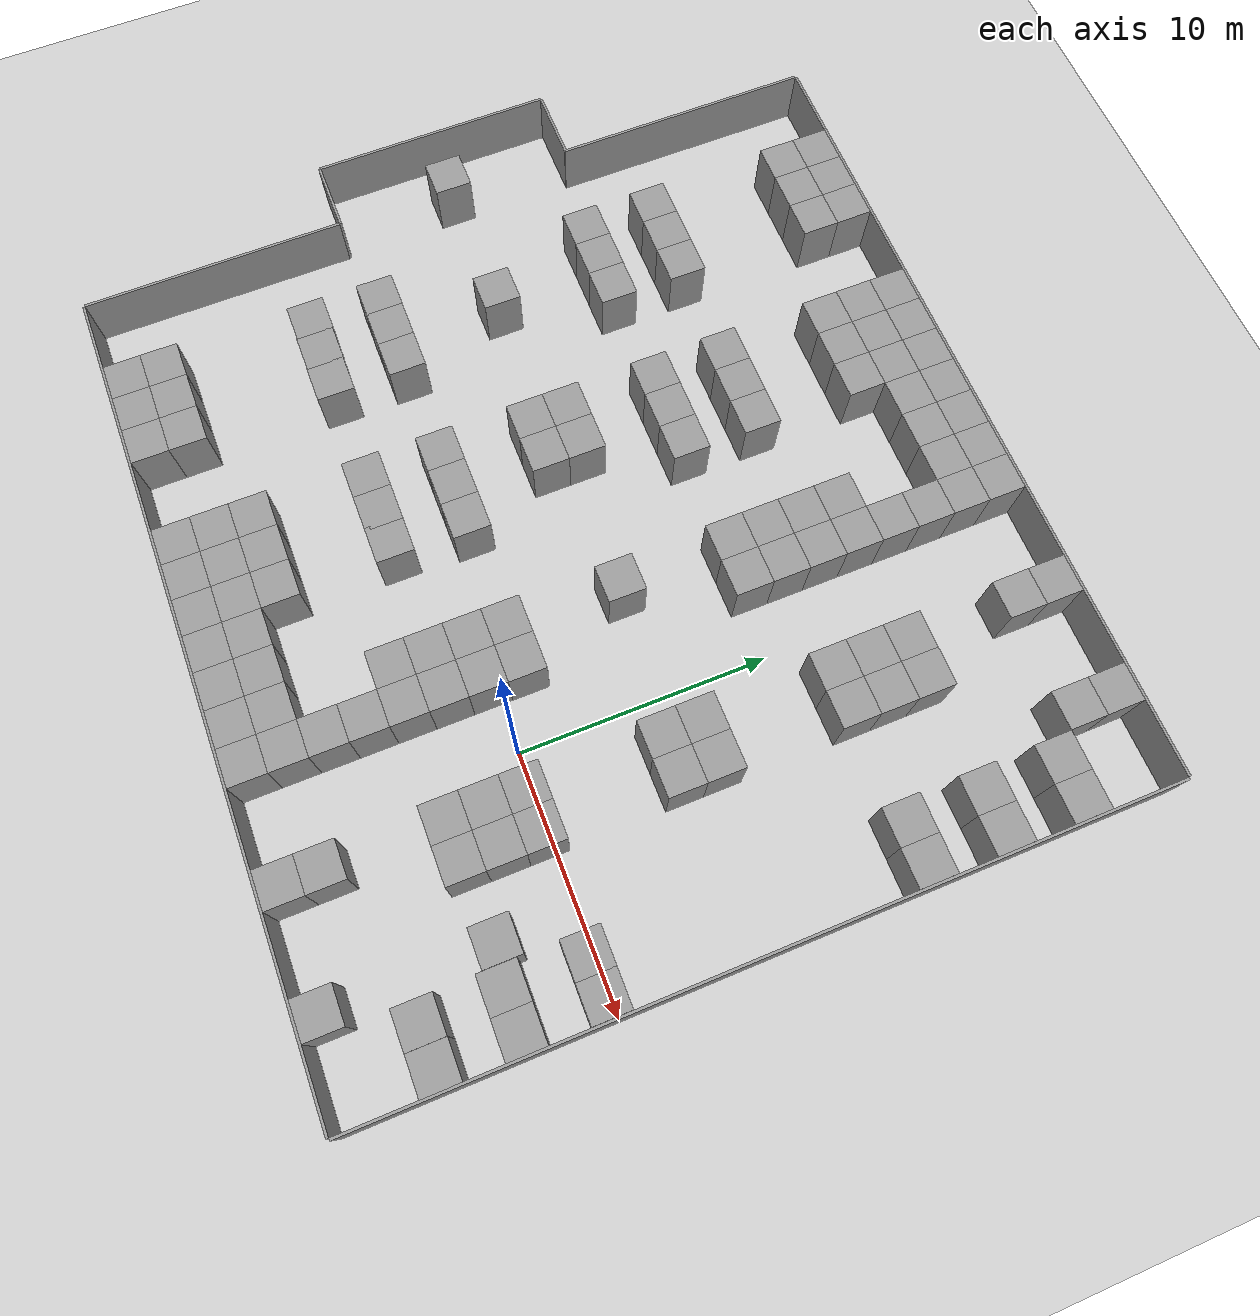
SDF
<sdf version="1.6">
 <world name="default">
  <light name="sun" type="directional">
   <pose>0 0 10 0 -0 0</pose>
   <diffuse>0.8 0.8 0.8 1</diffuse>
   <specular>0.1 0.1 0.1 1</specular>
   <attenuation>
    <range>1000</range>
    <constant>0.9</constant>
    <linear>0.01</linear>
    <quadratic>0.001</quadratic>
   </attenuation>
   <direction>-0.5 0.5 -1</direction>
  </light>
  <model name="ground_plane">
   <static>1</static>
   <link name="link">
    <collision name="collision">
     <geometry><plane><normal>0 0 1</normal><size>100 100</size></plane></geometry>
     <surface><friction><ode><mu>100</mu><mu2>50</mu2></ode></friction></surface>
    </collision>
    <visual name="visual">
     <cast_shadows>0</cast_shadows>
     <geometry><plane><normal>0 0 1</normal><size>100 100</size></plane></geometry>
     <material>
      <script><uri>file://media/materials/scripts/gazebo.material</uri><name>Gazebo/Grey</name></script>
     </material>
    </visual>
   </link>
  </model>
  <gravity>0 0 -9.8</gravity>
  <magnetic_field>6e-06 2.3e-05 -4.2e-05</magnetic_field>
  <atmosphere type="adiabatic"/>
  <physics name="default_physics" default="0" type="ode">
   <max_step_size>0.001</max_step_size>
   <real_time_factor>1</real_time_factor>
   <real_time_update_rate>1000</real_time_update_rate>
  </physics>
  <scene><ambient>0.4 0.4 0.4 1</ambient><background>0.7 0.7 0.7 1</background><shadows>1</shadows></scene>
  <spherical_coordinates>
   <surface_model>EARTH_WGS84</surface_model>
   <latitude_deg>0</latitude_deg>
   <longitude_deg>0</longitude_deg>
   <elevation>0</elevation>
   <heading_deg>0</heading_deg>
  </spherical_coordinates>
  <model name="wall_1.5_1.5">
   <link name="Wall_2">
    <inertial>
     <mass>10</mass>
     <inertia><ixx>1</ixx><ixy>0</ixy><ixz>0</ixz><iyy>1</iyy><iyz>0</iyz><izz>1</izz></inertia>
    </inertial>
    <visual name="Wall_2_Visual">
     <pose>0 0 1.25 0 -0 0</pose>
     <geometry><box><size>1.5 1.5 2.5</size></box></geometry>
     <material>
      <script><uri>file://media/materials/scripts/gazebo.material</uri><name>Gazebo/Grey</name></script>
      <ambient>1 1 1 1</ambient>
      <diffuse>0.7 0.7 0.7 1</diffuse>
      <specular>0.01 0.01 0.01 1</specular>
      <emissive>0 0 0 1</emissive>
      <shader type="vertex"><normal_map>__default__</normal_map></shader>
     </material>
    </visual>
    <collision name="Wall_2_Collision">
     <pose>0 0 1.25 0 -0 0</pose>
     <geometry><box><size>1.5 1.5 2.5</size></box></geometry>
     <surface>
      <friction>
       <ode><mu>1</mu><mu2>1</mu2><fdir1>0 0 0</fdir1><slip1>0</slip1><slip2>0</slip2></ode>
       <torsional>
        <coefficient>1</coefficient>
        <patch_radius>0</patch_radius>
        <surface_radius>0</surface_radius>
        <use_patch_radius>1</use_patch_radius>
        <ode><slip>0</slip></ode>
       </torsional>
      </friction>
      <bounce><restitution_coefficient>0</restitution_coefficient><threshold>1e+06</threshold></bounce>
      <contact>
       <collide_without_contact>0</collide_without_contact>
       <collide_without_contact_bitmask>1</collide_without_contact_bitmask>
       <collide_bitmask>1</collide_bitmask>
       <ode>
        <soft_cfm>0</soft_cfm>
        <soft_erp>0.2</soft_erp>
        <kp>1e+13</kp>
        <kd>1</kd>
        <max_vel>0.01</max_vel>
        <min_depth>0</min_depth>
       </ode>
       <bullet>
        <split_impulse>1</split_impulse>
        <split_impulse_penetration_threshold>-0.01</split_impulse_penetration_threshold>
        <soft_cfm>0</soft_cfm>
        <soft_erp>0.2</soft_erp>
        <kp>1e+13</kp>
        <kd>1</kd>
       </bullet>
      </contact>
     </surface>
    </collision>
   </link>
   <static>1</static>
   <pose>6.25 -9.25 0 0 -0 0</pose>
  </model>
  <model name="wall_1.5_1.5_2">
   <link name="Wall_2">
    <inertial>
     <mass>10</mass>
     <inertia><ixx>1</ixx><ixy>0</ixy><ixz>0</ixz><iyy>1</iyy><iyz>0</iyz><izz>1</izz></inertia>
    </inertial>
    <visual name="Wall_2_Visual">
     <pose>0 0 1.25 0 -0 0</pose>
     <geometry><box><size>1.5 1.5 2.5</size></box></geometry>
     <material>
      <script><uri>file://media/materials/scripts/gazebo.material</uri><name>Gazebo/Grey</name></script>
      <ambient>1 1 1 1</ambient>
      <diffuse>0.7 0.7 0.7 1</diffuse>
      <specular>0.01 0.01 0.01 1</specular>
      <emissive>0 0 0 1</emissive>
      <shader type="vertex"><normal_map>__default__</normal_map></shader>
     </material>
    </visual>
    <collision name="Wall_2_Collision">
     <pose>0 0 1.25 0 -0 0</pose>
     <geometry><box><size>1.5 1.5 2.5</size></box></geometry>
     <surface>
      <friction>
       <ode><mu>1</mu><mu2>1</mu2><fdir1>0 0 0</fdir1><slip1>0</slip1><slip2>0</slip2></ode>
       <torsional>
        <coefficient>1</coefficient>
        <patch_radius>0</patch_radius>
        <surface_radius>0</surface_radius>
        <use_patch_radius>1</use_patch_radius>
        <ode><slip>0</slip></ode>
       </torsional>
      </friction>
      <bounce><restitution_coefficient>0</restitution_coefficient><threshold>1e+06</threshold></bounce>
      <contact>
       <collide_without_contact>0</collide_without_contact>
       <collide_without_contact_bitmask>1</collide_without_contact_bitmask>
       <collide_bitmask>1</collide_bitmask>
       <ode>
        <soft_cfm>0</soft_cfm>
        <soft_erp>0.2</soft_erp>
        <kp>1e+13</kp>
        <kd>1</kd>
        <max_vel>0.01</max_vel>
        <min_depth>0</min_depth>
       </ode>
       <bullet>
        <split_impulse>1</split_impulse>
        <split_impulse_penetration_threshold>-0.01</split_impulse_penetration_threshold>
        <soft_cfm>0</soft_cfm>
        <soft_erp>0.2</soft_erp>
        <kp>1e+13</kp>
        <kd>1</kd>
       </bullet>
      </contact>
     </surface>
    </collision>
   </link>
   <static>1</static>
   <pose>6.25 -3 0 0 -0 0</pose>
  </model>
  <model name="wall_1.5_1.5_3">
   <link name="Wall_2">
    <inertial>
     <mass>10</mass>
     <inertia><ixx>1</ixx><ixy>0</ixy><ixz>0</ixz><iyy>1</iyy><iyz>0</iyz><izz>1</izz></inertia>
    </inertial>
    <visual name="Wall_2_Visual">
     <pose>0 0 1.25 0 -0 0</pose>
     <geometry><box><size>1.5 1.5 2.5</size></box></geometry>
     <material>
      <script><uri>file://media/materials/scripts/gazebo.material</uri><name>Gazebo/Grey</name></script>
      <ambient>1 1 1 1</ambient>
      <diffuse>0.7 0.7 0.7 1</diffuse>
      <specular>0.01 0.01 0.01 1</specular>
      <emissive>0 0 0 1</emissive>
      <shader type="vertex"><normal_map>__default__</normal_map></shader>
     </material>
    </visual>
    <collision name="Wall_2_Collision">
     <pose>0 0 1.25 0 -0 0</pose>
     <geometry><box><size>1.5 1.5 2.5</size></box></geometry>
     <surface>
      <friction>
       <ode><mu>1</mu><mu2>1</mu2><fdir1>0 0 0</fdir1><slip1>0</slip1><slip2>0</slip2></ode>
       <torsional>
        <coefficient>1</coefficient>
        <patch_radius>0</patch_radius>
        <surface_radius>0</surface_radius>
        <use_patch_radius>1</use_patch_radius>
        <ode><slip>0</slip></ode>
       </torsional>
      </friction>
      <bounce><restitution_coefficient>0</restitution_coefficient><threshold>1e+06</threshold></bounce>
      <contact>
       <collide_without_contact>0</collide_without_contact>
       <collide_without_contact_bitmask>1</collide_without_contact_bitmask>
       <collide_bitmask>1</collide_bitmask>
       <ode>
        <soft_cfm>0</soft_cfm>
        <soft_erp>0.2</soft_erp>
        <kp>1e+13</kp>
        <kd>1</kd>
        <max_vel>0.01</max_vel>
        <min_depth>0</min_depth>
       </ode>
       <bullet>
        <split_impulse>1</split_impulse>
        <split_impulse_penetration_threshold>-0.01</split_impulse_penetration_threshold>
        <soft_cfm>0</soft_cfm>
        <soft_erp>0.2</soft_erp>
        <kp>1e+13</kp>
        <kd>1</kd>
       </bullet>
      </contact>
     </surface>
    </collision>
   </link>
   <static>1</static>
   <pose>7.75334 -6.23301 0 0 -0 0</pose>
  </model>
  <model name="wall_1.5_1.5_8">
   <link name="Wall_2">
    <inertial>
     <mass>10</mass>
     <inertia><ixx>1</ixx><ixy>0</ixy><ixz>0</ixz><iyy>1</iyy><iyz>0</iyz><izz>1</izz></inertia>
    </inertial>
    <visual name="Wall_2_Visual">
     <pose>0 0 1.25 0 -0 0</pose>
     <geometry><box><size>1.5 1.5 2.5</size></box></geometry>
     <material>
      <script><uri>file://media/materials/scripts/gazebo.material</uri><name>Gazebo/Grey</name></script>
      <ambient>1 1 1 1</ambient>
      <diffuse>0.7 0.7 0.7 1</diffuse>
      <specular>0.01 0.01 0.01 1</specular>
      <emissive>0 0 0 1</emissive>
      <shader type="vertex"><normal_map>__default__</normal_map></shader>
     </material>
    </visual>
    <collision name="Wall_2_Collision">
     <pose>0 0 1.25 0 -0 0</pose>
     <geometry><box><size>1.5 1.5 2.5</size></box></geometry>
     <surface>
      <friction>
       <ode><mu>1</mu><mu2>1</mu2><fdir1>0 0 0</fdir1><slip1>0</slip1><slip2>0</slip2></ode>
       <torsional>
        <coefficient>1</coefficient>
        <patch_radius>0</patch_radius>
        <surface_radius>0</surface_radius>
        <use_patch_radius>1</use_patch_radius>
        <ode><slip>0</slip></ode>
       </torsional>
      </friction>
      <bounce><restitution_coefficient>0</restitution_coefficient><threshold>1e+06</threshold></bounce>
      <contact>
       <collide_without_contact>0</collide_without_contact>
       <collide_without_contact_bitmask>1</collide_without_contact_bitmask>
       <collide_bitmask>1</collide_bitmask>
       <ode>
        <soft_cfm>0</soft_cfm>
        <soft_erp>0.2</soft_erp>
        <kp>1e+13</kp>
        <kd>1</kd>
        <max_vel>0.01</max_vel>
        <min_depth>0</min_depth>
       </ode>
       <bullet>
        <split_impulse>1</split_impulse>
        <split_impulse_penetration_threshold>-0.01</split_impulse_penetration_threshold>
        <soft_cfm>0</soft_cfm>
        <soft_erp>0.2</soft_erp>
        <kp>1e+13</kp>
        <kd>1</kd>
       </bullet>
      </contact>
     </surface>
    </collision>
   </link>
   <static>1</static>
   <pose>9.25677 -6.22393 0 0 -0 0</pose>
  </model>
  <model name="wall_1.5_1.5_9">
   <link name="Wall_2">
    <inertial>
     <mass>10</mass>
     <inertia><ixx>1</ixx><ixy>0</ixy><ixz>0</ixz><iyy>1</iyy><iyz>0</iyz><izz>1</izz></inertia>
    </inertial>
    <visual name="Wall_2_Visual">
     <pose>0 0 1.25 0 -0 0</pose>
     <geometry><box><size>1.5 1.5 2.5</size></box></geometry>
     <material>
      <script><uri>file://media/materials/scripts/gazebo.material</uri><name>Gazebo/Grey</name></script>
      <ambient>1 1 1 1</ambient>
      <diffuse>0.7 0.7 0.7 1</diffuse>
      <specular>0.01 0.01 0.01 1</specular>
      <emissive>0 0 0 1</emissive>
      <shader type="vertex"><normal_map>__default__</normal_map></shader>
     </material>
    </visual>
    <collision name="Wall_2_Collision">
     <pose>0 0 1.25 0 -0 0</pose>
     <geometry><box><size>1.5 1.5 2.5</size></box></geometry>
     <surface>
      <friction>
       <ode><mu>1</mu><mu2>1</mu2><fdir1>0 0 0</fdir1><slip1>0</slip1><slip2>0</slip2></ode>
       <torsional>
        <coefficient>1</coefficient>
        <patch_radius>0</patch_radius>
        <surface_radius>0</surface_radius>
        <use_patch_radius>1</use_patch_radius>
        <ode><slip>0</slip></ode>
       </torsional>
      </friction>
      <bounce><restitution_coefficient>0</restitution_coefficient><threshold>1e+06</threshold></bounce>
      <contact>
       <collide_without_contact>0</collide_without_contact>
       <collide_without_contact_bitmask>1</collide_without_contact_bitmask>
       <collide_bitmask>1</collide_bitmask>
       <ode>
        <soft_cfm>0</soft_cfm>
        <soft_erp>0.2</soft_erp>
        <kp>1e+13</kp>
        <kd>1</kd>
        <max_vel>0.01</max_vel>
        <min_depth>0</min_depth>
       </ode>
       <bullet>
        <split_impulse>1</split_impulse>
        <split_impulse_penetration_threshold>-0.01</split_impulse_penetration_threshold>
        <soft_cfm>0</soft_cfm>
        <soft_erp>0.2</soft_erp>
        <kp>1e+13</kp>
        <kd>1</kd>
       </bullet>
      </contact>
     </surface>
    </collision>
   </link>
   <static>1</static>
   <pose>9.24884 -3.25545 0 0 -0 0</pose>
  </model>
  <model name="wall_1.5_1.5_10">
   <link name="Wall_2">
    <inertial>
     <mass>10</mass>
     <inertia><ixx>1</ixx><ixy>0</ixy><ixz>0</ixz><iyy>1</iyy><iyz>0</iyz><izz>1</izz></inertia>
    </inertial>
    <visual name="Wall_2_Visual">
     <pose>0 0 1.25 0 -0 0</pose>
     <geometry><box><size>1.5 1.5 2.5</size></box></geometry>
     <material>
      <script><uri>file://media/materials/scripts/gazebo.material</uri><name>Gazebo/Grey</name></script>
      <ambient>1 1 1 1</ambient>
      <diffuse>0.7 0.7 0.7 1</diffuse>
      <specular>0.01 0.01 0.01 1</specular>
      <emissive>0 0 0 1</emissive>
      <shader type="vertex"><normal_map>__default__</normal_map></shader>
     </material>
    </visual>
    <collision name="Wall_2_Collision">
     <pose>0 0 1.25 0 -0 0</pose>
     <geometry><box><size>1.5 1.5 2.5</size></box></geometry>
     <surface>
      <friction>
       <ode><mu>1</mu><mu2>1</mu2><fdir1>0 0 0</fdir1><slip1>0</slip1><slip2>0</slip2></ode>
       <torsional>
        <coefficient>1</coefficient>
        <patch_radius>0</patch_radius>
        <surface_radius>0</surface_radius>
        <use_patch_radius>1</use_patch_radius>
        <ode><slip>0</slip></ode>
       </torsional>
      </friction>
      <bounce><restitution_coefficient>0</restitution_coefficient><threshold>1e+06</threshold></bounce>
      <contact>
       <collide_without_contact>0</collide_without_contact>
       <collide_without_contact_bitmask>1</collide_without_contact_bitmask>
       <collide_bitmask>1</collide_bitmask>
       <ode>
        <soft_cfm>0</soft_cfm>
        <soft_erp>0.2</soft_erp>
        <kp>1e+13</kp>
        <kd>1</kd>
        <max_vel>0.01</max_vel>
        <min_depth>0</min_depth>
       </ode>
       <bullet>
        <split_impulse>1</split_impulse>
        <split_impulse_penetration_threshold>-0.01</split_impulse_penetration_threshold>
        <soft_cfm>0</soft_cfm>
        <soft_erp>0.2</soft_erp>
        <kp>1e+13</kp>
        <kd>1</kd>
       </bullet>
      </contact>
     </surface>
    </collision>
   </link>
   <static>1</static>
   <pose>7.76163 -3.25137 0 0 -0 0</pose>
  </model>
  <model name="wall_1.5_1.5_11">
   <link name="Wall_2">
    <inertial>
     <mass>10</mass>
     <inertia><ixx>1</ixx><ixy>0</ixy><ixz>0</ixz><iyy>1</iyy><iyz>0</iyz><izz>1</izz></inertia>
    </inertial>
    <visual name="Wall_2_Visual">
     <pose>0 0 1.25 0 -0 0</pose>
     <geometry><box><size>1.5 1.5 2.5</size></box></geometry>
     <material>
      <script><uri>file://media/materials/scripts/gazebo.material</uri><name>Gazebo/Grey</name></script>
      <ambient>1 1 1 1</ambient>
      <diffuse>0.7 0.7 0.7 1</diffuse>
      <specular>0.01 0.01 0.01 1</specular>
      <emissive>0 0 0 1</emissive>
      <shader type="vertex"><normal_map>__default__</normal_map></shader>
     </material>
    </visual>
    <collision name="Wall_2_Collision">
     <pose>0 0 1.25 0 -0 0</pose>
     <geometry><box><size>1.5 1.5 2.5</size></box></geometry>
     <surface>
      <friction>
       <ode><mu>1</mu><mu2>1</mu2><fdir1>0 0 0</fdir1><slip1>0</slip1><slip2>0</slip2></ode>
       <torsional>
        <coefficient>1</coefficient>
        <patch_radius>0</patch_radius>
        <surface_radius>0</surface_radius>
        <use_patch_radius>1</use_patch_radius>
        <ode><slip>0</slip></ode>
       </torsional>
      </friction>
      <bounce><restitution_coefficient>0</restitution_coefficient><threshold>1e+06</threshold></bounce>
      <contact>
       <collide_without_contact>0</collide_without_contact>
       <collide_without_contact_bitmask>1</collide_without_contact_bitmask>
       <collide_bitmask>1</collide_bitmask>
       <ode>
        <soft_cfm>0</soft_cfm>
        <soft_erp>0.2</soft_erp>
        <kp>1e+13</kp>
        <kd>1</kd>
        <max_vel>0.01</max_vel>
        <min_depth>0</min_depth>
       </ode>
       <bullet>
        <split_impulse>1</split_impulse>
        <split_impulse_penetration_threshold>-0.01</split_impulse_penetration_threshold>
        <soft_cfm>0</soft_cfm>
        <soft_erp>0.2</soft_erp>
        <kp>1e+13</kp>
        <kd>1</kd>
       </bullet>
      </contact>
     </surface>
    </collision>
   </link>
   <static>1</static>
   <pose>9.24277 -0.255252 0 0 -0 0</pose>
  </model>
  <model name="wall_1.5_1.5_12">
   <link name="Wall_2">
    <inertial>
     <mass>10</mass>
     <inertia><ixx>1</ixx><ixy>0</ixy><ixz>0</ixz><iyy>1</iyy><iyz>0</iyz><izz>1</izz></inertia>
    </inertial>
    <visual name="Wall_2_Visual">
     <pose>0 0 1.25 0 -0 0</pose>
     <geometry><box><size>1.5 1.5 2.5</size></box></geometry>
     <material>
      <script><uri>file://media/materials/scripts/gazebo.material</uri><name>Gazebo/Grey</name></script>
      <ambient>1 1 1 1</ambient>
      <diffuse>0.7 0.7 0.7 1</diffuse>
      <specular>0.01 0.01 0.01 1</specular>
      <emissive>0 0 0 1</emissive>
      <shader type="vertex"><normal_map>__default__</normal_map></shader>
     </material>
    </visual>
    <collision name="Wall_2_Collision">
     <pose>0 0 1.25 0 -0 0</pose>
     <geometry><box><size>1.5 1.5 2.5</size></box></geometry>
     <surface>
      <friction>
       <ode><mu>1</mu><mu2>1</mu2><fdir1>0 0 0</fdir1><slip1>0</slip1><slip2>0</slip2></ode>
       <torsional>
        <coefficient>1</coefficient>
        <patch_radius>0</patch_radius>
        <surface_radius>0</surface_radius>
        <use_patch_radius>1</use_patch_radius>
        <ode><slip>0</slip></ode>
       </torsional>
      </friction>
      <bounce><restitution_coefficient>0</restitution_coefficient><threshold>1e+06</threshold></bounce>
      <contact>
       <collide_without_contact>0</collide_without_contact>
       <collide_without_contact_bitmask>1</collide_without_contact_bitmask>
       <collide_bitmask>1</collide_bitmask>
       <ode>
        <soft_cfm>0</soft_cfm>
        <soft_erp>0.2</soft_erp>
        <kp>1e+13</kp>
        <kd>1</kd>
        <max_vel>0.01</max_vel>
        <min_depth>0</min_depth>
       </ode>
       <bullet>
        <split_impulse>1</split_impulse>
        <split_impulse_penetration_threshold>-0.01</split_impulse_penetration_threshold>
        <soft_cfm>0</soft_cfm>
        <soft_erp>0.2</soft_erp>
        <kp>1e+13</kp>
        <kd>1</kd>
       </bullet>
      </contact>
     </surface>
    </collision>
   </link>
   <static>1</static>
   <pose>7.75582 -0.251223 0 0 -0 0</pose>
  </model>
  <model name="wall_1.5_1.5_13">
   <link name="Wall_2">
    <inertial>
     <mass>10</mass>
     <inertia><ixx>1</ixx><ixy>0</ixy><ixz>0</ixz><iyy>1</iyy><iyz>0</iyz><izz>1</izz></inertia>
    </inertial>
    <visual name="Wall_2_Visual">
     <pose>0 0 1.25 0 -0 0</pose>
     <geometry><box><size>1.5 1.5 2.5</size></box></geometry>
     <material>
      <script><uri>file://media/materials/scripts/gazebo.material</uri><name>Gazebo/Grey</name></script>
      <ambient>1 1 1 1</ambient>
      <diffuse>0.7 0.7 0.7 1</diffuse>
      <specular>0.01 0.01 0.01 1</specular>
      <emissive>0 0 0 1</emissive>
      <shader type="vertex"><normal_map>__default__</normal_map></shader>
     </material>
    </visual>
    <collision name="Wall_2_Collision">
     <pose>0 0 1.25 0 -0 0</pose>
     <geometry><box><size>1.5 1.5 2.5</size></box></geometry>
     <surface>
      <friction>
       <ode><mu>1</mu><mu2>1</mu2><fdir1>0 0 0</fdir1><slip1>0</slip1><slip2>0</slip2></ode>
       <torsional>
        <coefficient>1</coefficient>
        <patch_radius>0</patch_radius>
        <surface_radius>0</surface_radius>
        <use_patch_radius>1</use_patch_radius>
        <ode><slip>0</slip></ode>
       </torsional>
      </friction>
      <bounce><restitution_coefficient>0</restitution_coefficient><threshold>1e+06</threshold></bounce>
      <contact>
       <collide_without_contact>0</collide_without_contact>
       <collide_without_contact_bitmask>1</collide_without_contact_bitmask>
       <collide_bitmask>1</collide_bitmask>
       <ode>
        <soft_cfm>0</soft_cfm>
        <soft_erp>0.2</soft_erp>
        <kp>1e+13</kp>
        <kd>1</kd>
        <max_vel>0.01</max_vel>
        <min_depth>0</min_depth>
       </ode>
       <bullet>
        <split_impulse>1</split_impulse>
        <split_impulse_penetration_threshold>-0.01</split_impulse_penetration_threshold>
        <soft_cfm>0</soft_cfm>
        <soft_erp>0.2</soft_erp>
        <kp>1e+13</kp>
        <kd>1</kd>
       </bullet>
      </contact>
     </surface>
    </collision>
   </link>
   <static>1</static>
   <pose>9.25 11.75 0 0 -0 0</pose>
  </model>
  <model name="wall_1.5_1.5_14">
   <link name="Wall_2">
    <inertial>
     <mass>10</mass>
     <inertia><ixx>1</ixx><ixy>0</ixy><ixz>0</ixz><iyy>1</iyy><iyz>0</iyz><izz>1</izz></inertia>
    </inertial>
    <visual name="Wall_2_Visual">
     <pose>0 0 1.25 0 -0 0</pose>
     <geometry><box><size>1.5 1.5 2.5</size></box></geometry>
     <material>
      <script><uri>file://media/materials/scripts/gazebo.material</uri><name>Gazebo/Grey</name></script>
      <ambient>1 1 1 1</ambient>
      <diffuse>0.7 0.7 0.7 1</diffuse>
      <specular>0.01 0.01 0.01 1</specular>
      <emissive>0 0 0 1</emissive>
      <shader type="vertex"><normal_map>__default__</normal_map></shader>
     </material>
    </visual>
    <collision name="Wall_2_Collision">
     <pose>0 0 1.25 0 -0 0</pose>
     <geometry><box><size>1.5 1.5 2.5</size></box></geometry>
     <surface>
      <friction>
       <ode><mu>1</mu><mu2>1</mu2><fdir1>0 0 0</fdir1><slip1>0</slip1><slip2>0</slip2></ode>
       <torsional>
        <coefficient>1</coefficient>
        <patch_radius>0</patch_radius>
        <surface_radius>0</surface_radius>
        <use_patch_radius>1</use_patch_radius>
        <ode><slip>0</slip></ode>
       </torsional>
      </friction>
      <bounce><restitution_coefficient>0</restitution_coefficient><threshold>1e+06</threshold></bounce>
      <contact>
       <collide_without_contact>0</collide_without_contact>
       <collide_without_contact_bitmask>1</collide_without_contact_bitmask>
       <collide_bitmask>1</collide_bitmask>
       <ode>
        <soft_cfm>0</soft_cfm>
        <soft_erp>0.2</soft_erp>
        <kp>1e+13</kp>
        <kd>1</kd>
        <max_vel>0.01</max_vel>
        <min_depth>0</min_depth>
       </ode>
       <bullet>
        <split_impulse>1</split_impulse>
        <split_impulse_penetration_threshold>-0.01</split_impulse_penetration_threshold>
        <soft_cfm>0</soft_cfm>
        <soft_erp>0.2</soft_erp>
        <kp>1e+13</kp>
        <kd>1</kd>
       </bullet>
      </contact>
     </surface>
    </collision>
   </link>
   <static>1</static>
   <pose>9.25 14.75 0 0 -0 0</pose>
  </model>
  <model name="wall_1.5_1.5_15">
   <link name="Wall_2">
    <inertial>
     <mass>10</mass>
     <inertia><ixx>1</ixx><ixy>0</ixy><ixz>0</ixz><iyy>1</iyy><iyz>0</iyz><izz>1</izz></inertia>
    </inertial>
    <visual name="Wall_2_Visual">
     <pose>0 0 1.25 0 -0 0</pose>
     <geometry><box><size>1.5 1.5 2.5</size></box></geometry>
     <material>
      <script><uri>file://media/materials/scripts/gazebo.material</uri><name>Gazebo/Grey</name></script>
      <ambient>1 1 1 1</ambient>
      <diffuse>0.7 0.7 0.7 1</diffuse>
      <specular>0.01 0.01 0.01 1</specular>
      <emissive>0 0 0 1</emissive>
      <shader type="vertex"><normal_map>__default__</normal_map></shader>
     </material>
    </visual>
    <collision name="Wall_2_Collision">
     <pose>0 0 1.25 0 -0 0</pose>
     <geometry><box><size>1.5 1.5 2.5</size></box></geometry>
     <surface>
      <friction>
       <ode><mu>1</mu><mu2>1</mu2><fdir1>0 0 0</fdir1><slip1>0</slip1><slip2>0</slip2></ode>
       <torsional>
        <coefficient>1</coefficient>
        <patch_radius>0</patch_radius>
        <surface_radius>0</surface_radius>
        <use_patch_radius>1</use_patch_radius>
        <ode><slip>0</slip></ode>
       </torsional>
      </friction>
      <bounce><restitution_coefficient>0</restitution_coefficient><threshold>1e+06</threshold></bounce>
      <contact>
       <collide_without_contact>0</collide_without_contact>
       <collide_without_contact_bitmask>1</collide_without_contact_bitmask>
       <collide_bitmask>1</collide_bitmask>
       <ode>
        <soft_cfm>0</soft_cfm>
        <soft_erp>0.2</soft_erp>
        <kp>1e+13</kp>
        <kd>1</kd>
        <max_vel>0.01</max_vel>
        <min_depth>0</min_depth>
       </ode>
       <bullet>
        <split_impulse>1</split_impulse>
        <split_impulse_penetration_threshold>-0.01</split_impulse_penetration_threshold>
        <soft_cfm>0</soft_cfm>
        <soft_erp>0.2</soft_erp>
        <kp>1e+13</kp>
        <kd>1</kd>
       </bullet>
      </contact>
     </surface>
    </collision>
   </link>
   <static>1</static>
   <pose>9.25 17.75 0 0 -0 0</pose>
  </model>
  <model name="wall_1.5_1.5_16">
   <link name="Wall_2">
    <inertial>
     <mass>10</mass>
     <inertia><ixx>1</ixx><ixy>0</ixy><ixz>0</ixz><iyy>1</iyy><iyz>0</iyz><izz>1</izz></inertia>
    </inertial>
    <visual name="Wall_2_Visual">
     <pose>0 0 1.25 0 -0 0</pose>
     <geometry><box><size>1.5 1.5 2.5</size></box></geometry>
     <material>
      <script><uri>file://media/materials/scripts/gazebo.material</uri><name>Gazebo/Grey</name></script>
      <ambient>1 1 1 1</ambient>
      <diffuse>0.7 0.7 0.7 1</diffuse>
      <specular>0.01 0.01 0.01 1</specular>
      <emissive>0 0 0 1</emissive>
      <shader type="vertex"><normal_map>__default__</normal_map></shader>
     </material>
    </visual>
    <collision name="Wall_2_Collision">
     <pose>0 0 1.25 0 -0 0</pose>
     <geometry><box><size>1.5 1.5 2.5</size></box></geometry>
     <surface>
      <friction>
       <ode><mu>1</mu><mu2>1</mu2><fdir1>0 0 0</fdir1><slip1>0</slip1><slip2>0</slip2></ode>
       <torsional>
        <coefficient>1</coefficient>
        <patch_radius>0</patch_radius>
        <surface_radius>0</surface_radius>
        <use_patch_radius>1</use_patch_radius>
        <ode><slip>0</slip></ode>
       </torsional>
      </friction>
      <bounce><restitution_coefficient>0</restitution_coefficient><threshold>1e+06</threshold></bounce>
      <contact>
       <collide_without_contact>0</collide_without_contact>
       <collide_without_contact_bitmask>1</collide_without_contact_bitmask>
       <collide_bitmask>1</collide_bitmask>
       <ode>
        <soft_cfm>0</soft_cfm>
        <soft_erp>0.2</soft_erp>
        <kp>1e+13</kp>
        <kd>1</kd>
        <max_vel>0.01</max_vel>
        <min_depth>0</min_depth>
       </ode>
       <bullet>
        <split_impulse>1</split_impulse>
        <split_impulse_penetration_threshold>-0.01</split_impulse_penetration_threshold>
        <soft_cfm>0</soft_cfm>
        <soft_erp>0.2</soft_erp>
        <kp>1e+13</kp>
        <kd>1</kd>
       </bullet>
      </contact>
     </surface>
    </collision>
   </link>
   <static>1</static>
   <pose>7.75 11.75 0 0 -0 0</pose>
  </model>
  <model name="wall_1.5_1.5_17">
   <link name="Wall_2">
    <inertial>
     <mass>10</mass>
     <inertia><ixx>1</ixx><ixy>0</ixy><ixz>0</ixz><iyy>1</iyy><iyz>0</iyz><izz>1</izz></inertia>
    </inertial>
    <visual name="Wall_2_Visual">
     <pose>0 0 1.25 0 -0 0</pose>
     <geometry><box><size>1.5 1.5 2.5</size></box></geometry>
     <material>
      <script><uri>file://media/materials/scripts/gazebo.material</uri><name>Gazebo/Grey</name></script>
      <ambient>1 1 1 1</ambient>
      <diffuse>0.7 0.7 0.7 1</diffuse>
      <specular>0.01 0.01 0.01 1</specular>
      <emissive>0 0 0 1</emissive>
      <shader type="vertex"><normal_map>__default__</normal_map></shader>
     </material>
    </visual>
    <collision name="Wall_2_Collision">
     <pose>0 0 1.25 0 -0 0</pose>
     <geometry><box><size>1.5 1.5 2.5</size></box></geometry>
     <surface>
      <friction>
       <ode><mu>1</mu><mu2>1</mu2><fdir1>0 0 0</fdir1><slip1>0</slip1><slip2>0</slip2></ode>
       <torsional>
        <coefficient>1</coefficient>
        <patch_radius>0</patch_radius>
        <surface_radius>0</surface_radius>
        <use_patch_radius>1</use_patch_radius>
        <ode><slip>0</slip></ode>
       </torsional>
      </friction>
      <bounce><restitution_coefficient>0</restitution_coefficient><threshold>1e+06</threshold></bounce>
      <contact>
       <collide_without_contact>0</collide_without_contact>
       <collide_without_contact_bitmask>1</collide_without_contact_bitmask>
       <collide_bitmask>1</collide_bitmask>
       <ode>
        <soft_cfm>0</soft_cfm>
        <soft_erp>0.2</soft_erp>
        <kp>1e+13</kp>
        <kd>1</kd>
        <max_vel>0.01</max_vel>
        <min_depth>0</min_depth>
       </ode>
       <bullet>
        <split_impulse>1</split_impulse>
        <split_impulse_penetration_threshold>-0.01</split_impulse_penetration_threshold>
        <soft_cfm>0</soft_cfm>
        <soft_erp>0.2</soft_erp>
        <kp>1e+13</kp>
        <kd>1</kd>
       </bullet>
      </contact>
     </surface>
    </collision>
   </link>
   <static>1</static>
   <pose>7.75 14.75 0 0 -0 0</pose>
  </model>
  <model name="wall_1.5_1.5_18">
   <link name="Wall_2">
    <inertial>
     <mass>10</mass>
     <inertia><ixx>1</ixx><ixy>0</ixy><ixz>0</ixz><iyy>1</iyy><iyz>0</iyz><izz>1</izz></inertia>
    </inertial>
    <visual name="Wall_2_Visual">
     <pose>0 0 1.25 0 -0 0</pose>
     <geometry><box><size>1.5 1.5 2.5</size></box></geometry>
     <material>
      <script><uri>file://media/materials/scripts/gazebo.material</uri><name>Gazebo/Grey</name></script>
      <ambient>1 1 1 1</ambient>
      <diffuse>0.7 0.7 0.7 1</diffuse>
      <specular>0.01 0.01 0.01 1</specular>
      <emissive>0 0 0 1</emissive>
      <shader type="vertex"><normal_map>__default__</normal_map></shader>
     </material>
    </visual>
    <collision name="Wall_2_Collision">
     <pose>0 0 1.25 0 -0 0</pose>
     <geometry><box><size>1.5 1.5 2.5</size></box></geometry>
     <surface>
      <friction>
       <ode><mu>1</mu><mu2>1</mu2><fdir1>0 0 0</fdir1><slip1>0</slip1><slip2>0</slip2></ode>
       <torsional>
        <coefficient>1</coefficient>
        <patch_radius>0</patch_radius>
        <surface_radius>0</surface_radius>
        <use_patch_radius>1</use_patch_radius>
        <ode><slip>0</slip></ode>
       </torsional>
      </friction>
      <bounce><restitution_coefficient>0</restitution_coefficient><threshold>1e+06</threshold></bounce>
      <contact>
       <collide_without_contact>0</collide_without_contact>
       <collide_without_contact_bitmask>1</collide_without_contact_bitmask>
       <collide_bitmask>1</collide_bitmask>
       <ode>
        <soft_cfm>0</soft_cfm>
        <soft_erp>0.2</soft_erp>
        <kp>1e+13</kp>
        <kd>1</kd>
        <max_vel>0.01</max_vel>
        <min_depth>0</min_depth>
       </ode>
       <bullet>
        <split_impulse>1</split_impulse>
        <split_impulse_penetration_threshold>-0.01</split_impulse_penetration_threshold>
        <soft_cfm>0</soft_cfm>
        <soft_erp>0.2</soft_erp>
        <kp>1e+13</kp>
        <kd>1</kd>
       </bullet>
      </contact>
     </surface>
    </collision>
   </link>
   <static>1</static>
   <pose>7.75 17.75 0 0 -0 0</pose>
  </model>
  <model name="wall_1.5_1.5_19">
   <link name="Wall_2">
    <inertial>
     <mass>10</mass>
     <inertia><ixx>1</ixx><ixy>0</ixy><ixz>0</ixz><iyy>1</iyy><iyz>0</iyz><izz>1</izz></inertia>
    </inertial>
    <visual name="Wall_2_Visual">
     <pose>0 0 1.25 0 -0 0</pose>
     <geometry><box><size>1.5 1.5 2.5</size></box></geometry>
     <material>
      <script><uri>file://media/materials/scripts/gazebo.material</uri><name>Gazebo/Grey</name></script>
      <ambient>1 1 1 1</ambient>
      <diffuse>0.7 0.7 0.7 1</diffuse>
      <specular>0.01 0.01 0.01 1</specular>
      <emissive>0 0 0 1</emissive>
      <shader type="vertex"><normal_map>__default__</normal_map></shader>
     </material>
    </visual>
    <collision name="Wall_2_Collision">
     <pose>0 0 1.25 0 -0 0</pose>
     <geometry><box><size>1.5 1.5 2.5</size></box></geometry>
     <surface>
      <friction>
       <ode><mu>1</mu><mu2>1</mu2><fdir1>0 0 0</fdir1><slip1>0</slip1><slip2>0</slip2></ode>
       <torsional>
        <coefficient>1</coefficient>
        <patch_radius>0</patch_radius>
        <surface_radius>0</surface_radius>
        <use_patch_radius>1</use_patch_radius>
        <ode><slip>0</slip></ode>
       </torsional>
      </friction>
      <bounce><restitution_coefficient>0</restitution_coefficient><threshold>1e+06</threshold></bounce>
      <contact>
       <collide_without_contact>0</collide_without_contact>
       <collide_without_contact_bitmask>1</collide_without_contact_bitmask>
       <collide_bitmask>1</collide_bitmask>
       <ode>
        <soft_cfm>0</soft_cfm>
        <soft_erp>0.2</soft_erp>
        <kp>1e+13</kp>
        <kd>1</kd>
        <max_vel>0.01</max_vel>
        <min_depth>0</min_depth>
       </ode>
       <bullet>
        <split_impulse>1</split_impulse>
        <split_impulse_penetration_threshold>-0.01</split_impulse_penetration_threshold>
        <soft_cfm>0</soft_cfm>
        <soft_erp>0.2</soft_erp>
        <kp>1e+13</kp>
        <kd>1</kd>
       </bullet>
      </contact>
     </surface>
    </collision>
   </link>
   <static>1</static>
   <pose>6.25 20.75 0 0 -0 0</pose>
  </model>
  <model name="wall_1.5_1.5_20">
   <link name="Wall_2">
    <inertial>
     <mass>10</mass>
     <inertia><ixx>1</ixx><ixy>0</ixy><ixz>0</ixz><iyy>1</iyy><iyz>0</iyz><izz>1</izz></inertia>
    </inertial>
    <visual name="Wall_2_Visual">
     <pose>0 0 1.25 0 -0 0</pose>
     <geometry><box><size>1.5 1.5 2.5</size></box></geometry>
     <material>
      <script><uri>file://media/materials/scripts/gazebo.material</uri><name>Gazebo/Grey</name></script>
      <ambient>1 1 1 1</ambient>
      <diffuse>0.7 0.7 0.7 1</diffuse>
      <specular>0.01 0.01 0.01 1</specular>
      <emissive>0 0 0 1</emissive>
      <shader type="vertex"><normal_map>__default__</normal_map></shader>
     </material>
    </visual>
    <collision name="Wall_2_Collision">
     <pose>0 0 1.25 0 -0 0</pose>
     <geometry><box><size>1.5 1.5 2.5</size></box></geometry>
     <surface>
      <friction>
       <ode><mu>1</mu><mu2>1</mu2><fdir1>0 0 0</fdir1><slip1>0</slip1><slip2>0</slip2></ode>
       <torsional>
        <coefficient>1</coefficient>
        <patch_radius>0</patch_radius>
        <surface_radius>0</surface_radius>
        <use_patch_radius>1</use_patch_radius>
        <ode><slip>0</slip></ode>
       </torsional>
      </friction>
      <bounce><restitution_coefficient>0</restitution_coefficient><threshold>1e+06</threshold></bounce>
      <contact>
       <collide_without_contact>0</collide_without_contact>
       <collide_without_contact_bitmask>1</collide_without_contact_bitmask>
       <collide_bitmask>1</collide_bitmask>
       <ode>
        <soft_cfm>0</soft_cfm>
        <soft_erp>0.2</soft_erp>
        <kp>1e+13</kp>
        <kd>1</kd>
        <max_vel>0.01</max_vel>
        <min_depth>0</min_depth>
       </ode>
       <bullet>
        <split_impulse>1</split_impulse>
        <split_impulse_penetration_threshold>-0.01</split_impulse_penetration_threshold>
        <soft_cfm>0</soft_cfm>
        <soft_erp>0.2</soft_erp>
        <kp>1e+13</kp>
        <kd>1</kd>
       </bullet>
      </contact>
     </surface>
    </collision>
   </link>
   <static>1</static>
   <pose>1.75 20.75 0 0 -0 0</pose>
  </model>
  <model name="wall_1.5_1.5_21">
   <link name="Wall_2">
    <inertial>
     <mass>10</mass>
     <inertia><ixx>1</ixx><ixy>0</ixy><ixz>0</ixz><iyy>1</iyy><iyz>0</iyz><izz>1</izz></inertia>
    </inertial>
    <visual name="Wall_2_Visual">
     <pose>0 0 1.25 0 -0 0</pose>
     <geometry><box><size>1.5 1.5 2.5</size></box></geometry>
     <material>
      <script><uri>file://media/materials/scripts/gazebo.material</uri><name>Gazebo/Grey</name></script>
      <ambient>1 1 1 1</ambient>
      <diffuse>0.7 0.7 0.7 1</diffuse>
      <specular>0.01 0.01 0.01 1</specular>
      <emissive>0 0 0 1</emissive>
      <shader type="vertex"><normal_map>__default__</normal_map></shader>
     </material>
    </visual>
    <collision name="Wall_2_Collision">
     <pose>0 0 1.25 0 -0 0</pose>
     <geometry><box><size>1.5 1.5 2.5</size></box></geometry>
     <surface>
      <friction>
       <ode><mu>1</mu><mu2>1</mu2><fdir1>0 0 0</fdir1><slip1>0</slip1><slip2>0</slip2></ode>
       <torsional>
        <coefficient>1</coefficient>
        <patch_radius>0</patch_radius>
        <surface_radius>0</surface_radius>
        <use_patch_radius>1</use_patch_radius>
        <ode><slip>0</slip></ode>
       </torsional>
      </friction>
      <bounce><restitution_coefficient>0</restitution_coefficient><threshold>1e+06</threshold></bounce>
      <contact>
       <collide_without_contact>0</collide_without_contact>
       <collide_without_contact_bitmask>1</collide_without_contact_bitmask>
       <collide_bitmask>1</collide_bitmask>
       <ode>
        <soft_cfm>0</soft_cfm>
        <soft_erp>0.2</soft_erp>
        <kp>1e+13</kp>
        <kd>1</kd>
        <max_vel>0.01</max_vel>
        <min_depth>0</min_depth>
       </ode>
       <bullet>
        <split_impulse>1</split_impulse>
        <split_impulse_penetration_threshold>-0.01</split_impulse_penetration_threshold>
        <soft_cfm>0</soft_cfm>
        <soft_erp>0.2</soft_erp>
        <kp>1e+13</kp>
        <kd>1</kd>
       </bullet>
      </contact>
     </surface>
    </collision>
   </link>
   <static>1</static>
   <pose>1.75 -9.25 0 0 -0 0</pose>
  </model>
  <model name="wall_1.5_1.5_22">
   <link name="Wall_2">
    <inertial>
     <mass>10</mass>
     <inertia><ixx>1</ixx><ixy>0</ixy><ixz>0</ixz><iyy>1</iyy><iyz>0</iyz><izz>1</izz></inertia>
    </inertial>
    <visual name="Wall_2_Visual">
     <pose>0 0 1.25 0 -0 0</pose>
     <geometry><box><size>1.5 1.5 2.5</size></box></geometry>
     <material>
      <script><uri>file://media/materials/scripts/gazebo.material</uri><name>Gazebo/Grey</name></script>
      <ambient>1 1 1 1</ambient>
      <diffuse>0.7 0.7 0.7 1</diffuse>
      <specular>0.01 0.01 0.01 1</specular>
      <emissive>0 0 0 1</emissive>
      <shader type="vertex"><normal_map>__default__</normal_map></shader>
     </material>
    </visual>
    <collision name="Wall_2_Collision">
     <pose>0 0 1.25 0 -0 0</pose>
     <geometry><box><size>1.5 1.5 2.5</size></box></geometry>
     <surface>
      <friction>
       <ode><mu>1</mu><mu2>1</mu2><fdir1>0 0 0</fdir1><slip1>0</slip1><slip2>0</slip2></ode>
       <torsional>
        <coefficient>1</coefficient>
        <patch_radius>0</patch_radius>
        <surface_radius>0</surface_radius>
        <use_patch_radius>1</use_patch_radius>
        <ode><slip>0</slip></ode>
       </torsional>
      </friction>
      <bounce><restitution_coefficient>0</restitution_coefficient><threshold>1e+06</threshold></bounce>
      <contact>
       <collide_without_contact>0</collide_without_contact>
       <collide_without_contact_bitmask>1</collide_without_contact_bitmask>
       <collide_bitmask>1</collide_bitmask>
       <ode>
        <soft_cfm>0</soft_cfm>
        <soft_erp>0.2</soft_erp>
        <kp>1e+13</kp>
        <kd>1</kd>
        <max_vel>0.01</max_vel>
        <min_depth>0</min_depth>
       </ode>
       <bullet>
        <split_impulse>1</split_impulse>
        <split_impulse_penetration_threshold>-0.01</split_impulse_penetration_threshold>
        <soft_cfm>0</soft_cfm>
        <soft_erp>0.2</soft_erp>
        <kp>1e+13</kp>
        <kd>1</kd>
       </bullet>
      </contact>
     </surface>
    </collision>
   </link>
   <static>1</static>
   <pose>3.25 -3.25 0 0 -0 0</pose>
  </model>
  <model name="wall_1.5_1.5_23">
   <link name="Wall_2">
    <inertial>
     <mass>10</mass>
     <inertia><ixx>1</ixx><ixy>0</ixy><ixz>0</ixz><iyy>1</iyy><iyz>0</iyz><izz>1</izz></inertia>
    </inertial>
    <visual name="Wall_2_Visual">
     <pose>0 0 1.25 0 -0 0</pose>
     <geometry><box><size>1.5 1.5 2.5</size></box></geometry>
     <material>
      <script><uri>file://media/materials/scripts/gazebo.material</uri><name>Gazebo/Grey</name></script>
      <ambient>1 1 1 1</ambient>
      <diffuse>0.7 0.7 0.7 1</diffuse>
      <specular>0.01 0.01 0.01 1</specular>
      <emissive>0 0 0 1</emissive>
      <shader type="vertex"><normal_map>__default__</normal_map></shader>
     </material>
    </visual>
    <collision name="Wall_2_Collision">
     <pose>0 0 1.25 0 -0 0</pose>
     <geometry><box><size>1.5 1.5 2.5</size></box></geometry>
     <surface>
      <friction>
       <ode><mu>1</mu><mu2>1</mu2><fdir1>0 0 0</fdir1><slip1>0</slip1><slip2>0</slip2></ode>
       <torsional>
        <coefficient>1</coefficient>
        <patch_radius>0</patch_radius>
        <surface_radius>0</surface_radius>
        <use_patch_radius>1</use_patch_radius>
        <ode><slip>0</slip></ode>
       </torsional>
      </friction>
      <bounce><restitution_coefficient>0</restitution_coefficient><threshold>1e+06</threshold></bounce>
      <contact>
       <collide_without_contact>0</collide_without_contact>
       <collide_without_contact_bitmask>1</collide_without_contact_bitmask>
       <collide_bitmask>1</collide_bitmask>
       <ode>
        <soft_cfm>0</soft_cfm>
        <soft_erp>0.2</soft_erp>
        <kp>1e+13</kp>
        <kd>1</kd>
        <max_vel>0.01</max_vel>
        <min_depth>0</min_depth>
       </ode>
       <bullet>
        <split_impulse>1</split_impulse>
        <split_impulse_penetration_threshold>-0.01</split_impulse_penetration_threshold>
        <soft_cfm>0</soft_cfm>
        <soft_erp>0.2</soft_erp>
        <kp>1e+13</kp>
        <kd>1</kd>
       </bullet>
      </contact>
     </surface>
    </collision>
   </link>
   <static>1</static>
   <pose>3.25 5 0 0 -0 0</pose>
  </model>
  <model name="wall_1.5_1.5_24">
   <link name="Wall_2">
    <inertial>
     <mass>10</mass>
     <inertia><ixx>1</ixx><ixy>0</ixy><ixz>0</ixz><iyy>1</iyy><iyz>0</iyz><izz>1</izz></inertia>
    </inertial>
    <visual name="Wall_2_Visual">
     <pose>0 0 1.25 0 -0 0</pose>
     <geometry><box><size>1.5 1.5 2.5</size></box></geometry>
     <material>
      <script><uri>file://media/materials/scripts/gazebo.material</uri><name>Gazebo/Grey</name></script>
      <ambient>1 1 1 1</ambient>
      <diffuse>0.7 0.7 0.7 1</diffuse>
      <specular>0.01 0.01 0.01 1</specular>
      <emissive>0 0 0 1</emissive>
      <shader type="vertex"><normal_map>__default__</normal_map></shader>
     </material>
    </visual>
    <collision name="Wall_2_Collision">
     <pose>0 0 1.25 0 -0 0</pose>
     <geometry><box><size>1.5 1.5 2.5</size></box></geometry>
     <surface>
      <friction>
       <ode><mu>1</mu><mu2>1</mu2><fdir1>0 0 0</fdir1><slip1>0</slip1><slip2>0</slip2></ode>
       <torsional>
        <coefficient>1</coefficient>
        <patch_radius>0</patch_radius>
        <surface_radius>0</surface_radius>
        <use_patch_radius>1</use_patch_radius>
        <ode><slip>0</slip></ode>
       </torsional>
      </friction>
      <bounce><restitution_coefficient>0</restitution_coefficient><threshold>1e+06</threshold></bounce>
      <contact>
       <collide_without_contact>0</collide_without_contact>
       <collide_without_contact_bitmask>1</collide_without_contact_bitmask>
       <collide_bitmask>1</collide_bitmask>
       <ode>
        <soft_cfm>0</soft_cfm>
        <soft_erp>0.2</soft_erp>
        <kp>1e+13</kp>
        <kd>1</kd>
        <max_vel>0.01</max_vel>
        <min_depth>0</min_depth>
       </ode>
       <bullet>
        <split_impulse>1</split_impulse>
        <split_impulse_penetration_threshold>-0.01</split_impulse_penetration_threshold>
        <soft_cfm>0</soft_cfm>
        <soft_erp>0.2</soft_erp>
        <kp>1e+13</kp>
        <kd>1</kd>
       </bullet>
      </contact>
     </surface>
    </collision>
   </link>
   <static>1</static>
   <pose>3.25 11.75 0 0 -0 0</pose>
  </model>
  <model name="wall_1.5_1.5_25">
   <link name="Wall_2">
    <inertial>
     <mass>10</mass>
     <inertia><ixx>1</ixx><ixy>0</ixy><ixz>0</ixz><iyy>1</iyy><iyz>0</iyz><izz>1</izz></inertia>
    </inertial>
    <visual name="Wall_2_Visual">
     <pose>0 0 1.25 0 -0 0</pose>
     <geometry><box><size>1.5 1.5 2.5</size></box></geometry>
     <material>
      <script><uri>file://media/materials/scripts/gazebo.material</uri><name>Gazebo/Grey</name></script>
      <ambient>1 1 1 1</ambient>
      <diffuse>0.7 0.7 0.7 1</diffuse>
      <specular>0.01 0.01 0.01 1</specular>
      <emissive>0 0 0 1</emissive>
      <shader type="vertex"><normal_map>__default__</normal_map></shader>
     </material>
    </visual>
    <collision name="Wall_2_Collision">
     <pose>0 0 1.25 0 -0 0</pose>
     <geometry><box><size>1.5 1.5 2.5</size></box></geometry>
     <surface>
      <friction>
       <ode><mu>1</mu><mu2>1</mu2><fdir1>0 0 0</fdir1><slip1>0</slip1><slip2>0</slip2></ode>
       <torsional>
        <coefficient>1</coefficient>
        <patch_radius>0</patch_radius>
        <surface_radius>0</surface_radius>
        <use_patch_radius>1</use_patch_radius>
        <ode><slip>0</slip></ode>
       </torsional>
      </friction>
      <bounce><restitution_coefficient>0</restitution_coefficient><threshold>1e+06</threshold></bounce>
      <contact>
       <collide_without_contact>0</collide_without_contact>
       <collide_without_contact_bitmask>1</collide_without_contact_bitmask>
       <collide_bitmask>1</collide_bitmask>
       <ode>
        <soft_cfm>0</soft_cfm>
        <soft_erp>0.2</soft_erp>
        <kp>1e+13</kp>
        <kd>1</kd>
        <max_vel>0.01</max_vel>
        <min_depth>0</min_depth>
       </ode>
       <bullet>
        <split_impulse>1</split_impulse>
        <split_impulse_penetration_threshold>-0.01</split_impulse_penetration_threshold>
        <soft_cfm>0</soft_cfm>
        <soft_erp>0.2</soft_erp>
        <kp>1e+13</kp>
        <kd>1</kd>
       </bullet>
      </contact>
     </surface>
    </collision>
   </link>
   <static>1</static>
   <pose>1.75 -7.75 0 0 -0 0</pose>
  </model>
  <model name="wall_1.5_1.5_26">
   <link name="Wall_2">
    <inertial>
     <mass>10</mass>
     <inertia><ixx>1</ixx><ixy>0</ixy><ixz>0</ixz><iyy>1</iyy><iyz>0</iyz><izz>1</izz></inertia>
    </inertial>
    <visual name="Wall_2_Visual">
     <pose>0 0 1.25 0 -0 0</pose>
     <geometry><box><size>1.5 1.5 2.5</size></box></geometry>
     <material>
      <script><uri>file://media/materials/scripts/gazebo.material</uri><name>Gazebo/Grey</name></script>
      <ambient>1 1 1 1</ambient>
      <diffuse>0.7 0.7 0.7 1</diffuse>
      <specular>0.01 0.01 0.01 1</specular>
      <emissive>0 0 0 1</emissive>
      <shader type="vertex"><normal_map>__default__</normal_map></shader>
     </material>
    </visual>
    <collision name="Wall_2_Collision">
     <pose>0 0 1.25 0 -0 0</pose>
     <geometry><box><size>1.5 1.5 2.5</size></box></geometry>
     <surface>
      <friction>
       <ode><mu>1</mu><mu2>1</mu2><fdir1>0 0 0</fdir1><slip1>0</slip1><slip2>0</slip2></ode>
       <torsional>
        <coefficient>1</coefficient>
        <patch_radius>0</patch_radius>
        <surface_radius>0</surface_radius>
        <use_patch_radius>1</use_patch_radius>
        <ode><slip>0</slip></ode>
       </torsional>
      </friction>
      <bounce><restitution_coefficient>0</restitution_coefficient><threshold>1e+06</threshold></bounce>
      <contact>
       <collide_without_contact>0</collide_without_contact>
       <collide_without_contact_bitmask>1</collide_without_contact_bitmask>
       <collide_bitmask>1</collide_bitmask>
       <ode>
        <soft_cfm>0</soft_cfm>
        <soft_erp>0.2</soft_erp>
        <kp>1e+13</kp>
        <kd>1</kd>
        <max_vel>0.01</max_vel>
        <min_depth>0</min_depth>
       </ode>
       <bullet>
        <split_impulse>1</split_impulse>
        <split_impulse_penetration_threshold>-0.01</split_impulse_penetration_threshold>
        <soft_cfm>0</soft_cfm>
        <soft_erp>0.2</soft_erp>
        <kp>1e+13</kp>
        <kd>1</kd>
       </bullet>
      </contact>
     </surface>
    </collision>
   </link>
   <static>1</static>
   <pose>3.25 -1.75 0 0 -0 0</pose>
  </model>
  <model name="wall_1.5_1.5_27">
   <link name="Wall_2">
    <inertial>
     <mass>10</mass>
     <inertia><ixx>1</ixx><ixy>0</ixy><ixz>0</ixz><iyy>1</iyy><iyz>0</iyz><izz>1</izz></inertia>
    </inertial>
    <visual name="Wall_2_Visual">
     <pose>0 0 1.25 0 -0 0</pose>
     <geometry><box><size>1.5 1.5 2.5</size></box></geometry>
     <material>
      <script><uri>file://media/materials/scripts/gazebo.material</uri><name>Gazebo/Grey</name></script>
      <ambient>1 1 1 1</ambient>
      <diffuse>0.7 0.7 0.7 1</diffuse>
      <specular>0.01 0.01 0.01 1</specular>
      <emissive>0 0 0 1</emissive>
      <shader type="vertex"><normal_map>__default__</normal_map></shader>
     </material>
    </visual>
    <collision name="Wall_2_Collision">
     <pose>0 0 1.25 0 -0 0</pose>
     <geometry><box><size>1.5 1.5 2.5</size></box></geometry>
     <surface>
      <friction>
       <ode><mu>1</mu><mu2>1</mu2><fdir1>0 0 0</fdir1><slip1>0</slip1><slip2>0</slip2></ode>
       <torsional>
        <coefficient>1</coefficient>
        <patch_radius>0</patch_radius>
        <surface_radius>0</surface_radius>
        <use_patch_radius>1</use_patch_radius>
        <ode><slip>0</slip></ode>
       </torsional>
      </friction>
      <bounce><restitution_coefficient>0</restitution_coefficient><threshold>1e+06</threshold></bounce>
      <contact>
       <collide_without_contact>0</collide_without_contact>
       <collide_without_contact_bitmask>1</collide_without_contact_bitmask>
       <collide_bitmask>1</collide_bitmask>
       <ode>
        <soft_cfm>0</soft_cfm>
        <soft_erp>0.2</soft_erp>
        <kp>1e+13</kp>
        <kd>1</kd>
        <max_vel>0.01</max_vel>
        <min_depth>0</min_depth>
       </ode>
       <bullet>
        <split_impulse>1</split_impulse>
        <split_impulse_penetration_threshold>-0.01</split_impulse_penetration_threshold>
        <soft_cfm>0</soft_cfm>
        <soft_erp>0.2</soft_erp>
        <kp>1e+13</kp>
        <kd>1</kd>
       </bullet>
      </contact>
     </surface>
    </collision>
   </link>
   <static>1</static>
   <pose>1.75 -3.25 0 0 -0 0</pose>
  </model>
  <model name="wall_1.5_1.5_28">
   <link name="Wall_2">
    <inertial>
     <mass>10</mass>
     <inertia><ixx>1</ixx><ixy>0</ixy><ixz>0</ixz><iyy>1</iyy><iyz>0</iyz><izz>1</izz></inertia>
    </inertial>
    <visual name="Wall_2_Visual">
     <pose>0 0 1.25 0 -0 0</pose>
     <geometry><box><size>1.5 1.5 2.5</size></box></geometry>
     <material>
      <script><uri>file://media/materials/scripts/gazebo.material</uri><name>Gazebo/Grey</name></script>
      <ambient>1 1 1 1</ambient>
      <diffuse>0.7 0.7 0.7 1</diffuse>
      <specular>0.01 0.01 0.01 1</specular>
      <emissive>0 0 0 1</emissive>
      <shader type="vertex"><normal_map>__default__</normal_map></shader>
     </material>
    </visual>
    <collision name="Wall_2_Collision">
     <pose>0 0 1.25 0 -0 0</pose>
     <geometry><box><size>1.5 1.5 2.5</size></box></geometry>
     <surface>
      <friction>
       <ode><mu>1</mu><mu2>1</mu2><fdir1>0 0 0</fdir1><slip1>0</slip1><slip2>0</slip2></ode>
       <torsional>
        <coefficient>1</coefficient>
        <patch_radius>0</patch_radius>
        <surface_radius>0</surface_radius>
        <use_patch_radius>1</use_patch_radius>
        <ode><slip>0</slip></ode>
       </torsional>
      </friction>
      <bounce><restitution_coefficient>0</restitution_coefficient><threshold>1e+06</threshold></bounce>
      <contact>
       <collide_without_contact>0</collide_without_contact>
       <collide_without_contact_bitmask>1</collide_without_contact_bitmask>
       <collide_bitmask>1</collide_bitmask>
       <ode>
        <soft_cfm>0</soft_cfm>
        <soft_erp>0.2</soft_erp>
        <kp>1e+13</kp>
        <kd>1</kd>
        <max_vel>0.01</max_vel>
        <min_depth>0</min_depth>
       </ode>
       <bullet>
        <split_impulse>1</split_impulse>
        <split_impulse_penetration_threshold>-0.01</split_impulse_penetration_threshold>
        <soft_cfm>0</soft_cfm>
        <soft_erp>0.2</soft_erp>
        <kp>1e+13</kp>
        <kd>1</kd>
       </bullet>
      </contact>
     </surface>
    </collision>
   </link>
   <static>1</static>
   <pose>1.75 -1.75 0 0 -0 0</pose>
  </model>
  <model name="wall_1.5_1.5_29">
   <link name="Wall_2">
    <inertial>
     <mass>10</mass>
     <inertia><ixx>1</ixx><ixy>0</ixy><ixz>0</ixz><iyy>1</iyy><iyz>0</iyz><izz>1</izz></inertia>
    </inertial>
    <visual name="Wall_2_Visual">
     <pose>0 0 1.25 0 -0 0</pose>
     <geometry><box><size>1.5 1.5 2.5</size></box></geometry>
     <material>
      <script><uri>file://media/materials/scripts/gazebo.material</uri><name>Gazebo/Grey</name></script>
      <ambient>1 1 1 1</ambient>
      <diffuse>0.7 0.7 0.7 1</diffuse>
      <specular>0.01 0.01 0.01 1</specular>
      <emissive>0 0 0 1</emissive>
      <shader type="vertex"><normal_map>__default__</normal_map></shader>
     </material>
    </visual>
    <collision name="Wall_2_Collision">
     <pose>0 0 1.25 0 -0 0</pose>
     <geometry><box><size>1.5 1.5 2.5</size></box></geometry>
     <surface>
      <friction>
       <ode><mu>1</mu><mu2>1</mu2><fdir1>0 0 0</fdir1><slip1>0</slip1><slip2>0</slip2></ode>
       <torsional>
        <coefficient>1</coefficient>
        <patch_radius>0</patch_radius>
        <surface_radius>0</surface_radius>
        <use_patch_radius>1</use_patch_radius>
        <ode><slip>0</slip></ode>
       </torsional>
      </friction>
      <bounce><restitution_coefficient>0</restitution_coefficient><threshold>1e+06</threshold></bounce>
      <contact>
       <collide_without_contact>0</collide_without_contact>
       <collide_without_contact_bitmask>1</collide_without_contact_bitmask>
       <collide_bitmask>1</collide_bitmask>
       <ode>
        <soft_cfm>0</soft_cfm>
        <soft_erp>0.2</soft_erp>
        <kp>1e+13</kp>
        <kd>1</kd>
        <max_vel>0.01</max_vel>
        <min_depth>0</min_depth>
       </ode>
       <bullet>
        <split_impulse>1</split_impulse>
        <split_impulse_penetration_threshold>-0.01</split_impulse_penetration_threshold>
        <soft_cfm>0</soft_cfm>
        <soft_erp>0.2</soft_erp>
        <kp>1e+13</kp>
        <kd>1</kd>
       </bullet>
      </contact>
     </surface>
    </collision>
   </link>
   <static>1</static>
   <pose>1.75 -0.25 0 0 -0 0</pose>
  </model>
  <model name="wall_1.5_1.5_30">
   <link name="Wall_2">
    <inertial>
     <mass>10</mass>
     <inertia><ixx>1</ixx><ixy>0</ixy><ixz>0</ixz><iyy>1</iyy><iyz>0</iyz><izz>1</izz></inertia>
    </inertial>
    <visual name="Wall_2_Visual">
     <pose>0 0 1.25 0 -0 0</pose>
     <geometry><box><size>1.5 1.5 2.5</size></box></geometry>
     <material>
      <script><uri>file://media/materials/scripts/gazebo.material</uri><name>Gazebo/Grey</name></script>
      <ambient>1 1 1 1</ambient>
      <diffuse>0.7 0.7 0.7 1</diffuse>
      <specular>0.01 0.01 0.01 1</specular>
      <emissive>0 0 0 1</emissive>
      <shader type="vertex"><normal_map>__default__</normal_map></shader>
     </material>
    </visual>
    <collision name="Wall_2_Collision">
     <pose>0 0 1.25 0 -0 0</pose>
     <geometry><box><size>1.5 1.5 2.5</size></box></geometry>
     <surface>
      <friction>
       <ode><mu>1</mu><mu2>1</mu2><fdir1>0 0 0</fdir1><slip1>0</slip1><slip2>0</slip2></ode>
       <torsional>
        <coefficient>1</coefficient>
        <patch_radius>0</patch_radius>
        <surface_radius>0</surface_radius>
        <use_patch_radius>1</use_patch_radius>
        <ode><slip>0</slip></ode>
       </torsional>
      </friction>
      <bounce><restitution_coefficient>0</restitution_coefficient><threshold>1e+06</threshold></bounce>
      <contact>
       <collide_without_contact>0</collide_without_contact>
       <collide_without_contact_bitmask>1</collide_without_contact_bitmask>
       <collide_bitmask>1</collide_bitmask>
       <ode>
        <soft_cfm>0</soft_cfm>
        <soft_erp>0.2</soft_erp>
        <kp>1e+13</kp>
        <kd>1</kd>
        <max_vel>0.01</max_vel>
        <min_depth>0</min_depth>
       </ode>
       <bullet>
        <split_impulse>1</split_impulse>
        <split_impulse_penetration_threshold>-0.01</split_impulse_penetration_threshold>
        <soft_cfm>0</soft_cfm>
        <soft_erp>0.2</soft_erp>
        <kp>1e+13</kp>
        <kd>1</kd>
       </bullet>
      </contact>
     </surface>
    </collision>
   </link>
   <static>1</static>
   <pose>3.25 -0.25 0 0 -0 0</pose>
  </model>
  <model name="wall_1.5_1.5_31">
   <link name="Wall_2">
    <inertial>
     <mass>10</mass>
     <inertia><ixx>1</ixx><ixy>0</ixy><ixz>0</ixz><iyy>1</iyy><iyz>0</iyz><izz>1</izz></inertia>
    </inertial>
    <visual name="Wall_2_Visual">
     <pose>0 0 1.25 0 -0 0</pose>
     <geometry><box><size>1.5 1.5 2.5</size></box></geometry>
     <material>
      <script><uri>file://media/materials/scripts/gazebo.material</uri><name>Gazebo/Grey</name></script>
      <ambient>1 1 1 1</ambient>
      <diffuse>0.7 0.7 0.7 1</diffuse>
      <specular>0.01 0.01 0.01 1</specular>
      <emissive>0 0 0 1</emissive>
      <shader type="vertex"><normal_map>__default__</normal_map></shader>
     </material>
    </visual>
    <collision name="Wall_2_Collision">
     <pose>0 0 1.25 0 -0 0</pose>
     <geometry><box><size>1.5 1.5 2.5</size></box></geometry>
     <surface>
      <friction>
       <ode><mu>1</mu><mu2>1</mu2><fdir1>0 0 0</fdir1><slip1>0</slip1><slip2>0</slip2></ode>
       <torsional>
        <coefficient>1</coefficient>
        <patch_radius>0</patch_radius>
        <surface_radius>0</surface_radius>
        <use_patch_radius>1</use_patch_radius>
        <ode><slip>0</slip></ode>
       </torsional>
      </friction>
      <bounce><restitution_coefficient>0</restitution_coefficient><threshold>1e+06</threshold></bounce>
      <contact>
       <collide_without_contact>0</collide_without_contact>
       <collide_without_contact_bitmask>1</collide_without_contact_bitmask>
       <collide_bitmask>1</collide_bitmask>
       <ode>
        <soft_cfm>0</soft_cfm>
        <soft_erp>0.2</soft_erp>
        <kp>1e+13</kp>
        <kd>1</kd>
        <max_vel>0.01</max_vel>
        <min_depth>0</min_depth>
       </ode>
       <bullet>
        <split_impulse>1</split_impulse>
        <split_impulse_penetration_threshold>-0.01</split_impulse_penetration_threshold>
        <soft_cfm>0</soft_cfm>
        <soft_erp>0.2</soft_erp>
        <kp>1e+13</kp>
        <kd>1</kd>
       </bullet>
      </contact>
     </surface>
    </collision>
   </link>
   <static>1</static>
   <pose>3.25 6.5 0 0 -0 0</pose>
  </model>
  <model name="wall_1.5_1.5_32">
   <link name="Wall_2">
    <inertial>
     <mass>10</mass>
     <inertia><ixx>1</ixx><ixy>0</ixy><ixz>0</ixz><iyy>1</iyy><iyz>0</iyz><izz>1</izz></inertia>
    </inertial>
    <visual name="Wall_2_Visual">
     <pose>0 0 1.25 0 -0 0</pose>
     <geometry><box><size>1.5 1.5 2.5</size></box></geometry>
     <material>
      <script><uri>file://media/materials/scripts/gazebo.material</uri><name>Gazebo/Grey</name></script>
      <ambient>1 1 1 1</ambient>
      <diffuse>0.7 0.7 0.7 1</diffuse>
      <specular>0.01 0.01 0.01 1</specular>
      <emissive>0 0 0 1</emissive>
      <shader type="vertex"><normal_map>__default__</normal_map></shader>
     </material>
    </visual>
    <collision name="Wall_2_Collision">
     <pose>0 0 1.25 0 -0 0</pose>
     <geometry><box><size>1.5 1.5 2.5</size></box></geometry>
     <surface>
      <friction>
       <ode><mu>1</mu><mu2>1</mu2><fdir1>0 0 0</fdir1><slip1>0</slip1><slip2>0</slip2></ode>
       <torsional>
        <coefficient>1</coefficient>
        <patch_radius>0</patch_radius>
        <surface_radius>0</surface_radius>
        <use_patch_radius>1</use_patch_radius>
        <ode><slip>0</slip></ode>
       </torsional>
      </friction>
      <bounce><restitution_coefficient>0</restitution_coefficient><threshold>1e+06</threshold></bounce>
      <contact>
       <collide_without_contact>0</collide_without_contact>
       <collide_without_contact_bitmask>1</collide_without_contact_bitmask>
       <collide_bitmask>1</collide_bitmask>
       <ode>
        <soft_cfm>0</soft_cfm>
        <soft_erp>0.2</soft_erp>
        <kp>1e+13</kp>
        <kd>1</kd>
        <max_vel>0.01</max_vel>
        <min_depth>0</min_depth>
       </ode>
       <bullet>
        <split_impulse>1</split_impulse>
        <split_impulse_penetration_threshold>-0.01</split_impulse_penetration_threshold>
        <soft_cfm>0</soft_cfm>
        <soft_erp>0.2</soft_erp>
        <kp>1e+13</kp>
        <kd>1</kd>
       </bullet>
      </contact>
     </surface>
    </collision>
   </link>
   <static>1</static>
   <pose>1.75 5 0 0 -0 0</pose>
  </model>
  <model name="wall_1.5_1.5_33">
   <link name="Wall_2">
    <inertial>
     <mass>10</mass>
     <inertia><ixx>1</ixx><ixy>0</ixy><ixz>0</ixz><iyy>1</iyy><iyz>0</iyz><izz>1</izz></inertia>
    </inertial>
    <visual name="Wall_2_Visual">
     <pose>0 0 1.25 0 -0 0</pose>
     <geometry><box><size>1.5 1.5 2.5</size></box></geometry>
     <material>
      <script><uri>file://media/materials/scripts/gazebo.material</uri><name>Gazebo/Grey</name></script>
      <ambient>1 1 1 1</ambient>
      <diffuse>0.7 0.7 0.7 1</diffuse>
      <specular>0.01 0.01 0.01 1</specular>
      <emissive>0 0 0 1</emissive>
      <shader type="vertex"><normal_map>__default__</normal_map></shader>
     </material>
    </visual>
    <collision name="Wall_2_Collision">
     <pose>0 0 1.25 0 -0 0</pose>
     <geometry><box><size>1.5 1.5 2.5</size></box></geometry>
     <surface>
      <friction>
       <ode><mu>1</mu><mu2>1</mu2><fdir1>0 0 0</fdir1><slip1>0</slip1><slip2>0</slip2></ode>
       <torsional>
        <coefficient>1</coefficient>
        <patch_radius>0</patch_radius>
        <surface_radius>0</surface_radius>
        <use_patch_radius>1</use_patch_radius>
        <ode><slip>0</slip></ode>
       </torsional>
      </friction>
      <bounce><restitution_coefficient>0</restitution_coefficient><threshold>1e+06</threshold></bounce>
      <contact>
       <collide_without_contact>0</collide_without_contact>
       <collide_without_contact_bitmask>1</collide_without_contact_bitmask>
       <collide_bitmask>1</collide_bitmask>
       <ode>
        <soft_cfm>0</soft_cfm>
        <soft_erp>0.2</soft_erp>
        <kp>1e+13</kp>
        <kd>1</kd>
        <max_vel>0.01</max_vel>
        <min_depth>0</min_depth>
       </ode>
       <bullet>
        <split_impulse>1</split_impulse>
        <split_impulse_penetration_threshold>-0.01</split_impulse_penetration_threshold>
        <soft_cfm>0</soft_cfm>
        <soft_erp>0.2</soft_erp>
        <kp>1e+13</kp>
        <kd>1</kd>
       </bullet>
      </contact>
     </surface>
    </collision>
   </link>
   <static>1</static>
   <pose>1.75 6.5 0 0 -0 0</pose>
  </model>
  <model name="wall_1.5_1.5_34">
   <link name="Wall_2">
    <inertial>
     <mass>10</mass>
     <inertia><ixx>1</ixx><ixy>0</ixy><ixz>0</ixz><iyy>1</iyy><iyz>0</iyz><izz>1</izz></inertia>
    </inertial>
    <visual name="Wall_2_Visual">
     <pose>0 0 1.25 0 -0 0</pose>
     <geometry><box><size>1.5 1.5 2.5</size></box></geometry>
     <material>
      <script><uri>file://media/materials/scripts/gazebo.material</uri><name>Gazebo/Grey</name></script>
      <ambient>1 1 1 1</ambient>
      <diffuse>0.7 0.7 0.7 1</diffuse>
      <specular>0.01 0.01 0.01 1</specular>
      <emissive>0 0 0 1</emissive>
      <shader type="vertex"><normal_map>__default__</normal_map></shader>
     </material>
    </visual>
    <collision name="Wall_2_Collision">
     <pose>0 0 1.25 0 -0 0</pose>
     <geometry><box><size>1.5 1.5 2.5</size></box></geometry>
     <surface>
      <friction>
       <ode><mu>1</mu><mu2>1</mu2><fdir1>0 0 0</fdir1><slip1>0</slip1><slip2>0</slip2></ode>
       <torsional>
        <coefficient>1</coefficient>
        <patch_radius>0</patch_radius>
        <surface_radius>0</surface_radius>
        <use_patch_radius>1</use_patch_radius>
        <ode><slip>0</slip></ode>
       </torsional>
      </friction>
      <bounce><restitution_coefficient>0</restitution_coefficient><threshold>1e+06</threshold></bounce>
      <contact>
       <collide_without_contact>0</collide_without_contact>
       <collide_without_contact_bitmask>1</collide_without_contact_bitmask>
       <collide_bitmask>1</collide_bitmask>
       <ode>
        <soft_cfm>0</soft_cfm>
        <soft_erp>0.2</soft_erp>
        <kp>1e+13</kp>
        <kd>1</kd>
        <max_vel>0.01</max_vel>
        <min_depth>0</min_depth>
       </ode>
       <bullet>
        <split_impulse>1</split_impulse>
        <split_impulse_penetration_threshold>-0.01</split_impulse_penetration_threshold>
        <soft_cfm>0</soft_cfm>
        <soft_erp>0.2</soft_erp>
        <kp>1e+13</kp>
        <kd>1</kd>
       </bullet>
      </contact>
     </surface>
    </collision>
   </link>
   <static>1</static>
   <pose>1.75 11.75 0 0 -0 0</pose>
  </model>
  <model name="wall_1.5_1.5_35">
   <link name="Wall_2">
    <inertial>
     <mass>10</mass>
     <inertia><ixx>1</ixx><ixy>0</ixy><ixz>0</ixz><iyy>1</iyy><iyz>0</iyz><izz>1</izz></inertia>
    </inertial>
    <visual name="Wall_2_Visual">
     <pose>0 0 1.25 0 -0 0</pose>
     <geometry><box><size>1.5 1.5 2.5</size></box></geometry>
     <material>
      <script><uri>file://media/materials/scripts/gazebo.material</uri><name>Gazebo/Grey</name></script>
      <ambient>1 1 1 1</ambient>
      <diffuse>0.7 0.7 0.7 1</diffuse>
      <specular>0.01 0.01 0.01 1</specular>
      <emissive>0 0 0 1</emissive>
      <shader type="vertex"><normal_map>__default__</normal_map></shader>
     </material>
    </visual>
    <collision name="Wall_2_Collision">
     <pose>0 0 1.25 0 -0 0</pose>
     <geometry><box><size>1.5 1.5 2.5</size></box></geometry>
     <surface>
      <friction>
       <ode><mu>1</mu><mu2>1</mu2><fdir1>0 0 0</fdir1><slip1>0</slip1><slip2>0</slip2></ode>
       <torsional>
        <coefficient>1</coefficient>
        <patch_radius>0</patch_radius>
        <surface_radius>0</surface_radius>
        <use_patch_radius>1</use_patch_radius>
        <ode><slip>0</slip></ode>
       </torsional>
      </friction>
      <bounce><restitution_coefficient>0</restitution_coefficient><threshold>1e+06</threshold></bounce>
      <contact>
       <collide_without_contact>0</collide_without_contact>
       <collide_without_contact_bitmask>1</collide_without_contact_bitmask>
       <collide_bitmask>1</collide_bitmask>
       <ode>
        <soft_cfm>0</soft_cfm>
        <soft_erp>0.2</soft_erp>
        <kp>1e+13</kp>
        <kd>1</kd>
        <max_vel>0.01</max_vel>
        <min_depth>0</min_depth>
       </ode>
       <bullet>
        <split_impulse>1</split_impulse>
        <split_impulse_penetration_threshold>-0.01</split_impulse_penetration_threshold>
        <soft_cfm>0</soft_cfm>
        <soft_erp>0.2</soft_erp>
        <kp>1e+13</kp>
        <kd>1</kd>
       </bullet>
      </contact>
     </surface>
    </collision>
   </link>
   <static>1</static>
   <pose>1.75 13.25 0 0 -0 0</pose>
  </model>
  <model name="wall_1.5_1.5_36">
   <link name="Wall_2">
    <inertial>
     <mass>10</mass>
     <inertia><ixx>1</ixx><ixy>0</ixy><ixz>0</ixz><iyy>1</iyy><iyz>0</iyz><izz>1</izz></inertia>
    </inertial>
    <visual name="Wall_2_Visual">
     <pose>0 0 1.25 0 -0 0</pose>
     <geometry><box><size>1.5 1.5 2.5</size></box></geometry>
     <material>
      <script><uri>file://media/materials/scripts/gazebo.material</uri><name>Gazebo/Grey</name></script>
      <ambient>1 1 1 1</ambient>
      <diffuse>0.7 0.7 0.7 1</diffuse>
      <specular>0.01 0.01 0.01 1</specular>
      <emissive>0 0 0 1</emissive>
      <shader type="vertex"><normal_map>__default__</normal_map></shader>
     </material>
    </visual>
    <collision name="Wall_2_Collision">
     <pose>0 0 1.25 0 -0 0</pose>
     <geometry><box><size>1.5 1.5 2.5</size></box></geometry>
     <surface>
      <friction>
       <ode><mu>1</mu><mu2>1</mu2><fdir1>0 0 0</fdir1><slip1>0</slip1><slip2>0</slip2></ode>
       <torsional>
        <coefficient>1</coefficient>
        <patch_radius>0</patch_radius>
        <surface_radius>0</surface_radius>
        <use_patch_radius>1</use_patch_radius>
        <ode><slip>0</slip></ode>
       </torsional>
      </friction>
      <bounce><restitution_coefficient>0</restitution_coefficient><threshold>1e+06</threshold></bounce>
      <contact>
       <collide_without_contact>0</collide_without_contact>
       <collide_without_contact_bitmask>1</collide_without_contact_bitmask>
       <collide_bitmask>1</collide_bitmask>
       <ode>
        <soft_cfm>0</soft_cfm>
        <soft_erp>0.2</soft_erp>
        <kp>1e+13</kp>
        <kd>1</kd>
        <max_vel>0.01</max_vel>
        <min_depth>0</min_depth>
       </ode>
       <bullet>
        <split_impulse>1</split_impulse>
        <split_impulse_penetration_threshold>-0.01</split_impulse_penetration_threshold>
        <soft_cfm>0</soft_cfm>
        <soft_erp>0.2</soft_erp>
        <kp>1e+13</kp>
        <kd>1</kd>
       </bullet>
      </contact>
     </surface>
    </collision>
   </link>
   <static>1</static>
   <pose>3.25 13.25 0 0 -0 0</pose>
  </model>
  <model name="wall_1.5_1.5_37">
   <link name="Wall_2">
    <inertial>
     <mass>10</mass>
     <inertia><ixx>1</ixx><ixy>0</ixy><ixz>0</ixz><iyy>1</iyy><iyz>0</iyz><izz>1</izz></inertia>
    </inertial>
    <visual name="Wall_2_Visual">
     <pose>0 0 1.25 0 -0 0</pose>
     <geometry><box><size>1.5 1.5 2.5</size></box></geometry>
     <material>
      <script><uri>file://media/materials/scripts/gazebo.material</uri><name>Gazebo/Grey</name></script>
      <ambient>1 1 1 1</ambient>
      <diffuse>0.7 0.7 0.7 1</diffuse>
      <specular>0.01 0.01 0.01 1</specular>
      <emissive>0 0 0 1</emissive>
      <shader type="vertex"><normal_map>__default__</normal_map></shader>
     </material>
    </visual>
    <collision name="Wall_2_Collision">
     <pose>0 0 1.25 0 -0 0</pose>
     <geometry><box><size>1.5 1.5 2.5</size></box></geometry>
     <surface>
      <friction>
       <ode><mu>1</mu><mu2>1</mu2><fdir1>0 0 0</fdir1><slip1>0</slip1><slip2>0</slip2></ode>
       <torsional>
        <coefficient>1</coefficient>
        <patch_radius>0</patch_radius>
        <surface_radius>0</surface_radius>
        <use_patch_radius>1</use_patch_radius>
        <ode><slip>0</slip></ode>
       </torsional>
      </friction>
      <bounce><restitution_coefficient>0</restitution_coefficient><threshold>1e+06</threshold></bounce>
      <contact>
       <collide_without_contact>0</collide_without_contact>
       <collide_without_contact_bitmask>1</collide_without_contact_bitmask>
       <collide_bitmask>1</collide_bitmask>
       <ode>
        <soft_cfm>0</soft_cfm>
        <soft_erp>0.2</soft_erp>
        <kp>1e+13</kp>
        <kd>1</kd>
        <max_vel>0.01</max_vel>
        <min_depth>0</min_depth>
       </ode>
       <bullet>
        <split_impulse>1</split_impulse>
        <split_impulse_penetration_threshold>-0.01</split_impulse_penetration_threshold>
        <soft_cfm>0</soft_cfm>
        <soft_erp>0.2</soft_erp>
        <kp>1e+13</kp>
        <kd>1</kd>
       </bullet>
      </contact>
     </surface>
    </collision>
   </link>
   <static>1</static>
   <pose>1.75 19.25 0 0 -0 0</pose>
  </model>
  <model name="wall_1.5_1.5_38">
   <link name="Wall_2">
    <inertial>
     <mass>10</mass>
     <inertia><ixx>1</ixx><ixy>0</ixy><ixz>0</ixz><iyy>1</iyy><iyz>0</iyz><izz>1</izz></inertia>
    </inertial>
    <visual name="Wall_2_Visual">
     <pose>0 0 1.25 0 -0 0</pose>
     <geometry><box><size>1.5 1.5 2.5</size></box></geometry>
     <material>
      <script><uri>file://media/materials/scripts/gazebo.material</uri><name>Gazebo/Grey</name></script>
      <ambient>1 1 1 1</ambient>
      <diffuse>0.7 0.7 0.7 1</diffuse>
      <specular>0.01 0.01 0.01 1</specular>
      <emissive>0 0 0 1</emissive>
      <shader type="vertex"><normal_map>__default__</normal_map></shader>
     </material>
    </visual>
    <collision name="Wall_2_Collision">
     <pose>0 0 1.25 0 -0 0</pose>
     <geometry><box><size>1.5 1.5 2.5</size></box></geometry>
     <surface>
      <friction>
       <ode><mu>1</mu><mu2>1</mu2><fdir1>0 0 0</fdir1><slip1>0</slip1><slip2>0</slip2></ode>
       <torsional>
        <coefficient>1</coefficient>
        <patch_radius>0</patch_radius>
        <surface_radius>0</surface_radius>
        <use_patch_radius>1</use_patch_radius>
        <ode><slip>0</slip></ode>
       </torsional>
      </friction>
      <bounce><restitution_coefficient>0</restitution_coefficient><threshold>1e+06</threshold></bounce>
      <contact>
       <collide_without_contact>0</collide_without_contact>
       <collide_without_contact_bitmask>1</collide_without_contact_bitmask>
       <collide_bitmask>1</collide_bitmask>
       <ode>
        <soft_cfm>0</soft_cfm>
        <soft_erp>0.2</soft_erp>
        <kp>1e+13</kp>
        <kd>1</kd>
        <max_vel>0.01</max_vel>
        <min_depth>0</min_depth>
       </ode>
       <bullet>
        <split_impulse>1</split_impulse>
        <split_impulse_penetration_threshold>-0.01</split_impulse_penetration_threshold>
        <soft_cfm>0</soft_cfm>
        <soft_erp>0.2</soft_erp>
        <kp>1e+13</kp>
        <kd>1</kd>
       </bullet>
      </contact>
     </surface>
    </collision>
   </link>
   <static>1</static>
   <pose>1.75 14.75 0 0 -0 0</pose>
  </model>
  <model name="wall_1.5_1.5_39">
   <link name="Wall_2">
    <inertial>
     <mass>10</mass>
     <inertia><ixx>1</ixx><ixy>0</ixy><ixz>0</ixz><iyy>1</iyy><iyz>0</iyz><izz>1</izz></inertia>
    </inertial>
    <visual name="Wall_2_Visual">
     <pose>0 0 1.25 0 -0 0</pose>
     <geometry><box><size>1.5 1.5 2.5</size></box></geometry>
     <material>
      <script><uri>file://media/materials/scripts/gazebo.material</uri><name>Gazebo/Grey</name></script>
      <ambient>1 1 1 1</ambient>
      <diffuse>0.7 0.7 0.7 1</diffuse>
      <specular>0.01 0.01 0.01 1</specular>
      <emissive>0 0 0 1</emissive>
      <shader type="vertex"><normal_map>__default__</normal_map></shader>
     </material>
    </visual>
    <collision name="Wall_2_Collision">
     <pose>0 0 1.25 0 -0 0</pose>
     <geometry><box><size>1.5 1.5 2.5</size></box></geometry>
     <surface>
      <friction>
       <ode><mu>1</mu><mu2>1</mu2><fdir1>0 0 0</fdir1><slip1>0</slip1><slip2>0</slip2></ode>
       <torsional>
        <coefficient>1</coefficient>
        <patch_radius>0</patch_radius>
        <surface_radius>0</surface_radius>
        <use_patch_radius>1</use_patch_radius>
        <ode><slip>0</slip></ode>
       </torsional>
      </friction>
      <bounce><restitution_coefficient>0</restitution_coefficient><threshold>1e+06</threshold></bounce>
      <contact>
       <collide_without_contact>0</collide_without_contact>
       <collide_without_contact_bitmask>1</collide_without_contact_bitmask>
       <collide_bitmask>1</collide_bitmask>
       <ode>
        <soft_cfm>0</soft_cfm>
        <soft_erp>0.2</soft_erp>
        <kp>1e+13</kp>
        <kd>1</kd>
        <max_vel>0.01</max_vel>
        <min_depth>0</min_depth>
       </ode>
       <bullet>
        <split_impulse>1</split_impulse>
        <split_impulse_penetration_threshold>-0.01</split_impulse_penetration_threshold>
        <soft_cfm>0</soft_cfm>
        <soft_erp>0.2</soft_erp>
        <kp>1e+13</kp>
        <kd>1</kd>
       </bullet>
      </contact>
     </surface>
    </collision>
   </link>
   <static>1</static>
   <pose>3.25 14.75 0 0 -0 0</pose>
  </model>
  <model name="wall_1.5_1.5_40">
   <link name="Wall_2">
    <inertial>
     <mass>10</mass>
     <inertia><ixx>1</ixx><ixy>0</ixy><ixz>0</ixz><iyy>1</iyy><iyz>0</iyz><izz>1</izz></inertia>
    </inertial>
    <visual name="Wall_2_Visual">
     <pose>0 0 1.25 0 -0 0</pose>
     <geometry><box><size>1.5 1.5 2.5</size></box></geometry>
     <material>
      <script><uri>file://media/materials/scripts/gazebo.material</uri><name>Gazebo/Grey</name></script>
      <ambient>1 1 1 1</ambient>
      <diffuse>0.7 0.7 0.7 1</diffuse>
      <specular>0.01 0.01 0.01 1</specular>
      <emissive>0 0 0 1</emissive>
      <shader type="vertex"><normal_map>__default__</normal_map></shader>
     </material>
    </visual>
    <collision name="Wall_2_Collision">
     <pose>0 0 1.25 0 -0 0</pose>
     <geometry><box><size>1.5 1.5 2.5</size></box></geometry>
     <surface>
      <friction>
       <ode><mu>1</mu><mu2>1</mu2><fdir1>0 0 0</fdir1><slip1>0</slip1><slip2>0</slip2></ode>
       <torsional>
        <coefficient>1</coefficient>
        <patch_radius>0</patch_radius>
        <surface_radius>0</surface_radius>
        <use_patch_radius>1</use_patch_radius>
        <ode><slip>0</slip></ode>
       </torsional>
      </friction>
      <bounce><restitution_coefficient>0</restitution_coefficient><threshold>1e+06</threshold></bounce>
      <contact>
       <collide_without_contact>0</collide_without_contact>
       <collide_without_contact_bitmask>1</collide_without_contact_bitmask>
       <collide_bitmask>1</collide_bitmask>
       <ode>
        <soft_cfm>0</soft_cfm>
        <soft_erp>0.2</soft_erp>
        <kp>1e+13</kp>
        <kd>1</kd>
        <max_vel>0.01</max_vel>
        <min_depth>0</min_depth>
       </ode>
       <bullet>
        <split_impulse>1</split_impulse>
        <split_impulse_penetration_threshold>-0.01</split_impulse_penetration_threshold>
        <soft_cfm>0</soft_cfm>
        <soft_erp>0.2</soft_erp>
        <kp>1e+13</kp>
        <kd>1</kd>
       </bullet>
      </contact>
     </surface>
    </collision>
   </link>
   <static>1</static>
   <pose>6.25 19.25 0 0 -0 0</pose>
  </model>
  <model name="wall_1.5_1.5_41">
   <link name="Wall_2">
    <inertial>
     <mass>10</mass>
     <inertia><ixx>1</ixx><ixy>0</ixy><ixz>0</ixz><iyy>1</iyy><iyz>0</iyz><izz>1</izz></inertia>
    </inertial>
    <visual name="Wall_2_Visual">
     <pose>0 0 1.25 0 -0 0</pose>
     <geometry><box><size>1.5 1.5 2.5</size></box></geometry>
     <material>
      <script><uri>file://media/materials/scripts/gazebo.material</uri><name>Gazebo/Grey</name></script>
      <ambient>1 1 1 1</ambient>
      <diffuse>0.7 0.7 0.7 1</diffuse>
      <specular>0.01 0.01 0.01 1</specular>
      <emissive>0 0 0 1</emissive>
      <shader type="vertex"><normal_map>__default__</normal_map></shader>
     </material>
    </visual>
    <collision name="Wall_2_Collision">
     <pose>0 0 1.25 0 -0 0</pose>
     <geometry><box><size>1.5 1.5 2.5</size></box></geometry>
     <surface>
      <friction>
       <ode><mu>1</mu><mu2>1</mu2><fdir1>0 0 0</fdir1><slip1>0</slip1><slip2>0</slip2></ode>
       <torsional>
        <coefficient>1</coefficient>
        <patch_radius>0</patch_radius>
        <surface_radius>0</surface_radius>
        <use_patch_radius>1</use_patch_radius>
        <ode><slip>0</slip></ode>
       </torsional>
      </friction>
      <bounce><restitution_coefficient>0</restitution_coefficient><threshold>1e+06</threshold></bounce>
      <contact>
       <collide_without_contact>0</collide_without_contact>
       <collide_without_contact_bitmask>1</collide_without_contact_bitmask>
       <collide_bitmask>1</collide_bitmask>
       <ode>
        <soft_cfm>0</soft_cfm>
        <soft_erp>0.2</soft_erp>
        <kp>1e+13</kp>
        <kd>1</kd>
        <max_vel>0.01</max_vel>
        <min_depth>0</min_depth>
       </ode>
       <bullet>
        <split_impulse>1</split_impulse>
        <split_impulse_penetration_threshold>-0.01</split_impulse_penetration_threshold>
        <soft_cfm>0</soft_cfm>
        <soft_erp>0.2</soft_erp>
        <kp>1e+13</kp>
        <kd>1</kd>
       </bullet>
      </contact>
     </surface>
    </collision>
   </link>
   <static>1</static>
   <pose>-2.75 -9.25 0 0 -0 0</pose>
  </model>
  <model name="wall_1.5_1.5_42">
   <link name="Wall_2">
    <inertial>
     <mass>10</mass>
     <inertia><ixx>1</ixx><ixy>0</ixy><ixz>0</ixz><iyy>1</iyy><iyz>0</iyz><izz>1</izz></inertia>
    </inertial>
    <visual name="Wall_2_Visual">
     <pose>0 0 1.25 0 -0 0</pose>
     <geometry><box><size>1.5 1.5 2.5</size></box></geometry>
     <material>
      <script><uri>file://media/materials/scripts/gazebo.material</uri><name>Gazebo/Grey</name></script>
      <ambient>1 1 1 1</ambient>
      <diffuse>0.7 0.7 0.7 1</diffuse>
      <specular>0.01 0.01 0.01 1</specular>
      <emissive>0 0 0 1</emissive>
      <shader type="vertex"><normal_map>__default__</normal_map></shader>
     </material>
    </visual>
    <collision name="Wall_2_Collision">
     <pose>0 0 1.25 0 -0 0</pose>
     <geometry><box><size>1.5 1.5 2.5</size></box></geometry>
     <surface>
      <friction>
       <ode><mu>1</mu><mu2>1</mu2><fdir1>0 0 0</fdir1><slip1>0</slip1><slip2>0</slip2></ode>
       <torsional>
        <coefficient>1</coefficient>
        <patch_radius>0</patch_radius>
        <surface_radius>0</surface_radius>
        <use_patch_radius>1</use_patch_radius>
        <ode><slip>0</slip></ode>
       </torsional>
      </friction>
      <bounce><restitution_coefficient>0</restitution_coefficient><threshold>1e+06</threshold></bounce>
      <contact>
       <collide_without_contact>0</collide_without_contact>
       <collide_without_contact_bitmask>1</collide_without_contact_bitmask>
       <collide_bitmask>1</collide_bitmask>
       <ode>
        <soft_cfm>0</soft_cfm>
        <soft_erp>0.2</soft_erp>
        <kp>1e+13</kp>
        <kd>1</kd>
        <max_vel>0.01</max_vel>
        <min_depth>0</min_depth>
       </ode>
       <bullet>
        <split_impulse>1</split_impulse>
        <split_impulse_penetration_threshold>-0.01</split_impulse_penetration_threshold>
        <soft_cfm>0</soft_cfm>
        <soft_erp>0.2</soft_erp>
        <kp>1e+13</kp>
        <kd>1</kd>
       </bullet>
      </contact>
     </surface>
    </collision>
   </link>
   <static>1</static>
   <pose>-4.25 -9.25 0 0 -0 0</pose>
  </model>
  <model name="wall_1.5_1.5_43">
   <link name="Wall_2">
    <inertial>
     <mass>10</mass>
     <inertia><ixx>1</ixx><ixy>0</ixy><ixz>0</ixz><iyy>1</iyy><iyz>0</iyz><izz>1</izz></inertia>
    </inertial>
    <visual name="Wall_2_Visual">
     <pose>0 0 1.25 0 -0 0</pose>
     <geometry><box><size>1.5 1.5 2.5</size></box></geometry>
     <material>
      <script><uri>file://media/materials/scripts/gazebo.material</uri><name>Gazebo/Grey</name></script>
      <ambient>1 1 1 1</ambient>
      <diffuse>0.7 0.7 0.7 1</diffuse>
      <specular>0.01 0.01 0.01 1</specular>
      <emissive>0 0 0 1</emissive>
      <shader type="vertex"><normal_map>__default__</normal_map></shader>
     </material>
    </visual>
    <collision name="Wall_2_Collision">
     <pose>0 0 1.25 0 -0 0</pose>
     <geometry><box><size>1.5 1.5 2.5</size></box></geometry>
     <surface>
      <friction>
       <ode><mu>1</mu><mu2>1</mu2><fdir1>0 0 0</fdir1><slip1>0</slip1><slip2>0</slip2></ode>
       <torsional>
        <coefficient>1</coefficient>
        <patch_radius>0</patch_radius>
        <surface_radius>0</surface_radius>
        <use_patch_radius>1</use_patch_radius>
        <ode><slip>0</slip></ode>
       </torsional>
      </friction>
      <bounce><restitution_coefficient>0</restitution_coefficient><threshold>1e+06</threshold></bounce>
      <contact>
       <collide_without_contact>0</collide_without_contact>
       <collide_without_contact_bitmask>1</collide_without_contact_bitmask>
       <collide_bitmask>1</collide_bitmask>
       <ode>
        <soft_cfm>0</soft_cfm>
        <soft_erp>0.2</soft_erp>
        <kp>1e+13</kp>
        <kd>1</kd>
        <max_vel>0.01</max_vel>
        <min_depth>0</min_depth>
       </ode>
       <bullet>
        <split_impulse>1</split_impulse>
        <split_impulse_penetration_threshold>-0.01</split_impulse_penetration_threshold>
        <soft_cfm>0</soft_cfm>
        <soft_erp>0.2</soft_erp>
        <kp>1e+13</kp>
        <kd>1</kd>
       </bullet>
      </contact>
     </surface>
    </collision>
   </link>
   <static>1</static>
   <pose>-5.75 -9.25 0 0 -0 0</pose>
  </model>
  <model name="wall_1.5_1.5_44">
   <link name="Wall_2">
    <inertial>
     <mass>10</mass>
     <inertia><ixx>1</ixx><ixy>0</ixy><ixz>0</ixz><iyy>1</iyy><iyz>0</iyz><izz>1</izz></inertia>
    </inertial>
    <visual name="Wall_2_Visual">
     <pose>0 0 1.25 0 -0 0</pose>
     <geometry><box><size>1.5 1.5 2.5</size></box></geometry>
     <material>
      <script><uri>file://media/materials/scripts/gazebo.material</uri><name>Gazebo/Grey</name></script>
      <ambient>1 1 1 1</ambient>
      <diffuse>0.7 0.7 0.7 1</diffuse>
      <specular>0.01 0.01 0.01 1</specular>
      <emissive>0 0 0 1</emissive>
      <shader type="vertex"><normal_map>__default__</normal_map></shader>
     </material>
    </visual>
    <collision name="Wall_2_Collision">
     <pose>0 0 1.25 0 -0 0</pose>
     <geometry><box><size>1.5 1.5 2.5</size></box></geometry>
     <surface>
      <friction>
       <ode><mu>1</mu><mu2>1</mu2><fdir1>0 0 0</fdir1><slip1>0</slip1><slip2>0</slip2></ode>
       <torsional>
        <coefficient>1</coefficient>
        <patch_radius>0</patch_radius>
        <surface_radius>0</surface_radius>
        <use_patch_radius>1</use_patch_radius>
        <ode><slip>0</slip></ode>
       </torsional>
      </friction>
      <bounce><restitution_coefficient>0</restitution_coefficient><threshold>1e+06</threshold></bounce>
      <contact>
       <collide_without_contact>0</collide_without_contact>
       <collide_without_contact_bitmask>1</collide_without_contact_bitmask>
       <collide_bitmask>1</collide_bitmask>
       <ode>
        <soft_cfm>0</soft_cfm>
        <soft_erp>0.2</soft_erp>
        <kp>1e+13</kp>
        <kd>1</kd>
        <max_vel>0.01</max_vel>
        <min_depth>0</min_depth>
       </ode>
       <bullet>
        <split_impulse>1</split_impulse>
        <split_impulse_penetration_threshold>-0.01</split_impulse_penetration_threshold>
        <soft_cfm>0</soft_cfm>
        <soft_erp>0.2</soft_erp>
        <kp>1e+13</kp>
        <kd>1</kd>
       </bullet>
      </contact>
     </surface>
    </collision>
   </link>
   <static>1</static>
   <pose>-7.25 -9.25 0 0 -0 0</pose>
  </model>
  <model name="wall_1.5_1.5_45">
   <link name="Wall_2">
    <inertial>
     <mass>10</mass>
     <inertia><ixx>1</ixx><ixy>0</ixy><ixz>0</ixz><iyy>1</iyy><iyz>0</iyz><izz>1</izz></inertia>
    </inertial>
    <visual name="Wall_2_Visual">
     <pose>0 0 1.25 0 -0 0</pose>
     <geometry><box><size>1.5 1.5 2.5</size></box></geometry>
     <material>
      <script><uri>file://media/materials/scripts/gazebo.material</uri><name>Gazebo/Grey</name></script>
      <ambient>1 1 1 1</ambient>
      <diffuse>0.7 0.7 0.7 1</diffuse>
      <specular>0.01 0.01 0.01 1</specular>
      <emissive>0 0 0 1</emissive>
      <shader type="vertex"><normal_map>__default__</normal_map></shader>
     </material>
    </visual>
    <collision name="Wall_2_Collision">
     <pose>0 0 1.25 0 -0 0</pose>
     <geometry><box><size>1.5 1.5 2.5</size></box></geometry>
     <surface>
      <friction>
       <ode><mu>1</mu><mu2>1</mu2><fdir1>0 0 0</fdir1><slip1>0</slip1><slip2>0</slip2></ode>
       <torsional>
        <coefficient>1</coefficient>
        <patch_radius>0</patch_radius>
        <surface_radius>0</surface_radius>
        <use_patch_radius>1</use_patch_radius>
        <ode><slip>0</slip></ode>
       </torsional>
      </friction>
      <bounce><restitution_coefficient>0</restitution_coefficient><threshold>1e+06</threshold></bounce>
      <contact>
       <collide_without_contact>0</collide_without_contact>
       <collide_without_contact_bitmask>1</collide_without_contact_bitmask>
       <collide_bitmask>1</collide_bitmask>
       <ode>
        <soft_cfm>0</soft_cfm>
        <soft_erp>0.2</soft_erp>
        <kp>1e+13</kp>
        <kd>1</kd>
        <max_vel>0.01</max_vel>
        <min_depth>0</min_depth>
       </ode>
       <bullet>
        <split_impulse>1</split_impulse>
        <split_impulse_penetration_threshold>-0.01</split_impulse_penetration_threshold>
        <soft_cfm>0</soft_cfm>
        <soft_erp>0.2</soft_erp>
        <kp>1e+13</kp>
        <kd>1</kd>
       </bullet>
      </contact>
     </surface>
    </collision>
   </link>
   <static>1</static>
   <pose>-8.75 -9.25 0 0 -0 0</pose>
  </model>
  <model name="wall_1.5_1.5_46">
   <link name="Wall_2">
    <inertial>
     <mass>10</mass>
     <inertia><ixx>1</ixx><ixy>0</ixy><ixz>0</ixz><iyy>1</iyy><iyz>0</iyz><izz>1</izz></inertia>
    </inertial>
    <visual name="Wall_2_Visual">
     <pose>0 0 1.25 0 -0 0</pose>
     <geometry><box><size>1.5 1.5 2.5</size></box></geometry>
     <material>
      <script><uri>file://media/materials/scripts/gazebo.material</uri><name>Gazebo/Grey</name></script>
      <ambient>1 1 1 1</ambient>
      <diffuse>0.7 0.7 0.7 1</diffuse>
      <specular>0.01 0.01 0.01 1</specular>
      <emissive>0 0 0 1</emissive>
      <shader type="vertex"><normal_map>__default__</normal_map></shader>
     </material>
    </visual>
    <collision name="Wall_2_Collision">
     <pose>0 0 1.25 0 -0 0</pose>
     <geometry><box><size>1.5 1.5 2.5</size></box></geometry>
     <surface>
      <friction>
       <ode><mu>1</mu><mu2>1</mu2><fdir1>0 0 0</fdir1><slip1>0</slip1><slip2>0</slip2></ode>
       <torsional>
        <coefficient>1</coefficient>
        <patch_radius>0</patch_radius>
        <surface_radius>0</surface_radius>
        <use_patch_radius>1</use_patch_radius>
        <ode><slip>0</slip></ode>
       </torsional>
      </friction>
      <bounce><restitution_coefficient>0</restitution_coefficient><threshold>1e+06</threshold></bounce>
      <contact>
       <collide_without_contact>0</collide_without_contact>
       <collide_without_contact_bitmask>1</collide_without_contact_bitmask>
       <collide_bitmask>1</collide_bitmask>
       <ode>
        <soft_cfm>0</soft_cfm>
        <soft_erp>0.2</soft_erp>
        <kp>1e+13</kp>
        <kd>1</kd>
        <max_vel>0.01</max_vel>
        <min_depth>0</min_depth>
       </ode>
       <bullet>
        <split_impulse>1</split_impulse>
        <split_impulse_penetration_threshold>-0.01</split_impulse_penetration_threshold>
        <soft_cfm>0</soft_cfm>
        <soft_erp>0.2</soft_erp>
        <kp>1e+13</kp>
        <kd>1</kd>
       </bullet>
      </contact>
     </surface>
    </collision>
   </link>
   <static>1</static>
   <pose>-10.25 -9.25 0 0 -0 0</pose>
  </model>
  <model name="wall_1.5_1.5_47">
   <link name="Wall_2">
    <inertial>
     <mass>10</mass>
     <inertia><ixx>1</ixx><ixy>0</ixy><ixz>0</ixz><iyy>1</iyy><iyz>0</iyz><izz>1</izz></inertia>
    </inertial>
    <visual name="Wall_2_Visual">
     <pose>0 0 1.25 0 -0 0</pose>
     <geometry><box><size>1.5 1.5 2.5</size></box></geometry>
     <material>
      <script><uri>file://media/materials/scripts/gazebo.material</uri><name>Gazebo/Grey</name></script>
      <ambient>1 1 1 1</ambient>
      <diffuse>0.7 0.7 0.7 1</diffuse>
      <specular>0.01 0.01 0.01 1</specular>
      <emissive>0 0 0 1</emissive>
      <shader type="vertex"><normal_map>__default__</normal_map></shader>
     </material>
    </visual>
    <collision name="Wall_2_Collision">
     <pose>0 0 1.25 0 -0 0</pose>
     <geometry><box><size>1.5 1.5 2.5</size></box></geometry>
     <surface>
      <friction>
       <ode><mu>1</mu><mu2>1</mu2><fdir1>0 0 0</fdir1><slip1>0</slip1><slip2>0</slip2></ode>
       <torsional>
        <coefficient>1</coefficient>
        <patch_radius>0</patch_radius>
        <surface_radius>0</surface_radius>
        <use_patch_radius>1</use_patch_radius>
        <ode><slip>0</slip></ode>
       </torsional>
      </friction>
      <bounce><restitution_coefficient>0</restitution_coefficient><threshold>1e+06</threshold></bounce>
      <contact>
       <collide_without_contact>0</collide_without_contact>
       <collide_without_contact_bitmask>1</collide_without_contact_bitmask>
       <collide_bitmask>1</collide_bitmask>
       <ode>
        <soft_cfm>0</soft_cfm>
        <soft_erp>0.2</soft_erp>
        <kp>1e+13</kp>
        <kd>1</kd>
        <max_vel>0.01</max_vel>
        <min_depth>0</min_depth>
       </ode>
       <bullet>
        <split_impulse>1</split_impulse>
        <split_impulse_penetration_threshold>-0.01</split_impulse_penetration_threshold>
        <soft_cfm>0</soft_cfm>
        <soft_erp>0.2</soft_erp>
        <kp>1e+13</kp>
        <kd>1</kd>
       </bullet>
      </contact>
     </surface>
    </collision>
   </link>
   <static>1</static>
   <pose>-11.75 -9.25 0 0 -0 0</pose>
  </model>
  <model name="wall_1.5_1.5_48">
   <link name="Wall_2">
    <inertial>
     <mass>10</mass>
     <inertia><ixx>1</ixx><ixy>0</ixy><ixz>0</ixz><iyy>1</iyy><iyz>0</iyz><izz>1</izz></inertia>
    </inertial>
    <visual name="Wall_2_Visual">
     <pose>0 0 1.25 0 -0 0</pose>
     <geometry><box><size>1.5 1.5 2.5</size></box></geometry>
     <material>
      <script><uri>file://media/materials/scripts/gazebo.material</uri><name>Gazebo/Grey</name></script>
      <ambient>1 1 1 1</ambient>
      <diffuse>0.7 0.7 0.7 1</diffuse>
      <specular>0.01 0.01 0.01 1</specular>
      <emissive>0 0 0 1</emissive>
      <shader type="vertex"><normal_map>__default__</normal_map></shader>
     </material>
    </visual>
    <collision name="Wall_2_Collision">
     <pose>0 0 1.25 0 -0 0</pose>
     <geometry><box><size>1.5 1.5 2.5</size></box></geometry>
     <surface>
      <friction>
       <ode><mu>1</mu><mu2>1</mu2><fdir1>0 0 0</fdir1><slip1>0</slip1><slip2>0</slip2></ode>
       <torsional>
        <coefficient>1</coefficient>
        <patch_radius>0</patch_radius>
        <surface_radius>0</surface_radius>
        <use_patch_radius>1</use_patch_radius>
        <ode><slip>0</slip></ode>
       </torsional>
      </friction>
      <bounce><restitution_coefficient>0</restitution_coefficient><threshold>1e+06</threshold></bounce>
      <contact>
       <collide_without_contact>0</collide_without_contact>
       <collide_without_contact_bitmask>1</collide_without_contact_bitmask>
       <collide_bitmask>1</collide_bitmask>
       <ode>
        <soft_cfm>0</soft_cfm>
        <soft_erp>0.2</soft_erp>
        <kp>1e+13</kp>
        <kd>1</kd>
        <max_vel>0.01</max_vel>
        <min_depth>0</min_depth>
       </ode>
       <bullet>
        <split_impulse>1</split_impulse>
        <split_impulse_penetration_threshold>-0.01</split_impulse_penetration_threshold>
        <soft_cfm>0</soft_cfm>
        <soft_erp>0.2</soft_erp>
        <kp>1e+13</kp>
        <kd>1</kd>
       </bullet>
      </contact>
     </surface>
    </collision>
   </link>
   <static>1</static>
   <pose>-2.75 -7.75 0 0 -0 0</pose>
  </model>
  <model name="wall_1.5_1.5_49">
   <link name="Wall_2">
    <inertial>
     <mass>10</mass>
     <inertia><ixx>1</ixx><ixy>0</ixy><ixz>0</ixz><iyy>1</iyy><iyz>0</iyz><izz>1</izz></inertia>
    </inertial>
    <visual name="Wall_2_Visual">
     <pose>0 0 1.25 0 -0 0</pose>
     <geometry><box><size>1.5 1.5 2.5</size></box></geometry>
     <material>
      <script><uri>file://media/materials/scripts/gazebo.material</uri><name>Gazebo/Grey</name></script>
      <ambient>1 1 1 1</ambient>
      <diffuse>0.7 0.7 0.7 1</diffuse>
      <specular>0.01 0.01 0.01 1</specular>
      <emissive>0 0 0 1</emissive>
      <shader type="vertex"><normal_map>__default__</normal_map></shader>
     </material>
    </visual>
    <collision name="Wall_2_Collision">
     <pose>0 0 1.25 0 -0 0</pose>
     <geometry><box><size>1.5 1.5 2.5</size></box></geometry>
     <surface>
      <friction>
       <ode><mu>1</mu><mu2>1</mu2><fdir1>0 0 0</fdir1><slip1>0</slip1><slip2>0</slip2></ode>
       <torsional>
        <coefficient>1</coefficient>
        <patch_radius>0</patch_radius>
        <surface_radius>0</surface_radius>
        <use_patch_radius>1</use_patch_radius>
        <ode><slip>0</slip></ode>
       </torsional>
      </friction>
      <bounce><restitution_coefficient>0</restitution_coefficient><threshold>1e+06</threshold></bounce>
      <contact>
       <collide_without_contact>0</collide_without_contact>
       <collide_without_contact_bitmask>1</collide_without_contact_bitmask>
       <collide_bitmask>1</collide_bitmask>
       <ode>
        <soft_cfm>0</soft_cfm>
        <soft_erp>0.2</soft_erp>
        <kp>1e+13</kp>
        <kd>1</kd>
        <max_vel>0.01</max_vel>
        <min_depth>0</min_depth>
       </ode>
       <bullet>
        <split_impulse>1</split_impulse>
        <split_impulse_penetration_threshold>-0.01</split_impulse_penetration_threshold>
        <soft_cfm>0</soft_cfm>
        <soft_erp>0.2</soft_erp>
        <kp>1e+13</kp>
        <kd>1</kd>
       </bullet>
      </contact>
     </surface>
    </collision>
   </link>
   <static>1</static>
   <pose>-4.25 -7.75 0 0 -0 0</pose>
  </model>
  <model name="wall_1.5_1.5_50">
   <link name="Wall_2">
    <inertial>
     <mass>10</mass>
     <inertia><ixx>1</ixx><ixy>0</ixy><ixz>0</ixz><iyy>1</iyy><iyz>0</iyz><izz>1</izz></inertia>
    </inertial>
    <visual name="Wall_2_Visual">
     <pose>0 0 1.25 0 -0 0</pose>
     <geometry><box><size>1.5 1.5 2.5</size></box></geometry>
     <material>
      <script><uri>file://media/materials/scripts/gazebo.material</uri><name>Gazebo/Grey</name></script>
      <ambient>1 1 1 1</ambient>
      <diffuse>0.7 0.7 0.7 1</diffuse>
      <specular>0.01 0.01 0.01 1</specular>
      <emissive>0 0 0 1</emissive>
      <shader type="vertex"><normal_map>__default__</normal_map></shader>
     </material>
    </visual>
    <collision name="Wall_2_Collision">
     <pose>0 0 1.25 0 -0 0</pose>
     <geometry><box><size>1.5 1.5 2.5</size></box></geometry>
     <surface>
      <friction>
       <ode><mu>1</mu><mu2>1</mu2><fdir1>0 0 0</fdir1><slip1>0</slip1><slip2>0</slip2></ode>
       <torsional>
        <coefficient>1</coefficient>
        <patch_radius>0</patch_radius>
        <surface_radius>0</surface_radius>
        <use_patch_radius>1</use_patch_radius>
        <ode><slip>0</slip></ode>
       </torsional>
      </friction>
      <bounce><restitution_coefficient>0</restitution_coefficient><threshold>1e+06</threshold></bounce>
      <contact>
       <collide_without_contact>0</collide_without_contact>
       <collide_without_contact_bitmask>1</collide_without_contact_bitmask>
       <collide_bitmask>1</collide_bitmask>
       <ode>
        <soft_cfm>0</soft_cfm>
        <soft_erp>0.2</soft_erp>
        <kp>1e+13</kp>
        <kd>1</kd>
        <max_vel>0.01</max_vel>
        <min_depth>0</min_depth>
       </ode>
       <bullet>
        <split_impulse>1</split_impulse>
        <split_impulse_penetration_threshold>-0.01</split_impulse_penetration_threshold>
        <soft_cfm>0</soft_cfm>
        <soft_erp>0.2</soft_erp>
        <kp>1e+13</kp>
        <kd>1</kd>
       </bullet>
      </contact>
     </surface>
    </collision>
   </link>
   <static>1</static>
   <pose>-5.75 -7.75 0 0 -0 0</pose>
  </model>
  <model name="wall_1.5_1.5_51">
   <link name="Wall_2">
    <inertial>
     <mass>10</mass>
     <inertia><ixx>1</ixx><ixy>0</ixy><ixz>0</ixz><iyy>1</iyy><iyz>0</iyz><izz>1</izz></inertia>
    </inertial>
    <visual name="Wall_2_Visual">
     <pose>0 0 1.25 0 -0 0</pose>
     <geometry><box><size>1.5 1.5 2.5</size></box></geometry>
     <material>
      <script><uri>file://media/materials/scripts/gazebo.material</uri><name>Gazebo/Grey</name></script>
      <ambient>1 1 1 1</ambient>
      <diffuse>0.7 0.7 0.7 1</diffuse>
      <specular>0.01 0.01 0.01 1</specular>
      <emissive>0 0 0 1</emissive>
      <shader type="vertex"><normal_map>__default__</normal_map></shader>
     </material>
    </visual>
    <collision name="Wall_2_Collision">
     <pose>0 0 1.25 0 -0 0</pose>
     <geometry><box><size>1.5 1.5 2.5</size></box></geometry>
     <surface>
      <friction>
       <ode><mu>1</mu><mu2>1</mu2><fdir1>0 0 0</fdir1><slip1>0</slip1><slip2>0</slip2></ode>
       <torsional>
        <coefficient>1</coefficient>
        <patch_radius>0</patch_radius>
        <surface_radius>0</surface_radius>
        <use_patch_radius>1</use_patch_radius>
        <ode><slip>0</slip></ode>
       </torsional>
      </friction>
      <bounce><restitution_coefficient>0</restitution_coefficient><threshold>1e+06</threshold></bounce>
      <contact>
       <collide_without_contact>0</collide_without_contact>
       <collide_without_contact_bitmask>1</collide_without_contact_bitmask>
       <collide_bitmask>1</collide_bitmask>
       <ode>
        <soft_cfm>0</soft_cfm>
        <soft_erp>0.2</soft_erp>
        <kp>1e+13</kp>
        <kd>1</kd>
        <max_vel>0.01</max_vel>
        <min_depth>0</min_depth>
       </ode>
       <bullet>
        <split_impulse>1</split_impulse>
        <split_impulse_penetration_threshold>-0.01</split_impulse_penetration_threshold>
        <soft_cfm>0</soft_cfm>
        <soft_erp>0.2</soft_erp>
        <kp>1e+13</kp>
        <kd>1</kd>
       </bullet>
      </contact>
     </surface>
    </collision>
   </link>
   <static>1</static>
   <pose>-7.25 -7.75 0 0 -0 0</pose>
  </model>
  <model name="wall_1.5_1.5_52">
   <link name="Wall_2">
    <inertial>
     <mass>10</mass>
     <inertia><ixx>1</ixx><ixy>0</ixy><ixz>0</ixz><iyy>1</iyy><iyz>0</iyz><izz>1</izz></inertia>
    </inertial>
    <visual name="Wall_2_Visual">
     <pose>0 0 1.25 0 -0 0</pose>
     <geometry><box><size>1.5 1.5 2.5</size></box></geometry>
     <material>
      <script><uri>file://media/materials/scripts/gazebo.material</uri><name>Gazebo/Grey</name></script>
      <ambient>1 1 1 1</ambient>
      <diffuse>0.7 0.7 0.7 1</diffuse>
      <specular>0.01 0.01 0.01 1</specular>
      <emissive>0 0 0 1</emissive>
      <shader type="vertex"><normal_map>__default__</normal_map></shader>
     </material>
    </visual>
    <collision name="Wall_2_Collision">
     <pose>0 0 1.25 0 -0 0</pose>
     <geometry><box><size>1.5 1.5 2.5</size></box></geometry>
     <surface>
      <friction>
       <ode><mu>1</mu><mu2>1</mu2><fdir1>0 0 0</fdir1><slip1>0</slip1><slip2>0</slip2></ode>
       <torsional>
        <coefficient>1</coefficient>
        <patch_radius>0</patch_radius>
        <surface_radius>0</surface_radius>
        <use_patch_radius>1</use_patch_radius>
        <ode><slip>0</slip></ode>
       </torsional>
      </friction>
      <bounce><restitution_coefficient>0</restitution_coefficient><threshold>1e+06</threshold></bounce>
      <contact>
       <collide_without_contact>0</collide_without_contact>
       <collide_without_contact_bitmask>1</collide_without_contact_bitmask>
       <collide_bitmask>1</collide_bitmask>
       <ode>
        <soft_cfm>0</soft_cfm>
        <soft_erp>0.2</soft_erp>
        <kp>1e+13</kp>
        <kd>1</kd>
        <max_vel>0.01</max_vel>
        <min_depth>0</min_depth>
       </ode>
       <bullet>
        <split_impulse>1</split_impulse>
        <split_impulse_penetration_threshold>-0.01</split_impulse_penetration_threshold>
        <soft_cfm>0</soft_cfm>
        <soft_erp>0.2</soft_erp>
        <kp>1e+13</kp>
        <kd>1</kd>
       </bullet>
      </contact>
     </surface>
    </collision>
   </link>
   <static>1</static>
   <pose>-8.75 -7.75 0 0 -0 0</pose>
  </model>
  <model name="wall_1.5_1.5_53">
   <link name="Wall_2">
    <inertial>
     <mass>10</mass>
     <inertia><ixx>1</ixx><ixy>0</ixy><ixz>0</ixz><iyy>1</iyy><iyz>0</iyz><izz>1</izz></inertia>
    </inertial>
    <visual name="Wall_2_Visual">
     <pose>0 0 1.25 0 -0 0</pose>
     <geometry><box><size>1.5 1.5 2.5</size></box></geometry>
     <material>
      <script><uri>file://media/materials/scripts/gazebo.material</uri><name>Gazebo/Grey</name></script>
      <ambient>1 1 1 1</ambient>
      <diffuse>0.7 0.7 0.7 1</diffuse>
      <specular>0.01 0.01 0.01 1</specular>
      <emissive>0 0 0 1</emissive>
      <shader type="vertex"><normal_map>__default__</normal_map></shader>
     </material>
    </visual>
    <collision name="Wall_2_Collision">
     <pose>0 0 1.25 0 -0 0</pose>
     <geometry><box><size>1.5 1.5 2.5</size></box></geometry>
     <surface>
      <friction>
       <ode><mu>1</mu><mu2>1</mu2><fdir1>0 0 0</fdir1><slip1>0</slip1><slip2>0</slip2></ode>
       <torsional>
        <coefficient>1</coefficient>
        <patch_radius>0</patch_radius>
        <surface_radius>0</surface_radius>
        <use_patch_radius>1</use_patch_radius>
        <ode><slip>0</slip></ode>
       </torsional>
      </friction>
      <bounce><restitution_coefficient>0</restitution_coefficient><threshold>1e+06</threshold></bounce>
      <contact>
       <collide_without_contact>0</collide_without_contact>
       <collide_without_contact_bitmask>1</collide_without_contact_bitmask>
       <collide_bitmask>1</collide_bitmask>
       <ode>
        <soft_cfm>0</soft_cfm>
        <soft_erp>0.2</soft_erp>
        <kp>1e+13</kp>
        <kd>1</kd>
        <max_vel>0.01</max_vel>
        <min_depth>0</min_depth>
       </ode>
       <bullet>
        <split_impulse>1</split_impulse>
        <split_impulse_penetration_threshold>-0.01</split_impulse_penetration_threshold>
        <soft_cfm>0</soft_cfm>
        <soft_erp>0.2</soft_erp>
        <kp>1e+13</kp>
        <kd>1</kd>
       </bullet>
      </contact>
     </surface>
    </collision>
   </link>
   <static>1</static>
   <pose>-10.25 -7.75 0 0 -0 0</pose>
  </model>
  <model name="wall_1.5_1.5_54">
   <link name="Wall_2">
    <inertial>
     <mass>10</mass>
     <inertia><ixx>1</ixx><ixy>0</ixy><ixz>0</ixz><iyy>1</iyy><iyz>0</iyz><izz>1</izz></inertia>
    </inertial>
    <visual name="Wall_2_Visual">
     <pose>0 0 1.25 0 -0 0</pose>
     <geometry><box><size>1.5 1.5 2.5</size></box></geometry>
     <material>
      <script><uri>file://media/materials/scripts/gazebo.material</uri><name>Gazebo/Grey</name></script>
      <ambient>1 1 1 1</ambient>
      <diffuse>0.7 0.7 0.7 1</diffuse>
      <specular>0.01 0.01 0.01 1</specular>
      <emissive>0 0 0 1</emissive>
      <shader type="vertex"><normal_map>__default__</normal_map></shader>
     </material>
    </visual>
    <collision name="Wall_2_Collision">
     <pose>0 0 1.25 0 -0 0</pose>
     <geometry><box><size>1.5 1.5 2.5</size></box></geometry>
     <surface>
      <friction>
       <ode><mu>1</mu><mu2>1</mu2><fdir1>0 0 0</fdir1><slip1>0</slip1><slip2>0</slip2></ode>
       <torsional>
        <coefficient>1</coefficient>
        <patch_radius>0</patch_radius>
        <surface_radius>0</surface_radius>
        <use_patch_radius>1</use_patch_radius>
        <ode><slip>0</slip></ode>
       </torsional>
      </friction>
      <bounce><restitution_coefficient>0</restitution_coefficient><threshold>1e+06</threshold></bounce>
      <contact>
       <collide_without_contact>0</collide_without_contact>
       <collide_without_contact_bitmask>1</collide_without_contact_bitmask>
       <collide_bitmask>1</collide_bitmask>
       <ode>
        <soft_cfm>0</soft_cfm>
        <soft_erp>0.2</soft_erp>
        <kp>1e+13</kp>
        <kd>1</kd>
        <max_vel>0.01</max_vel>
        <min_depth>0</min_depth>
       </ode>
       <bullet>
        <split_impulse>1</split_impulse>
        <split_impulse_penetration_threshold>-0.01</split_impulse_penetration_threshold>
        <soft_cfm>0</soft_cfm>
        <soft_erp>0.2</soft_erp>
        <kp>1e+13</kp>
        <kd>1</kd>
       </bullet>
      </contact>
     </surface>
    </collision>
   </link>
   <static>1</static>
   <pose>-11.75 -7.75 0 0 -0 0</pose>
  </model>
  <model name="wall_1.5_1.5_55">
   <link name="Wall_2">
    <inertial>
     <mass>10</mass>
     <inertia><ixx>1</ixx><ixy>0</ixy><ixz>0</ixz><iyy>1</iyy><iyz>0</iyz><izz>1</izz></inertia>
    </inertial>
    <visual name="Wall_2_Visual">
     <pose>0 0 1.25 0 -0 0</pose>
     <geometry><box><size>1.5 1.5 2.5</size></box></geometry>
     <material>
      <script><uri>file://media/materials/scripts/gazebo.material</uri><name>Gazebo/Grey</name></script>
      <ambient>1 1 1 1</ambient>
      <diffuse>0.7 0.7 0.7 1</diffuse>
      <specular>0.01 0.01 0.01 1</specular>
      <emissive>0 0 0 1</emissive>
      <shader type="vertex"><normal_map>__default__</normal_map></shader>
     </material>
    </visual>
    <collision name="Wall_2_Collision">
     <pose>0 0 1.25 0 -0 0</pose>
     <geometry><box><size>1.5 1.5 2.5</size></box></geometry>
     <surface>
      <friction>
       <ode><mu>1</mu><mu2>1</mu2><fdir1>0 0 0</fdir1><slip1>0</slip1><slip2>0</slip2></ode>
       <torsional>
        <coefficient>1</coefficient>
        <patch_radius>0</patch_radius>
        <surface_radius>0</surface_radius>
        <use_patch_radius>1</use_patch_radius>
        <ode><slip>0</slip></ode>
       </torsional>
      </friction>
      <bounce><restitution_coefficient>0</restitution_coefficient><threshold>1e+06</threshold></bounce>
      <contact>
       <collide_without_contact>0</collide_without_contact>
       <collide_without_contact_bitmask>1</collide_without_contact_bitmask>
       <collide_bitmask>1</collide_bitmask>
       <ode>
        <soft_cfm>0</soft_cfm>
        <soft_erp>0.2</soft_erp>
        <kp>1e+13</kp>
        <kd>1</kd>
        <max_vel>0.01</max_vel>
        <min_depth>0</min_depth>
       </ode>
       <bullet>
        <split_impulse>1</split_impulse>
        <split_impulse_penetration_threshold>-0.01</split_impulse_penetration_threshold>
        <soft_cfm>0</soft_cfm>
        <soft_erp>0.2</soft_erp>
        <kp>1e+13</kp>
        <kd>1</kd>
       </bullet>
      </contact>
     </surface>
    </collision>
   </link>
   <static>1</static>
   <pose>-2.75 -6.25 0 0 -0 0</pose>
  </model>
  <model name="wall_1.5_1.5_56">
   <link name="Wall_2">
    <inertial>
     <mass>10</mass>
     <inertia><ixx>1</ixx><ixy>0</ixy><ixz>0</ixz><iyy>1</iyy><iyz>0</iyz><izz>1</izz></inertia>
    </inertial>
    <visual name="Wall_2_Visual">
     <pose>0 0 1.25 0 -0 0</pose>
     <geometry><box><size>1.5 1.5 2.5</size></box></geometry>
     <material>
      <script><uri>file://media/materials/scripts/gazebo.material</uri><name>Gazebo/Grey</name></script>
      <ambient>1 1 1 1</ambient>
      <diffuse>0.7 0.7 0.7 1</diffuse>
      <specular>0.01 0.01 0.01 1</specular>
      <emissive>0 0 0 1</emissive>
      <shader type="vertex"><normal_map>__default__</normal_map></shader>
     </material>
    </visual>
    <collision name="Wall_2_Collision">
     <pose>0 0 1.25 0 -0 0</pose>
     <geometry><box><size>1.5 1.5 2.5</size></box></geometry>
     <surface>
      <friction>
       <ode><mu>1</mu><mu2>1</mu2><fdir1>0 0 0</fdir1><slip1>0</slip1><slip2>0</slip2></ode>
       <torsional>
        <coefficient>1</coefficient>
        <patch_radius>0</patch_radius>
        <surface_radius>0</surface_radius>
        <use_patch_radius>1</use_patch_radius>
        <ode><slip>0</slip></ode>
       </torsional>
      </friction>
      <bounce><restitution_coefficient>0</restitution_coefficient><threshold>1e+06</threshold></bounce>
      <contact>
       <collide_without_contact>0</collide_without_contact>
       <collide_without_contact_bitmask>1</collide_without_contact_bitmask>
       <collide_bitmask>1</collide_bitmask>
       <ode>
        <soft_cfm>0</soft_cfm>
        <soft_erp>0.2</soft_erp>
        <kp>1e+13</kp>
        <kd>1</kd>
        <max_vel>0.01</max_vel>
        <min_depth>0</min_depth>
       </ode>
       <bullet>
        <split_impulse>1</split_impulse>
        <split_impulse_penetration_threshold>-0.01</split_impulse_penetration_threshold>
        <soft_cfm>0</soft_cfm>
        <soft_erp>0.2</soft_erp>
        <kp>1e+13</kp>
        <kd>1</kd>
       </bullet>
      </contact>
     </surface>
    </collision>
   </link>
   <static>1</static>
   <pose>-2.75 -4.75 0 0 -0 0</pose>
  </model>
  <model name="wall_1.5_1.5_57">
   <link name="Wall_2">
    <inertial>
     <mass>10</mass>
     <inertia><ixx>1</ixx><ixy>0</ixy><ixz>0</ixz><iyy>1</iyy><iyz>0</iyz><izz>1</izz></inertia>
    </inertial>
    <visual name="Wall_2_Visual">
     <pose>0 0 1.25 0 -0 0</pose>
     <geometry><box><size>1.5 1.5 2.5</size></box></geometry>
     <material>
      <script><uri>file://media/materials/scripts/gazebo.material</uri><name>Gazebo/Grey</name></script>
      <ambient>1 1 1 1</ambient>
      <diffuse>0.7 0.7 0.7 1</diffuse>
      <specular>0.01 0.01 0.01 1</specular>
      <emissive>0 0 0 1</emissive>
      <shader type="vertex"><normal_map>__default__</normal_map></shader>
     </material>
    </visual>
    <collision name="Wall_2_Collision">
     <pose>0 0 1.25 0 -0 0</pose>
     <geometry><box><size>1.5 1.5 2.5</size></box></geometry>
     <surface>
      <friction>
       <ode><mu>1</mu><mu2>1</mu2><fdir1>0 0 0</fdir1><slip1>0</slip1><slip2>0</slip2></ode>
       <torsional>
        <coefficient>1</coefficient>
        <patch_radius>0</patch_radius>
        <surface_radius>0</surface_radius>
        <use_patch_radius>1</use_patch_radius>
        <ode><slip>0</slip></ode>
       </torsional>
      </friction>
      <bounce><restitution_coefficient>0</restitution_coefficient><threshold>1e+06</threshold></bounce>
      <contact>
       <collide_without_contact>0</collide_without_contact>
       <collide_without_contact_bitmask>1</collide_without_contact_bitmask>
       <collide_bitmask>1</collide_bitmask>
       <ode>
        <soft_cfm>0</soft_cfm>
        <soft_erp>0.2</soft_erp>
        <kp>1e+13</kp>
        <kd>1</kd>
        <max_vel>0.01</max_vel>
        <min_depth>0</min_depth>
       </ode>
       <bullet>
        <split_impulse>1</split_impulse>
        <split_impulse_penetration_threshold>-0.01</split_impulse_penetration_threshold>
        <soft_cfm>0</soft_cfm>
        <soft_erp>0.2</soft_erp>
        <kp>1e+13</kp>
        <kd>1</kd>
       </bullet>
      </contact>
     </surface>
    </collision>
   </link>
   <static>1</static>
   <pose>-2.75 -3.25 0 0 -0 0</pose>
  </model>
  <model name="wall_1.5_1.5_58">
   <link name="Wall_2">
    <inertial>
     <mass>10</mass>
     <inertia><ixx>1</ixx><ixy>0</ixy><ixz>0</ixz><iyy>1</iyy><iyz>0</iyz><izz>1</izz></inertia>
    </inertial>
    <visual name="Wall_2_Visual">
     <pose>0 0 1.25 0 -0 0</pose>
     <geometry><box><size>1.5 1.5 2.5</size></box></geometry>
     <material>
      <script><uri>file://media/materials/scripts/gazebo.material</uri><name>Gazebo/Grey</name></script>
      <ambient>1 1 1 1</ambient>
      <diffuse>0.7 0.7 0.7 1</diffuse>
      <specular>0.01 0.01 0.01 1</specular>
      <emissive>0 0 0 1</emissive>
      <shader type="vertex"><normal_map>__default__</normal_map></shader>
     </material>
    </visual>
    <collision name="Wall_2_Collision">
     <pose>0 0 1.25 0 -0 0</pose>
     <geometry><box><size>1.5 1.5 2.5</size></box></geometry>
     <surface>
      <friction>
       <ode><mu>1</mu><mu2>1</mu2><fdir1>0 0 0</fdir1><slip1>0</slip1><slip2>0</slip2></ode>
       <torsional>
        <coefficient>1</coefficient>
        <patch_radius>0</patch_radius>
        <surface_radius>0</surface_radius>
        <use_patch_radius>1</use_patch_radius>
        <ode><slip>0</slip></ode>
       </torsional>
      </friction>
      <bounce><restitution_coefficient>0</restitution_coefficient><threshold>1e+06</threshold></bounce>
      <contact>
       <collide_without_contact>0</collide_without_contact>
       <collide_without_contact_bitmask>1</collide_without_contact_bitmask>
       <collide_bitmask>1</collide_bitmask>
       <ode>
        <soft_cfm>0</soft_cfm>
        <soft_erp>0.2</soft_erp>
        <kp>1e+13</kp>
        <kd>1</kd>
        <max_vel>0.01</max_vel>
        <min_depth>0</min_depth>
       </ode>
       <bullet>
        <split_impulse>1</split_impulse>
        <split_impulse_penetration_threshold>-0.01</split_impulse_penetration_threshold>
        <soft_cfm>0</soft_cfm>
        <soft_erp>0.2</soft_erp>
        <kp>1e+13</kp>
        <kd>1</kd>
       </bullet>
      </contact>
     </surface>
    </collision>
   </link>
   <static>1</static>
   <pose>-2.75 -1.75 0 0 -0 0</pose>
  </model>
  <model name="wall_1.5_1.5_59">
   <link name="Wall_2">
    <inertial>
     <mass>10</mass>
     <inertia><ixx>1</ixx><ixy>0</ixy><ixz>0</ixz><iyy>1</iyy><iyz>0</iyz><izz>1</izz></inertia>
    </inertial>
    <visual name="Wall_2_Visual">
     <pose>0 0 1.25 0 -0 0</pose>
     <geometry><box><size>1.5 1.5 2.5</size></box></geometry>
     <material>
      <script><uri>file://media/materials/scripts/gazebo.material</uri><name>Gazebo/Grey</name></script>
      <ambient>1 1 1 1</ambient>
      <diffuse>0.7 0.7 0.7 1</diffuse>
      <specular>0.01 0.01 0.01 1</specular>
      <emissive>0 0 0 1</emissive>
      <shader type="vertex"><normal_map>__default__</normal_map></shader>
     </material>
    </visual>
    <collision name="Wall_2_Collision">
     <pose>0 0 1.25 0 -0 0</pose>
     <geometry><box><size>1.5 1.5 2.5</size></box></geometry>
     <surface>
      <friction>
       <ode><mu>1</mu><mu2>1</mu2><fdir1>0 0 0</fdir1><slip1>0</slip1><slip2>0</slip2></ode>
       <torsional>
        <coefficient>1</coefficient>
        <patch_radius>0</patch_radius>
        <surface_radius>0</surface_radius>
        <use_patch_radius>1</use_patch_radius>
        <ode><slip>0</slip></ode>
       </torsional>
      </friction>
      <bounce><restitution_coefficient>0</restitution_coefficient><threshold>1e+06</threshold></bounce>
      <contact>
       <collide_without_contact>0</collide_without_contact>
       <collide_without_contact_bitmask>1</collide_without_contact_bitmask>
       <collide_bitmask>1</collide_bitmask>
       <ode>
        <soft_cfm>0</soft_cfm>
        <soft_erp>0.2</soft_erp>
        <kp>1e+13</kp>
        <kd>1</kd>
        <max_vel>0.01</max_vel>
        <min_depth>0</min_depth>
       </ode>
       <bullet>
        <split_impulse>1</split_impulse>
        <split_impulse_penetration_threshold>-0.01</split_impulse_penetration_threshold>
        <soft_cfm>0</soft_cfm>
        <soft_erp>0.2</soft_erp>
        <kp>1e+13</kp>
        <kd>1</kd>
       </bullet>
      </contact>
     </surface>
    </collision>
   </link>
   <static>1</static>
   <pose>-2.75 -0.25 0 0 -0 0</pose>
  </model>
  <model name="wall_1.5_1.5_60">
   <link name="Wall_2">
    <inertial>
     <mass>10</mass>
     <inertia><ixx>1</ixx><ixy>0</ixy><ixz>0</ixz><iyy>1</iyy><iyz>0</iyz><izz>1</izz></inertia>
    </inertial>
    <visual name="Wall_2_Visual">
     <pose>0 0 1.25 0 -0 0</pose>
     <geometry><box><size>1.5 1.5 2.5</size></box></geometry>
     <material>
      <script><uri>file://media/materials/scripts/gazebo.material</uri><name>Gazebo/Grey</name></script>
      <ambient>1 1 1 1</ambient>
      <diffuse>0.7 0.7 0.7 1</diffuse>
      <specular>0.01 0.01 0.01 1</specular>
      <emissive>0 0 0 1</emissive>
      <shader type="vertex"><normal_map>__default__</normal_map></shader>
     </material>
    </visual>
    <collision name="Wall_2_Collision">
     <pose>0 0 1.25 0 -0 0</pose>
     <geometry><box><size>1.5 1.5 2.5</size></box></geometry>
     <surface>
      <friction>
       <ode><mu>1</mu><mu2>1</mu2><fdir1>0 0 0</fdir1><slip1>0</slip1><slip2>0</slip2></ode>
       <torsional>
        <coefficient>1</coefficient>
        <patch_radius>0</patch_radius>
        <surface_radius>0</surface_radius>
        <use_patch_radius>1</use_patch_radius>
        <ode><slip>0</slip></ode>
       </torsional>
      </friction>
      <bounce><restitution_coefficient>0</restitution_coefficient><threshold>1e+06</threshold></bounce>
      <contact>
       <collide_without_contact>0</collide_without_contact>
       <collide_without_contact_bitmask>1</collide_without_contact_bitmask>
       <collide_bitmask>1</collide_bitmask>
       <ode>
        <soft_cfm>0</soft_cfm>
        <soft_erp>0.2</soft_erp>
        <kp>1e+13</kp>
        <kd>1</kd>
        <max_vel>0.01</max_vel>
        <min_depth>0</min_depth>
       </ode>
       <bullet>
        <split_impulse>1</split_impulse>
        <split_impulse_penetration_threshold>-0.01</split_impulse_penetration_threshold>
        <soft_cfm>0</soft_cfm>
        <soft_erp>0.2</soft_erp>
        <kp>1e+13</kp>
        <kd>1</kd>
       </bullet>
      </contact>
     </surface>
    </collision>
   </link>
   <static>1</static>
   <pose>-2.75 1.25 0 0 -0 0</pose>
  </model>
  <model name="wall_1.5_1.5_61">
   <link name="Wall_2">
    <inertial>
     <mass>10</mass>
     <inertia><ixx>1</ixx><ixy>0</ixy><ixz>0</ixz><iyy>1</iyy><iyz>0</iyz><izz>1</izz></inertia>
    </inertial>
    <visual name="Wall_2_Visual">
     <pose>0 0 1.25 0 -0 0</pose>
     <geometry><box><size>1.5 1.5 2.5</size></box></geometry>
     <material>
      <script><uri>file://media/materials/scripts/gazebo.material</uri><name>Gazebo/Grey</name></script>
      <ambient>1 1 1 1</ambient>
      <diffuse>0.7 0.7 0.7 1</diffuse>
      <specular>0.01 0.01 0.01 1</specular>
      <emissive>0 0 0 1</emissive>
      <shader type="vertex"><normal_map>__default__</normal_map></shader>
     </material>
    </visual>
    <collision name="Wall_2_Collision">
     <pose>0 0 1.25 0 -0 0</pose>
     <geometry><box><size>1.5 1.5 2.5</size></box></geometry>
     <surface>
      <friction>
       <ode><mu>1</mu><mu2>1</mu2><fdir1>0 0 0</fdir1><slip1>0</slip1><slip2>0</slip2></ode>
       <torsional>
        <coefficient>1</coefficient>
        <patch_radius>0</patch_radius>
        <surface_radius>0</surface_radius>
        <use_patch_radius>1</use_patch_radius>
        <ode><slip>0</slip></ode>
       </torsional>
      </friction>
      <bounce><restitution_coefficient>0</restitution_coefficient><threshold>1e+06</threshold></bounce>
      <contact>
       <collide_without_contact>0</collide_without_contact>
       <collide_without_contact_bitmask>1</collide_without_contact_bitmask>
       <collide_bitmask>1</collide_bitmask>
       <ode>
        <soft_cfm>0</soft_cfm>
        <soft_erp>0.2</soft_erp>
        <kp>1e+13</kp>
        <kd>1</kd>
        <max_vel>0.01</max_vel>
        <min_depth>0</min_depth>
       </ode>
       <bullet>
        <split_impulse>1</split_impulse>
        <split_impulse_penetration_threshold>-0.01</split_impulse_penetration_threshold>
        <soft_cfm>0</soft_cfm>
        <soft_erp>0.2</soft_erp>
        <kp>1e+13</kp>
        <kd>1</kd>
       </bullet>
      </contact>
     </surface>
    </collision>
   </link>
   <static>1</static>
   <pose>-11.75 -6.25 0 0 -0 0</pose>
  </model>
  <model name="wall_1.5_1.5_62">
   <link name="Wall_2">
    <inertial>
     <mass>10</mass>
     <inertia><ixx>1</ixx><ixy>0</ixy><ixz>0</ixz><iyy>1</iyy><iyz>0</iyz><izz>1</izz></inertia>
    </inertial>
    <visual name="Wall_2_Visual">
     <pose>0 0 1.25 0 -0 0</pose>
     <geometry><box><size>1.5 1.5 2.5</size></box></geometry>
     <material>
      <script><uri>file://media/materials/scripts/gazebo.material</uri><name>Gazebo/Grey</name></script>
      <ambient>1 1 1 1</ambient>
      <diffuse>0.7 0.7 0.7 1</diffuse>
      <specular>0.01 0.01 0.01 1</specular>
      <emissive>0 0 0 1</emissive>
      <shader type="vertex"><normal_map>__default__</normal_map></shader>
     </material>
    </visual>
    <collision name="Wall_2_Collision">
     <pose>0 0 1.25 0 -0 0</pose>
     <geometry><box><size>1.5 1.5 2.5</size></box></geometry>
     <surface>
      <friction>
       <ode><mu>1</mu><mu2>1</mu2><fdir1>0 0 0</fdir1><slip1>0</slip1><slip2>0</slip2></ode>
       <torsional>
        <coefficient>1</coefficient>
        <patch_radius>0</patch_radius>
        <surface_radius>0</surface_radius>
        <use_patch_radius>1</use_patch_radius>
        <ode><slip>0</slip></ode>
       </torsional>
      </friction>
      <bounce><restitution_coefficient>0</restitution_coefficient><threshold>1e+06</threshold></bounce>
      <contact>
       <collide_without_contact>0</collide_without_contact>
       <collide_without_contact_bitmask>1</collide_without_contact_bitmask>
       <collide_bitmask>1</collide_bitmask>
       <ode>
        <soft_cfm>0</soft_cfm>
        <soft_erp>0.2</soft_erp>
        <kp>1e+13</kp>
        <kd>1</kd>
        <max_vel>0.01</max_vel>
        <min_depth>0</min_depth>
       </ode>
       <bullet>
        <split_impulse>1</split_impulse>
        <split_impulse_penetration_threshold>-0.01</split_impulse_penetration_threshold>
        <soft_cfm>0</soft_cfm>
        <soft_erp>0.2</soft_erp>
        <kp>1e+13</kp>
        <kd>1</kd>
       </bullet>
      </contact>
     </surface>
    </collision>
   </link>
   <static>1</static>
   <pose>-10.25 -6.25 0 0 -0 0</pose>
  </model>
  <model name="wall_1.5_1.5_63">
   <link name="Wall_2">
    <inertial>
     <mass>10</mass>
     <inertia><ixx>1</ixx><ixy>0</ixy><ixz>0</ixz><iyy>1</iyy><iyz>0</iyz><izz>1</izz></inertia>
    </inertial>
    <visual name="Wall_2_Visual">
     <pose>0 0 1.25 0 -0 0</pose>
     <geometry><box><size>1.5 1.5 2.5</size></box></geometry>
     <material>
      <script><uri>file://media/materials/scripts/gazebo.material</uri><name>Gazebo/Grey</name></script>
      <ambient>1 1 1 1</ambient>
      <diffuse>0.7 0.7 0.7 1</diffuse>
      <specular>0.01 0.01 0.01 1</specular>
      <emissive>0 0 0 1</emissive>
      <shader type="vertex"><normal_map>__default__</normal_map></shader>
     </material>
    </visual>
    <collision name="Wall_2_Collision">
     <pose>0 0 1.25 0 -0 0</pose>
     <geometry><box><size>1.5 1.5 2.5</size></box></geometry>
     <surface>
      <friction>
       <ode><mu>1</mu><mu2>1</mu2><fdir1>0 0 0</fdir1><slip1>0</slip1><slip2>0</slip2></ode>
       <torsional>
        <coefficient>1</coefficient>
        <patch_radius>0</patch_radius>
        <surface_radius>0</surface_radius>
        <use_patch_radius>1</use_patch_radius>
        <ode><slip>0</slip></ode>
       </torsional>
      </friction>
      <bounce><restitution_coefficient>0</restitution_coefficient><threshold>1e+06</threshold></bounce>
      <contact>
       <collide_without_contact>0</collide_without_contact>
       <collide_without_contact_bitmask>1</collide_without_contact_bitmask>
       <collide_bitmask>1</collide_bitmask>
       <ode>
        <soft_cfm>0</soft_cfm>
        <soft_erp>0.2</soft_erp>
        <kp>1e+13</kp>
        <kd>1</kd>
        <max_vel>0.01</max_vel>
        <min_depth>0</min_depth>
       </ode>
       <bullet>
        <split_impulse>1</split_impulse>
        <split_impulse_penetration_threshold>-0.01</split_impulse_penetration_threshold>
        <soft_cfm>0</soft_cfm>
        <soft_erp>0.2</soft_erp>
        <kp>1e+13</kp>
        <kd>1</kd>
       </bullet>
      </contact>
     </surface>
    </collision>
   </link>
   <static>1</static>
   <pose>-8.75 -6.25 0 0 -0 0</pose>
  </model>
  <model name="wall_1.5_1.5_64">
   <link name="Wall_2">
    <inertial>
     <mass>10</mass>
     <inertia><ixx>1</ixx><ixy>0</ixy><ixz>0</ixz><iyy>1</iyy><iyz>0</iyz><izz>1</izz></inertia>
    </inertial>
    <visual name="Wall_2_Visual">
     <pose>0 0 1.25 0 -0 0</pose>
     <geometry><box><size>1.5 1.5 2.5</size></box></geometry>
     <material>
      <script><uri>file://media/materials/scripts/gazebo.material</uri><name>Gazebo/Grey</name></script>
      <ambient>1 1 1 1</ambient>
      <diffuse>0.7 0.7 0.7 1</diffuse>
      <specular>0.01 0.01 0.01 1</specular>
      <emissive>0 0 0 1</emissive>
      <shader type="vertex"><normal_map>__default__</normal_map></shader>
     </material>
    </visual>
    <collision name="Wall_2_Collision">
     <pose>0 0 1.25 0 -0 0</pose>
     <geometry><box><size>1.5 1.5 2.5</size></box></geometry>
     <surface>
      <friction>
       <ode><mu>1</mu><mu2>1</mu2><fdir1>0 0 0</fdir1><slip1>0</slip1><slip2>0</slip2></ode>
       <torsional>
        <coefficient>1</coefficient>
        <patch_radius>0</patch_radius>
        <surface_radius>0</surface_radius>
        <use_patch_radius>1</use_patch_radius>
        <ode><slip>0</slip></ode>
       </torsional>
      </friction>
      <bounce><restitution_coefficient>0</restitution_coefficient><threshold>1e+06</threshold></bounce>
      <contact>
       <collide_without_contact>0</collide_without_contact>
       <collide_without_contact_bitmask>1</collide_without_contact_bitmask>
       <collide_bitmask>1</collide_bitmask>
       <ode>
        <soft_cfm>0</soft_cfm>
        <soft_erp>0.2</soft_erp>
        <kp>1e+13</kp>
        <kd>1</kd>
        <max_vel>0.01</max_vel>
        <min_depth>0</min_depth>
       </ode>
       <bullet>
        <split_impulse>1</split_impulse>
        <split_impulse_penetration_threshold>-0.01</split_impulse_penetration_threshold>
        <soft_cfm>0</soft_cfm>
        <soft_erp>0.2</soft_erp>
        <kp>1e+13</kp>
        <kd>1</kd>
       </bullet>
      </contact>
     </surface>
    </collision>
   </link>
   <static>1</static>
   <pose>-4.25 1.25 0 0 -0 0</pose>
  </model>
  <model name="wall_1.5_1.5_65">
   <link name="Wall_2">
    <inertial>
     <mass>10</mass>
     <inertia><ixx>1</ixx><ixy>0</ixy><ixz>0</ixz><iyy>1</iyy><iyz>0</iyz><izz>1</izz></inertia>
    </inertial>
    <visual name="Wall_2_Visual">
     <pose>0 0 1.25 0 -0 0</pose>
     <geometry><box><size>1.5 1.5 2.5</size></box></geometry>
     <material>
      <script><uri>file://media/materials/scripts/gazebo.material</uri><name>Gazebo/Grey</name></script>
      <ambient>1 1 1 1</ambient>
      <diffuse>0.7 0.7 0.7 1</diffuse>
      <specular>0.01 0.01 0.01 1</specular>
      <emissive>0 0 0 1</emissive>
      <shader type="vertex"><normal_map>__default__</normal_map></shader>
     </material>
    </visual>
    <collision name="Wall_2_Collision">
     <pose>0 0 1.25 0 -0 0</pose>
     <geometry><box><size>1.5 1.5 2.5</size></box></geometry>
     <surface>
      <friction>
       <ode><mu>1</mu><mu2>1</mu2><fdir1>0 0 0</fdir1><slip1>0</slip1><slip2>0</slip2></ode>
       <torsional>
        <coefficient>1</coefficient>
        <patch_radius>0</patch_radius>
        <surface_radius>0</surface_radius>
        <use_patch_radius>1</use_patch_radius>
        <ode><slip>0</slip></ode>
       </torsional>
      </friction>
      <bounce><restitution_coefficient>0</restitution_coefficient><threshold>1e+06</threshold></bounce>
      <contact>
       <collide_without_contact>0</collide_without_contact>
       <collide_without_contact_bitmask>1</collide_without_contact_bitmask>
       <collide_bitmask>1</collide_bitmask>
       <ode>
        <soft_cfm>0</soft_cfm>
        <soft_erp>0.2</soft_erp>
        <kp>1e+13</kp>
        <kd>1</kd>
        <max_vel>0.01</max_vel>
        <min_depth>0</min_depth>
       </ode>
       <bullet>
        <split_impulse>1</split_impulse>
        <split_impulse_penetration_threshold>-0.01</split_impulse_penetration_threshold>
        <soft_cfm>0</soft_cfm>
        <soft_erp>0.2</soft_erp>
        <kp>1e+13</kp>
        <kd>1</kd>
       </bullet>
      </contact>
     </surface>
    </collision>
   </link>
   <static>1</static>
   <pose>-4.25 -0.25 0 0 -0 0</pose>
  </model>
  <model name="wall_1.5_1.5_66">
   <link name="Wall_2">
    <inertial>
     <mass>10</mass>
     <inertia><ixx>1</ixx><ixy>0</ixy><ixz>0</ixz><iyy>1</iyy><iyz>0</iyz><izz>1</izz></inertia>
    </inertial>
    <visual name="Wall_2_Visual">
     <pose>0 0 1.25 0 -0 0</pose>
     <geometry><box><size>1.5 1.5 2.5</size></box></geometry>
     <material>
      <script><uri>file://media/materials/scripts/gazebo.material</uri><name>Gazebo/Grey</name></script>
      <ambient>1 1 1 1</ambient>
      <diffuse>0.7 0.7 0.7 1</diffuse>
      <specular>0.01 0.01 0.01 1</specular>
      <emissive>0 0 0 1</emissive>
      <shader type="vertex"><normal_map>__default__</normal_map></shader>
     </material>
    </visual>
    <collision name="Wall_2_Collision">
     <pose>0 0 1.25 0 -0 0</pose>
     <geometry><box><size>1.5 1.5 2.5</size></box></geometry>
     <surface>
      <friction>
       <ode><mu>1</mu><mu2>1</mu2><fdir1>0 0 0</fdir1><slip1>0</slip1><slip2>0</slip2></ode>
       <torsional>
        <coefficient>1</coefficient>
        <patch_radius>0</patch_radius>
        <surface_radius>0</surface_radius>
        <use_patch_radius>1</use_patch_radius>
        <ode><slip>0</slip></ode>
       </torsional>
      </friction>
      <bounce><restitution_coefficient>0</restitution_coefficient><threshold>1e+06</threshold></bounce>
      <contact>
       <collide_without_contact>0</collide_without_contact>
       <collide_without_contact_bitmask>1</collide_without_contact_bitmask>
       <collide_bitmask>1</collide_bitmask>
       <ode>
        <soft_cfm>0</soft_cfm>
        <soft_erp>0.2</soft_erp>
        <kp>1e+13</kp>
        <kd>1</kd>
        <max_vel>0.01</max_vel>
        <min_depth>0</min_depth>
       </ode>
       <bullet>
        <split_impulse>1</split_impulse>
        <split_impulse_penetration_threshold>-0.01</split_impulse_penetration_threshold>
        <soft_cfm>0</soft_cfm>
        <soft_erp>0.2</soft_erp>
        <kp>1e+13</kp>
        <kd>1</kd>
       </bullet>
      </contact>
     </surface>
    </collision>
   </link>
   <static>1</static>
   <pose>-4.25 -1.75 0 0 -0 0</pose>
  </model>
  <model name="wall_1.5_1.5_67">
   <link name="Wall_2">
    <inertial>
     <mass>10</mass>
     <inertia><ixx>1</ixx><ixy>0</ixy><ixz>0</ixz><iyy>1</iyy><iyz>0</iyz><izz>1</izz></inertia>
    </inertial>
    <visual name="Wall_2_Visual">
     <pose>0 0 1.25 0 -0 0</pose>
     <geometry><box><size>1.5 1.5 2.5</size></box></geometry>
     <material>
      <script><uri>file://media/materials/scripts/gazebo.material</uri><name>Gazebo/Grey</name></script>
      <ambient>1 1 1 1</ambient>
      <diffuse>0.7 0.7 0.7 1</diffuse>
      <specular>0.01 0.01 0.01 1</specular>
      <emissive>0 0 0 1</emissive>
      <shader type="vertex"><normal_map>__default__</normal_map></shader>
     </material>
    </visual>
    <collision name="Wall_2_Collision">
     <pose>0 0 1.25 0 -0 0</pose>
     <geometry><box><size>1.5 1.5 2.5</size></box></geometry>
     <surface>
      <friction>
       <ode><mu>1</mu><mu2>1</mu2><fdir1>0 0 0</fdir1><slip1>0</slip1><slip2>0</slip2></ode>
       <torsional>
        <coefficient>1</coefficient>
        <patch_radius>0</patch_radius>
        <surface_radius>0</surface_radius>
        <use_patch_radius>1</use_patch_radius>
        <ode><slip>0</slip></ode>
       </torsional>
      </friction>
      <bounce><restitution_coefficient>0</restitution_coefficient><threshold>1e+06</threshold></bounce>
      <contact>
       <collide_without_contact>0</collide_without_contact>
       <collide_without_contact_bitmask>1</collide_without_contact_bitmask>
       <collide_bitmask>1</collide_bitmask>
       <ode>
        <soft_cfm>0</soft_cfm>
        <soft_erp>0.2</soft_erp>
        <kp>1e+13</kp>
        <kd>1</kd>
        <max_vel>0.01</max_vel>
        <min_depth>0</min_depth>
       </ode>
       <bullet>
        <split_impulse>1</split_impulse>
        <split_impulse_penetration_threshold>-0.01</split_impulse_penetration_threshold>
        <soft_cfm>0</soft_cfm>
        <soft_erp>0.2</soft_erp>
        <kp>1e+13</kp>
        <kd>1</kd>
       </bullet>
      </contact>
     </surface>
    </collision>
   </link>
   <static>1</static>
   <pose>-4.25 -3.25 0 0 -0 0</pose>
  </model>
  <model name="wall_1.5_1.5_68">
   <link name="Wall_2">
    <inertial>
     <mass>10</mass>
     <inertia><ixx>1</ixx><ixy>0</ixy><ixz>0</ixz><iyy>1</iyy><iyz>0</iyz><izz>1</izz></inertia>
    </inertial>
    <visual name="Wall_2_Visual">
     <pose>0 0 1.25 0 -0 0</pose>
     <geometry><box><size>1.5 1.5 2.5</size></box></geometry>
     <material>
      <script><uri>file://media/materials/scripts/gazebo.material</uri><name>Gazebo/Grey</name></script>
      <ambient>1 1 1 1</ambient>
      <diffuse>0.7 0.7 0.7 1</diffuse>
      <specular>0.01 0.01 0.01 1</specular>
      <emissive>0 0 0 1</emissive>
      <shader type="vertex"><normal_map>__default__</normal_map></shader>
     </material>
    </visual>
    <collision name="Wall_2_Collision">
     <pose>0 0 1.25 0 -0 0</pose>
     <geometry><box><size>1.5 1.5 2.5</size></box></geometry>
     <surface>
      <friction>
       <ode><mu>1</mu><mu2>1</mu2><fdir1>0 0 0</fdir1><slip1>0</slip1><slip2>0</slip2></ode>
       <torsional>
        <coefficient>1</coefficient>
        <patch_radius>0</patch_radius>
        <surface_radius>0</surface_radius>
        <use_patch_radius>1</use_patch_radius>
        <ode><slip>0</slip></ode>
       </torsional>
      </friction>
      <bounce><restitution_coefficient>0</restitution_coefficient><threshold>1e+06</threshold></bounce>
      <contact>
       <collide_without_contact>0</collide_without_contact>
       <collide_without_contact_bitmask>1</collide_without_contact_bitmask>
       <collide_bitmask>1</collide_bitmask>
       <ode>
        <soft_cfm>0</soft_cfm>
        <soft_erp>0.2</soft_erp>
        <kp>1e+13</kp>
        <kd>1</kd>
        <max_vel>0.01</max_vel>
        <min_depth>0</min_depth>
       </ode>
       <bullet>
        <split_impulse>1</split_impulse>
        <split_impulse_penetration_threshold>-0.01</split_impulse_penetration_threshold>
        <soft_cfm>0</soft_cfm>
        <soft_erp>0.2</soft_erp>
        <kp>1e+13</kp>
        <kd>1</kd>
       </bullet>
      </contact>
     </surface>
    </collision>
   </link>
   <static>1</static>
   <pose>-2.75 10.25 0 0 -0 0</pose>
  </model>
  <model name="wall_1.5_1.5_69">
   <link name="Wall_2">
    <inertial>
     <mass>10</mass>
     <inertia><ixx>1</ixx><ixy>0</ixy><ixz>0</ixz><iyy>1</iyy><iyz>0</iyz><izz>1</izz></inertia>
    </inertial>
    <visual name="Wall_2_Visual">
     <pose>0 0 1.25 0 -0 0</pose>
     <geometry><box><size>1.5 1.5 2.5</size></box></geometry>
     <material>
      <script><uri>file://media/materials/scripts/gazebo.material</uri><name>Gazebo/Grey</name></script>
      <ambient>1 1 1 1</ambient>
      <diffuse>0.7 0.7 0.7 1</diffuse>
      <specular>0.01 0.01 0.01 1</specular>
      <emissive>0 0 0 1</emissive>
      <shader type="vertex"><normal_map>__default__</normal_map></shader>
     </material>
    </visual>
    <collision name="Wall_2_Collision">
     <pose>0 0 1.25 0 -0 0</pose>
     <geometry><box><size>1.5 1.5 2.5</size></box></geometry>
     <surface>
      <friction>
       <ode><mu>1</mu><mu2>1</mu2><fdir1>0 0 0</fdir1><slip1>0</slip1><slip2>0</slip2></ode>
       <torsional>
        <coefficient>1</coefficient>
        <patch_radius>0</patch_radius>
        <surface_radius>0</surface_radius>
        <use_patch_radius>1</use_patch_radius>
        <ode><slip>0</slip></ode>
       </torsional>
      </friction>
      <bounce><restitution_coefficient>0</restitution_coefficient><threshold>1e+06</threshold></bounce>
      <contact>
       <collide_without_contact>0</collide_without_contact>
       <collide_without_contact_bitmask>1</collide_without_contact_bitmask>
       <collide_bitmask>1</collide_bitmask>
       <ode>
        <soft_cfm>0</soft_cfm>
        <soft_erp>0.2</soft_erp>
        <kp>1e+13</kp>
        <kd>1</kd>
        <max_vel>0.01</max_vel>
        <min_depth>0</min_depth>
       </ode>
       <bullet>
        <split_impulse>1</split_impulse>
        <split_impulse_penetration_threshold>-0.01</split_impulse_penetration_threshold>
        <soft_cfm>0</soft_cfm>
        <soft_erp>0.2</soft_erp>
        <kp>1e+13</kp>
        <kd>1</kd>
       </bullet>
      </contact>
     </surface>
    </collision>
   </link>
   <static>1</static>
   <pose>-2.75 11.75 0 0 -0 0</pose>
  </model>
  <model name="wall_1.5_1.5_70">
   <link name="Wall_2">
    <inertial>
     <mass>10</mass>
     <inertia><ixx>1</ixx><ixy>0</ixy><ixz>0</ixz><iyy>1</iyy><iyz>0</iyz><izz>1</izz></inertia>
    </inertial>
    <visual name="Wall_2_Visual">
     <pose>0 0 1.25 0 -0 0</pose>
     <geometry><box><size>1.5 1.5 2.5</size></box></geometry>
     <material>
      <script><uri>file://media/materials/scripts/gazebo.material</uri><name>Gazebo/Grey</name></script>
      <ambient>1 1 1 1</ambient>
      <diffuse>0.7 0.7 0.7 1</diffuse>
      <specular>0.01 0.01 0.01 1</specular>
      <emissive>0 0 0 1</emissive>
      <shader type="vertex"><normal_map>__default__</normal_map></shader>
     </material>
    </visual>
    <collision name="Wall_2_Collision">
     <pose>0 0 1.25 0 -0 0</pose>
     <geometry><box><size>1.5 1.5 2.5</size></box></geometry>
     <surface>
      <friction>
       <ode><mu>1</mu><mu2>1</mu2><fdir1>0 0 0</fdir1><slip1>0</slip1><slip2>0</slip2></ode>
       <torsional>
        <coefficient>1</coefficient>
        <patch_radius>0</patch_radius>
        <surface_radius>0</surface_radius>
        <use_patch_radius>1</use_patch_radius>
        <ode><slip>0</slip></ode>
       </torsional>
      </friction>
      <bounce><restitution_coefficient>0</restitution_coefficient><threshold>1e+06</threshold></bounce>
      <contact>
       <collide_without_contact>0</collide_without_contact>
       <collide_without_contact_bitmask>1</collide_without_contact_bitmask>
       <collide_bitmask>1</collide_bitmask>
       <ode>
        <soft_cfm>0</soft_cfm>
        <soft_erp>0.2</soft_erp>
        <kp>1e+13</kp>
        <kd>1</kd>
        <max_vel>0.01</max_vel>
        <min_depth>0</min_depth>
       </ode>
       <bullet>
        <split_impulse>1</split_impulse>
        <split_impulse_penetration_threshold>-0.01</split_impulse_penetration_threshold>
        <soft_cfm>0</soft_cfm>
        <soft_erp>0.2</soft_erp>
        <kp>1e+13</kp>
        <kd>1</kd>
       </bullet>
      </contact>
     </surface>
    </collision>
   </link>
   <static>1</static>
   <pose>-2.75 13.25 0 0 -0 0</pose>
  </model>
  <model name="wall_1.5_1.5_71">
   <link name="Wall_2">
    <inertial>
     <mass>10</mass>
     <inertia><ixx>1</ixx><ixy>0</ixy><ixz>0</ixz><iyy>1</iyy><iyz>0</iyz><izz>1</izz></inertia>
    </inertial>
    <visual name="Wall_2_Visual">
     <pose>0 0 1.25 0 -0 0</pose>
     <geometry><box><size>1.5 1.5 2.5</size></box></geometry>
     <material>
      <script><uri>file://media/materials/scripts/gazebo.material</uri><name>Gazebo/Grey</name></script>
      <ambient>1 1 1 1</ambient>
      <diffuse>0.7 0.7 0.7 1</diffuse>
      <specular>0.01 0.01 0.01 1</specular>
      <emissive>0 0 0 1</emissive>
      <shader type="vertex"><normal_map>__default__</normal_map></shader>
     </material>
    </visual>
    <collision name="Wall_2_Collision">
     <pose>0 0 1.25 0 -0 0</pose>
     <geometry><box><size>1.5 1.5 2.5</size></box></geometry>
     <surface>
      <friction>
       <ode><mu>1</mu><mu2>1</mu2><fdir1>0 0 0</fdir1><slip1>0</slip1><slip2>0</slip2></ode>
       <torsional>
        <coefficient>1</coefficient>
        <patch_radius>0</patch_radius>
        <surface_radius>0</surface_radius>
        <use_patch_radius>1</use_patch_radius>
        <ode><slip>0</slip></ode>
       </torsional>
      </friction>
      <bounce><restitution_coefficient>0</restitution_coefficient><threshold>1e+06</threshold></bounce>
      <contact>
       <collide_without_contact>0</collide_without_contact>
       <collide_without_contact_bitmask>1</collide_without_contact_bitmask>
       <collide_bitmask>1</collide_bitmask>
       <ode>
        <soft_cfm>0</soft_cfm>
        <soft_erp>0.2</soft_erp>
        <kp>1e+13</kp>
        <kd>1</kd>
        <max_vel>0.01</max_vel>
        <min_depth>0</min_depth>
       </ode>
       <bullet>
        <split_impulse>1</split_impulse>
        <split_impulse_penetration_threshold>-0.01</split_impulse_penetration_threshold>
        <soft_cfm>0</soft_cfm>
        <soft_erp>0.2</soft_erp>
        <kp>1e+13</kp>
        <kd>1</kd>
       </bullet>
      </contact>
     </surface>
    </collision>
   </link>
   <static>1</static>
   <pose>-2.75 14.75 0 0 -0 0</pose>
  </model>
  <model name="wall_1.5_1.5_72">
   <link name="Wall_2">
    <inertial>
     <mass>10</mass>
     <inertia><ixx>1</ixx><ixy>0</ixy><ixz>0</ixz><iyy>1</iyy><iyz>0</iyz><izz>1</izz></inertia>
    </inertial>
    <visual name="Wall_2_Visual">
     <pose>0 0 1.25 0 -0 0</pose>
     <geometry><box><size>1.5 1.5 2.5</size></box></geometry>
     <material>
      <script><uri>file://media/materials/scripts/gazebo.material</uri><name>Gazebo/Grey</name></script>
      <ambient>1 1 1 1</ambient>
      <diffuse>0.7 0.7 0.7 1</diffuse>
      <specular>0.01 0.01 0.01 1</specular>
      <emissive>0 0 0 1</emissive>
      <shader type="vertex"><normal_map>__default__</normal_map></shader>
     </material>
    </visual>
    <collision name="Wall_2_Collision">
     <pose>0 0 1.25 0 -0 0</pose>
     <geometry><box><size>1.5 1.5 2.5</size></box></geometry>
     <surface>
      <friction>
       <ode><mu>1</mu><mu2>1</mu2><fdir1>0 0 0</fdir1><slip1>0</slip1><slip2>0</slip2></ode>
       <torsional>
        <coefficient>1</coefficient>
        <patch_radius>0</patch_radius>
        <surface_radius>0</surface_radius>
        <use_patch_radius>1</use_patch_radius>
        <ode><slip>0</slip></ode>
       </torsional>
      </friction>
      <bounce><restitution_coefficient>0</restitution_coefficient><threshold>1e+06</threshold></bounce>
      <contact>
       <collide_without_contact>0</collide_without_contact>
       <collide_without_contact_bitmask>1</collide_without_contact_bitmask>
       <collide_bitmask>1</collide_bitmask>
       <ode>
        <soft_cfm>0</soft_cfm>
        <soft_erp>0.2</soft_erp>
        <kp>1e+13</kp>
        <kd>1</kd>
        <max_vel>0.01</max_vel>
        <min_depth>0</min_depth>
       </ode>
       <bullet>
        <split_impulse>1</split_impulse>
        <split_impulse_penetration_threshold>-0.01</split_impulse_penetration_threshold>
        <soft_cfm>0</soft_cfm>
        <soft_erp>0.2</soft_erp>
        <kp>1e+13</kp>
        <kd>1</kd>
       </bullet>
      </contact>
     </surface>
    </collision>
   </link>
   <static>1</static>
   <pose>-2.75 16.25 0 0 -0 0</pose>
  </model>
  <model name="wall_1.5_1.5_73">
   <link name="Wall_2">
    <inertial>
     <mass>10</mass>
     <inertia><ixx>1</ixx><ixy>0</ixy><ixz>0</ixz><iyy>1</iyy><iyz>0</iyz><izz>1</izz></inertia>
    </inertial>
    <visual name="Wall_2_Visual">
     <pose>0 0 1.25 0 -0 0</pose>
     <geometry><box><size>1.5 1.5 2.5</size></box></geometry>
     <material>
      <script><uri>file://media/materials/scripts/gazebo.material</uri><name>Gazebo/Grey</name></script>
      <ambient>1 1 1 1</ambient>
      <diffuse>0.7 0.7 0.7 1</diffuse>
      <specular>0.01 0.01 0.01 1</specular>
      <emissive>0 0 0 1</emissive>
      <shader type="vertex"><normal_map>__default__</normal_map></shader>
     </material>
    </visual>
    <collision name="Wall_2_Collision">
     <pose>0 0 1.25 0 -0 0</pose>
     <geometry><box><size>1.5 1.5 2.5</size></box></geometry>
     <surface>
      <friction>
       <ode><mu>1</mu><mu2>1</mu2><fdir1>0 0 0</fdir1><slip1>0</slip1><slip2>0</slip2></ode>
       <torsional>
        <coefficient>1</coefficient>
        <patch_radius>0</patch_radius>
        <surface_radius>0</surface_radius>
        <use_patch_radius>1</use_patch_radius>
        <ode><slip>0</slip></ode>
       </torsional>
      </friction>
      <bounce><restitution_coefficient>0</restitution_coefficient><threshold>1e+06</threshold></bounce>
      <contact>
       <collide_without_contact>0</collide_without_contact>
       <collide_without_contact_bitmask>1</collide_without_contact_bitmask>
       <collide_bitmask>1</collide_bitmask>
       <ode>
        <soft_cfm>0</soft_cfm>
        <soft_erp>0.2</soft_erp>
        <kp>1e+13</kp>
        <kd>1</kd>
        <max_vel>0.01</max_vel>
        <min_depth>0</min_depth>
       </ode>
       <bullet>
        <split_impulse>1</split_impulse>
        <split_impulse_penetration_threshold>-0.01</split_impulse_penetration_threshold>
        <soft_cfm>0</soft_cfm>
        <soft_erp>0.2</soft_erp>
        <kp>1e+13</kp>
        <kd>1</kd>
       </bullet>
      </contact>
     </surface>
    </collision>
   </link>
   <static>1</static>
   <pose>-2.75 17.75 0 0 -0 0</pose>
  </model>
  <model name="wall_1.5_1.5_74">
   <link name="Wall_2">
    <inertial>
     <mass>10</mass>
     <inertia><ixx>1</ixx><ixy>0</ixy><ixz>0</ixz><iyy>1</iyy><iyz>0</iyz><izz>1</izz></inertia>
    </inertial>
    <visual name="Wall_2_Visual">
     <pose>0 0 1.25 0 -0 0</pose>
     <geometry><box><size>1.5 1.5 2.5</size></box></geometry>
     <material>
      <script><uri>file://media/materials/scripts/gazebo.material</uri><name>Gazebo/Grey</name></script>
      <ambient>1 1 1 1</ambient>
      <diffuse>0.7 0.7 0.7 1</diffuse>
      <specular>0.01 0.01 0.01 1</specular>
      <emissive>0 0 0 1</emissive>
      <shader type="vertex"><normal_map>__default__</normal_map></shader>
     </material>
    </visual>
    <collision name="Wall_2_Collision">
     <pose>0 0 1.25 0 -0 0</pose>
     <geometry><box><size>1.5 1.5 2.5</size></box></geometry>
     <surface>
      <friction>
       <ode><mu>1</mu><mu2>1</mu2><fdir1>0 0 0</fdir1><slip1>0</slip1><slip2>0</slip2></ode>
       <torsional>
        <coefficient>1</coefficient>
        <patch_radius>0</patch_radius>
        <surface_radius>0</surface_radius>
        <use_patch_radius>1</use_patch_radius>
        <ode><slip>0</slip></ode>
       </torsional>
      </friction>
      <bounce><restitution_coefficient>0</restitution_coefficient><threshold>1e+06</threshold></bounce>
      <contact>
       <collide_without_contact>0</collide_without_contact>
       <collide_without_contact_bitmask>1</collide_without_contact_bitmask>
       <collide_bitmask>1</collide_bitmask>
       <ode>
        <soft_cfm>0</soft_cfm>
        <soft_erp>0.2</soft_erp>
        <kp>1e+13</kp>
        <kd>1</kd>
        <max_vel>0.01</max_vel>
        <min_depth>0</min_depth>
       </ode>
       <bullet>
        <split_impulse>1</split_impulse>
        <split_impulse_penetration_threshold>-0.01</split_impulse_penetration_threshold>
        <soft_cfm>0</soft_cfm>
        <soft_erp>0.2</soft_erp>
        <kp>1e+13</kp>
        <kd>1</kd>
       </bullet>
      </contact>
     </surface>
    </collision>
   </link>
   <static>1</static>
   <pose>-2.75 19.25 0 0 -0 0</pose>
  </model>
  <model name="wall_1.5_1.5_75">
   <link name="Wall_2">
    <inertial>
     <mass>10</mass>
     <inertia><ixx>1</ixx><ixy>0</ixy><ixz>0</ixz><iyy>1</iyy><iyz>0</iyz><izz>1</izz></inertia>
    </inertial>
    <visual name="Wall_2_Visual">
     <pose>0 0 1.25 0 -0 0</pose>
     <geometry><box><size>1.5 1.5 2.5</size></box></geometry>
     <material>
      <script><uri>file://media/materials/scripts/gazebo.material</uri><name>Gazebo/Grey</name></script>
      <ambient>1 1 1 1</ambient>
      <diffuse>0.7 0.7 0.7 1</diffuse>
      <specular>0.01 0.01 0.01 1</specular>
      <emissive>0 0 0 1</emissive>
      <shader type="vertex"><normal_map>__default__</normal_map></shader>
     </material>
    </visual>
    <collision name="Wall_2_Collision">
     <pose>0 0 1.25 0 -0 0</pose>
     <geometry><box><size>1.5 1.5 2.5</size></box></geometry>
     <surface>
      <friction>
       <ode><mu>1</mu><mu2>1</mu2><fdir1>0 0 0</fdir1><slip1>0</slip1><slip2>0</slip2></ode>
       <torsional>
        <coefficient>1</coefficient>
        <patch_radius>0</patch_radius>
        <surface_radius>0</surface_radius>
        <use_patch_radius>1</use_patch_radius>
        <ode><slip>0</slip></ode>
       </torsional>
      </friction>
      <bounce><restitution_coefficient>0</restitution_coefficient><threshold>1e+06</threshold></bounce>
      <contact>
       <collide_without_contact>0</collide_without_contact>
       <collide_without_contact_bitmask>1</collide_without_contact_bitmask>
       <collide_bitmask>1</collide_bitmask>
       <ode>
        <soft_cfm>0</soft_cfm>
        <soft_erp>0.2</soft_erp>
        <kp>1e+13</kp>
        <kd>1</kd>
        <max_vel>0.01</max_vel>
        <min_depth>0</min_depth>
       </ode>
       <bullet>
        <split_impulse>1</split_impulse>
        <split_impulse_penetration_threshold>-0.01</split_impulse_penetration_threshold>
        <soft_cfm>0</soft_cfm>
        <soft_erp>0.2</soft_erp>
        <kp>1e+13</kp>
        <kd>1</kd>
       </bullet>
      </contact>
     </surface>
    </collision>
   </link>
   <static>1</static>
   <pose>-2.75 20.75 0 0 -0 0</pose>
  </model>
  <model name="wall_1.5_1.5_76">
   <link name="Wall_2">
    <inertial>
     <mass>10</mass>
     <inertia><ixx>1</ixx><ixy>0</ixy><ixz>0</ixz><iyy>1</iyy><iyz>0</iyz><izz>1</izz></inertia>
    </inertial>
    <visual name="Wall_2_Visual">
     <pose>0 0 1.25 0 -0 0</pose>
     <geometry><box><size>1.5 1.5 2.5</size></box></geometry>
     <material>
      <script><uri>file://media/materials/scripts/gazebo.material</uri><name>Gazebo/Grey</name></script>
      <ambient>1 1 1 1</ambient>
      <diffuse>0.7 0.7 0.7 1</diffuse>
      <specular>0.01 0.01 0.01 1</specular>
      <emissive>0 0 0 1</emissive>
      <shader type="vertex"><normal_map>__default__</normal_map></shader>
     </material>
    </visual>
    <collision name="Wall_2_Collision">
     <pose>0 0 1.25 0 -0 0</pose>
     <geometry><box><size>1.5 1.5 2.5</size></box></geometry>
     <surface>
      <friction>
       <ode><mu>1</mu><mu2>1</mu2><fdir1>0 0 0</fdir1><slip1>0</slip1><slip2>0</slip2></ode>
       <torsional>
        <coefficient>1</coefficient>
        <patch_radius>0</patch_radius>
        <surface_radius>0</surface_radius>
        <use_patch_radius>1</use_patch_radius>
        <ode><slip>0</slip></ode>
       </torsional>
      </friction>
      <bounce><restitution_coefficient>0</restitution_coefficient><threshold>1e+06</threshold></bounce>
      <contact>
       <collide_without_contact>0</collide_without_contact>
       <collide_without_contact_bitmask>1</collide_without_contact_bitmask>
       <collide_bitmask>1</collide_bitmask>
       <ode>
        <soft_cfm>0</soft_cfm>
        <soft_erp>0.2</soft_erp>
        <kp>1e+13</kp>
        <kd>1</kd>
        <max_vel>0.01</max_vel>
        <min_depth>0</min_depth>
       </ode>
       <bullet>
        <split_impulse>1</split_impulse>
        <split_impulse_penetration_threshold>-0.01</split_impulse_penetration_threshold>
        <soft_cfm>0</soft_cfm>
        <soft_erp>0.2</soft_erp>
        <kp>1e+13</kp>
        <kd>1</kd>
       </bullet>
      </contact>
     </surface>
    </collision>
   </link>
   <static>1</static>
   <pose>-4.25 20.75 0 0 -0 0</pose>
  </model>
  <model name="wall_1.5_1.5_77">
   <link name="Wall_2">
    <inertial>
     <mass>10</mass>
     <inertia><ixx>1</ixx><ixy>0</ixy><ixz>0</ixz><iyy>1</iyy><iyz>0</iyz><izz>1</izz></inertia>
    </inertial>
    <visual name="Wall_2_Visual">
     <pose>0 0 1.25 0 -0 0</pose>
     <geometry><box><size>1.5 1.5 2.5</size></box></geometry>
     <material>
      <script><uri>file://media/materials/scripts/gazebo.material</uri><name>Gazebo/Grey</name></script>
      <ambient>1 1 1 1</ambient>
      <diffuse>0.7 0.7 0.7 1</diffuse>
      <specular>0.01 0.01 0.01 1</specular>
      <emissive>0 0 0 1</emissive>
      <shader type="vertex"><normal_map>__default__</normal_map></shader>
     </material>
    </visual>
    <collision name="Wall_2_Collision">
     <pose>0 0 1.25 0 -0 0</pose>
     <geometry><box><size>1.5 1.5 2.5</size></box></geometry>
     <surface>
      <friction>
       <ode><mu>1</mu><mu2>1</mu2><fdir1>0 0 0</fdir1><slip1>0</slip1><slip2>0</slip2></ode>
       <torsional>
        <coefficient>1</coefficient>
        <patch_radius>0</patch_radius>
        <surface_radius>0</surface_radius>
        <use_patch_radius>1</use_patch_radius>
        <ode><slip>0</slip></ode>
       </torsional>
      </friction>
      <bounce><restitution_coefficient>0</restitution_coefficient><threshold>1e+06</threshold></bounce>
      <contact>
       <collide_without_contact>0</collide_without_contact>
       <collide_without_contact_bitmask>1</collide_without_contact_bitmask>
       <collide_bitmask>1</collide_bitmask>
       <ode>
        <soft_cfm>0</soft_cfm>
        <soft_erp>0.2</soft_erp>
        <kp>1e+13</kp>
        <kd>1</kd>
        <max_vel>0.01</max_vel>
        <min_depth>0</min_depth>
       </ode>
       <bullet>
        <split_impulse>1</split_impulse>
        <split_impulse_penetration_threshold>-0.01</split_impulse_penetration_threshold>
        <soft_cfm>0</soft_cfm>
        <soft_erp>0.2</soft_erp>
        <kp>1e+13</kp>
        <kd>1</kd>
       </bullet>
      </contact>
     </surface>
    </collision>
   </link>
   <static>1</static>
   <pose>-5.75 20.75 0 0 -0 0</pose>
  </model>
  <model name="wall_1.5_1.5_78">
   <link name="Wall_2">
    <inertial>
     <mass>10</mass>
     <inertia><ixx>1</ixx><ixy>0</ixy><ixz>0</ixz><iyy>1</iyy><iyz>0</iyz><izz>1</izz></inertia>
    </inertial>
    <visual name="Wall_2_Visual">
     <pose>0 0 1.25 0 -0 0</pose>
     <geometry><box><size>1.5 1.5 2.5</size></box></geometry>
     <material>
      <script><uri>file://media/materials/scripts/gazebo.material</uri><name>Gazebo/Grey</name></script>
      <ambient>1 1 1 1</ambient>
      <diffuse>0.7 0.7 0.7 1</diffuse>
      <specular>0.01 0.01 0.01 1</specular>
      <emissive>0 0 0 1</emissive>
      <shader type="vertex"><normal_map>__default__</normal_map></shader>
     </material>
    </visual>
    <collision name="Wall_2_Collision">
     <pose>0 0 1.25 0 -0 0</pose>
     <geometry><box><size>1.5 1.5 2.5</size></box></geometry>
     <surface>
      <friction>
       <ode><mu>1</mu><mu2>1</mu2><fdir1>0 0 0</fdir1><slip1>0</slip1><slip2>0</slip2></ode>
       <torsional>
        <coefficient>1</coefficient>
        <patch_radius>0</patch_radius>
        <surface_radius>0</surface_radius>
        <use_patch_radius>1</use_patch_radius>
        <ode><slip>0</slip></ode>
       </torsional>
      </friction>
      <bounce><restitution_coefficient>0</restitution_coefficient><threshold>1e+06</threshold></bounce>
      <contact>
       <collide_without_contact>0</collide_without_contact>
       <collide_without_contact_bitmask>1</collide_without_contact_bitmask>
       <collide_bitmask>1</collide_bitmask>
       <ode>
        <soft_cfm>0</soft_cfm>
        <soft_erp>0.2</soft_erp>
        <kp>1e+13</kp>
        <kd>1</kd>
        <max_vel>0.01</max_vel>
        <min_depth>0</min_depth>
       </ode>
       <bullet>
        <split_impulse>1</split_impulse>
        <split_impulse_penetration_threshold>-0.01</split_impulse_penetration_threshold>
        <soft_cfm>0</soft_cfm>
        <soft_erp>0.2</soft_erp>
        <kp>1e+13</kp>
        <kd>1</kd>
       </bullet>
      </contact>
     </surface>
    </collision>
   </link>
   <static>1</static>
   <pose>-7.25 20.75 0 0 -0 0</pose>
  </model>
  <model name="wall_1.5_1.5_79">
   <link name="Wall_2">
    <inertial>
     <mass>10</mass>
     <inertia><ixx>1</ixx><ixy>0</ixy><ixz>0</ixz><iyy>1</iyy><iyz>0</iyz><izz>1</izz></inertia>
    </inertial>
    <visual name="Wall_2_Visual">
     <pose>0 0 1.25 0 -0 0</pose>
     <geometry><box><size>1.5 1.5 2.5</size></box></geometry>
     <material>
      <script><uri>file://media/materials/scripts/gazebo.material</uri><name>Gazebo/Grey</name></script>
      <ambient>1 1 1 1</ambient>
      <diffuse>0.7 0.7 0.7 1</diffuse>
      <specular>0.01 0.01 0.01 1</specular>
      <emissive>0 0 0 1</emissive>
      <shader type="vertex"><normal_map>__default__</normal_map></shader>
     </material>
    </visual>
    <collision name="Wall_2_Collision">
     <pose>0 0 1.25 0 -0 0</pose>
     <geometry><box><size>1.5 1.5 2.5</size></box></geometry>
     <surface>
      <friction>
       <ode><mu>1</mu><mu2>1</mu2><fdir1>0 0 0</fdir1><slip1>0</slip1><slip2>0</slip2></ode>
       <torsional>
        <coefficient>1</coefficient>
        <patch_radius>0</patch_radius>
        <surface_radius>0</surface_radius>
        <use_patch_radius>1</use_patch_radius>
        <ode><slip>0</slip></ode>
       </torsional>
      </friction>
      <bounce><restitution_coefficient>0</restitution_coefficient><threshold>1e+06</threshold></bounce>
      <contact>
       <collide_without_contact>0</collide_without_contact>
       <collide_without_contact_bitmask>1</collide_without_contact_bitmask>
       <collide_bitmask>1</collide_bitmask>
       <ode>
        <soft_cfm>0</soft_cfm>
        <soft_erp>0.2</soft_erp>
        <kp>1e+13</kp>
        <kd>1</kd>
        <max_vel>0.01</max_vel>
        <min_depth>0</min_depth>
       </ode>
       <bullet>
        <split_impulse>1</split_impulse>
        <split_impulse_penetration_threshold>-0.01</split_impulse_penetration_threshold>
        <soft_cfm>0</soft_cfm>
        <soft_erp>0.2</soft_erp>
        <kp>1e+13</kp>
        <kd>1</kd>
       </bullet>
      </contact>
     </surface>
    </collision>
   </link>
   <static>1</static>
   <pose>-8.75 20.75 0 0 -0 0</pose>
  </model>
  <model name="wall_1.5_1.5_80">
   <link name="Wall_2">
    <inertial>
     <mass>10</mass>
     <inertia><ixx>1</ixx><ixy>0</ixy><ixz>0</ixz><iyy>1</iyy><iyz>0</iyz><izz>1</izz></inertia>
    </inertial>
    <visual name="Wall_2_Visual">
     <pose>0 0 1.25 0 -0 0</pose>
     <geometry><box><size>1.5 1.5 2.5</size></box></geometry>
     <material>
      <script><uri>file://media/materials/scripts/gazebo.material</uri><name>Gazebo/Grey</name></script>
      <ambient>1 1 1 1</ambient>
      <diffuse>0.7 0.7 0.7 1</diffuse>
      <specular>0.01 0.01 0.01 1</specular>
      <emissive>0 0 0 1</emissive>
      <shader type="vertex"><normal_map>__default__</normal_map></shader>
     </material>
    </visual>
    <collision name="Wall_2_Collision">
     <pose>0 0 1.25 0 -0 0</pose>
     <geometry><box><size>1.5 1.5 2.5</size></box></geometry>
     <surface>
      <friction>
       <ode><mu>1</mu><mu2>1</mu2><fdir1>0 0 0</fdir1><slip1>0</slip1><slip2>0</slip2></ode>
       <torsional>
        <coefficient>1</coefficient>
        <patch_radius>0</patch_radius>
        <surface_radius>0</surface_radius>
        <use_patch_radius>1</use_patch_radius>
        <ode><slip>0</slip></ode>
       </torsional>
      </friction>
      <bounce><restitution_coefficient>0</restitution_coefficient><threshold>1e+06</threshold></bounce>
      <contact>
       <collide_without_contact>0</collide_without_contact>
       <collide_without_contact_bitmask>1</collide_without_contact_bitmask>
       <collide_bitmask>1</collide_bitmask>
       <ode>
        <soft_cfm>0</soft_cfm>
        <soft_erp>0.2</soft_erp>
        <kp>1e+13</kp>
        <kd>1</kd>
        <max_vel>0.01</max_vel>
        <min_depth>0</min_depth>
       </ode>
       <bullet>
        <split_impulse>1</split_impulse>
        <split_impulse_penetration_threshold>-0.01</split_impulse_penetration_threshold>
        <soft_cfm>0</soft_cfm>
        <soft_erp>0.2</soft_erp>
        <kp>1e+13</kp>
        <kd>1</kd>
       </bullet>
      </contact>
     </surface>
    </collision>
   </link>
   <static>1</static>
   <pose>-10.25 20.75 0 0 -0 0</pose>
  </model>
  <model name="wall_1.5_1.5_81">
   <link name="Wall_2">
    <inertial>
     <mass>10</mass>
     <inertia><ixx>1</ixx><ixy>0</ixy><ixz>0</ixz><iyy>1</iyy><iyz>0</iyz><izz>1</izz></inertia>
    </inertial>
    <visual name="Wall_2_Visual">
     <pose>0 0 1.25 0 -0 0</pose>
     <geometry><box><size>1.5 1.5 2.5</size></box></geometry>
     <material>
      <script><uri>file://media/materials/scripts/gazebo.material</uri><name>Gazebo/Grey</name></script>
      <ambient>1 1 1 1</ambient>
      <diffuse>0.7 0.7 0.7 1</diffuse>
      <specular>0.01 0.01 0.01 1</specular>
      <emissive>0 0 0 1</emissive>
      <shader type="vertex"><normal_map>__default__</normal_map></shader>
     </material>
    </visual>
    <collision name="Wall_2_Collision">
     <pose>0 0 1.25 0 -0 0</pose>
     <geometry><box><size>1.5 1.5 2.5</size></box></geometry>
     <surface>
      <friction>
       <ode><mu>1</mu><mu2>1</mu2><fdir1>0 0 0</fdir1><slip1>0</slip1><slip2>0</slip2></ode>
       <torsional>
        <coefficient>1</coefficient>
        <patch_radius>0</patch_radius>
        <surface_radius>0</surface_radius>
        <use_patch_radius>1</use_patch_radius>
        <ode><slip>0</slip></ode>
       </torsional>
      </friction>
      <bounce><restitution_coefficient>0</restitution_coefficient><threshold>1e+06</threshold></bounce>
      <contact>
       <collide_without_contact>0</collide_without_contact>
       <collide_without_contact_bitmask>1</collide_without_contact_bitmask>
       <collide_bitmask>1</collide_bitmask>
       <ode>
        <soft_cfm>0</soft_cfm>
        <soft_erp>0.2</soft_erp>
        <kp>1e+13</kp>
        <kd>1</kd>
        <max_vel>0.01</max_vel>
        <min_depth>0</min_depth>
       </ode>
       <bullet>
        <split_impulse>1</split_impulse>
        <split_impulse_penetration_threshold>-0.01</split_impulse_penetration_threshold>
        <soft_cfm>0</soft_cfm>
        <soft_erp>0.2</soft_erp>
        <kp>1e+13</kp>
        <kd>1</kd>
       </bullet>
      </contact>
     </surface>
    </collision>
   </link>
   <static>1</static>
   <pose>-11.75 20.75 0 0 -0 0</pose>
  </model>
  <model name="wall_1.5_1.5_82">
   <link name="Wall_2">
    <inertial>
     <mass>10</mass>
     <inertia><ixx>1</ixx><ixy>0</ixy><ixz>0</ixz><iyy>1</iyy><iyz>0</iyz><izz>1</izz></inertia>
    </inertial>
    <visual name="Wall_2_Visual">
     <pose>0 0 1.25 0 -0 0</pose>
     <geometry><box><size>1.5 1.5 2.5</size></box></geometry>
     <material>
      <script><uri>file://media/materials/scripts/gazebo.material</uri><name>Gazebo/Grey</name></script>
      <ambient>1 1 1 1</ambient>
      <diffuse>0.7 0.7 0.7 1</diffuse>
      <specular>0.01 0.01 0.01 1</specular>
      <emissive>0 0 0 1</emissive>
      <shader type="vertex"><normal_map>__default__</normal_map></shader>
     </material>
    </visual>
    <collision name="Wall_2_Collision">
     <pose>0 0 1.25 0 -0 0</pose>
     <geometry><box><size>1.5 1.5 2.5</size></box></geometry>
     <surface>
      <friction>
       <ode><mu>1</mu><mu2>1</mu2><fdir1>0 0 0</fdir1><slip1>0</slip1><slip2>0</slip2></ode>
       <torsional>
        <coefficient>1</coefficient>
        <patch_radius>0</patch_radius>
        <surface_radius>0</surface_radius>
        <use_patch_radius>1</use_patch_radius>
        <ode><slip>0</slip></ode>
       </torsional>
      </friction>
      <bounce><restitution_coefficient>0</restitution_coefficient><threshold>1e+06</threshold></bounce>
      <contact>
       <collide_without_contact>0</collide_without_contact>
       <collide_without_contact_bitmask>1</collide_without_contact_bitmask>
       <collide_bitmask>1</collide_bitmask>
       <ode>
        <soft_cfm>0</soft_cfm>
        <soft_erp>0.2</soft_erp>
        <kp>1e+13</kp>
        <kd>1</kd>
        <max_vel>0.01</max_vel>
        <min_depth>0</min_depth>
       </ode>
       <bullet>
        <split_impulse>1</split_impulse>
        <split_impulse_penetration_threshold>-0.01</split_impulse_penetration_threshold>
        <soft_cfm>0</soft_cfm>
        <soft_erp>0.2</soft_erp>
        <kp>1e+13</kp>
        <kd>1</kd>
       </bullet>
      </contact>
     </surface>
    </collision>
   </link>
   <static>1</static>
   <pose>-4.25 10.25 0 0 -0 0</pose>
  </model>
  <model name="wall_1.5_1.5_83">
   <link name="Wall_2">
    <inertial>
     <mass>10</mass>
     <inertia><ixx>1</ixx><ixy>0</ixy><ixz>0</ixz><iyy>1</iyy><iyz>0</iyz><izz>1</izz></inertia>
    </inertial>
    <visual name="Wall_2_Visual">
     <pose>0 0 1.25 0 -0 0</pose>
     <geometry><box><size>1.5 1.5 2.5</size></box></geometry>
     <material>
      <script><uri>file://media/materials/scripts/gazebo.material</uri><name>Gazebo/Grey</name></script>
      <ambient>1 1 1 1</ambient>
      <diffuse>0.7 0.7 0.7 1</diffuse>
      <specular>0.01 0.01 0.01 1</specular>
      <emissive>0 0 0 1</emissive>
      <shader type="vertex"><normal_map>__default__</normal_map></shader>
     </material>
    </visual>
    <collision name="Wall_2_Collision">
     <pose>0 0 1.25 0 -0 0</pose>
     <geometry><box><size>1.5 1.5 2.5</size></box></geometry>
     <surface>
      <friction>
       <ode><mu>1</mu><mu2>1</mu2><fdir1>0 0 0</fdir1><slip1>0</slip1><slip2>0</slip2></ode>
       <torsional>
        <coefficient>1</coefficient>
        <patch_radius>0</patch_radius>
        <surface_radius>0</surface_radius>
        <use_patch_radius>1</use_patch_radius>
        <ode><slip>0</slip></ode>
       </torsional>
      </friction>
      <bounce><restitution_coefficient>0</restitution_coefficient><threshold>1e+06</threshold></bounce>
      <contact>
       <collide_without_contact>0</collide_without_contact>
       <collide_without_contact_bitmask>1</collide_without_contact_bitmask>
       <collide_bitmask>1</collide_bitmask>
       <ode>
        <soft_cfm>0</soft_cfm>
        <soft_erp>0.2</soft_erp>
        <kp>1e+13</kp>
        <kd>1</kd>
        <max_vel>0.01</max_vel>
        <min_depth>0</min_depth>
       </ode>
       <bullet>
        <split_impulse>1</split_impulse>
        <split_impulse_penetration_threshold>-0.01</split_impulse_penetration_threshold>
        <soft_cfm>0</soft_cfm>
        <soft_erp>0.2</soft_erp>
        <kp>1e+13</kp>
        <kd>1</kd>
       </bullet>
      </contact>
     </surface>
    </collision>
   </link>
   <static>1</static>
   <pose>-4.25 11.75 0 0 -0 0</pose>
  </model>
  <model name="wall_1.5_1.5_84">
   <link name="Wall_2">
    <inertial>
     <mass>10</mass>
     <inertia><ixx>1</ixx><ixy>0</ixy><ixz>0</ixz><iyy>1</iyy><iyz>0</iyz><izz>1</izz></inertia>
    </inertial>
    <visual name="Wall_2_Visual">
     <pose>0 0 1.25 0 -0 0</pose>
     <geometry><box><size>1.5 1.5 2.5</size></box></geometry>
     <material>
      <script><uri>file://media/materials/scripts/gazebo.material</uri><name>Gazebo/Grey</name></script>
      <ambient>1 1 1 1</ambient>
      <diffuse>0.7 0.7 0.7 1</diffuse>
      <specular>0.01 0.01 0.01 1</specular>
      <emissive>0 0 0 1</emissive>
      <shader type="vertex"><normal_map>__default__</normal_map></shader>
     </material>
    </visual>
    <collision name="Wall_2_Collision">
     <pose>0 0 1.25 0 -0 0</pose>
     <geometry><box><size>1.5 1.5 2.5</size></box></geometry>
     <surface>
      <friction>
       <ode><mu>1</mu><mu2>1</mu2><fdir1>0 0 0</fdir1><slip1>0</slip1><slip2>0</slip2></ode>
       <torsional>
        <coefficient>1</coefficient>
        <patch_radius>0</patch_radius>
        <surface_radius>0</surface_radius>
        <use_patch_radius>1</use_patch_radius>
        <ode><slip>0</slip></ode>
       </torsional>
      </friction>
      <bounce><restitution_coefficient>0</restitution_coefficient><threshold>1e+06</threshold></bounce>
      <contact>
       <collide_without_contact>0</collide_without_contact>
       <collide_without_contact_bitmask>1</collide_without_contact_bitmask>
       <collide_bitmask>1</collide_bitmask>
       <ode>
        <soft_cfm>0</soft_cfm>
        <soft_erp>0.2</soft_erp>
        <kp>1e+13</kp>
        <kd>1</kd>
        <max_vel>0.01</max_vel>
        <min_depth>0</min_depth>
       </ode>
       <bullet>
        <split_impulse>1</split_impulse>
        <split_impulse_penetration_threshold>-0.01</split_impulse_penetration_threshold>
        <soft_cfm>0</soft_cfm>
        <soft_erp>0.2</soft_erp>
        <kp>1e+13</kp>
        <kd>1</kd>
       </bullet>
      </contact>
     </surface>
    </collision>
   </link>
   <static>1</static>
   <pose>-4.25 13.25 0 0 -0 0</pose>
  </model>
  <model name="wall_1.5_1.5_85">
   <link name="Wall_2">
    <inertial>
     <mass>10</mass>
     <inertia><ixx>1</ixx><ixy>0</ixy><ixz>0</ixz><iyy>1</iyy><iyz>0</iyz><izz>1</izz></inertia>
    </inertial>
    <visual name="Wall_2_Visual">
     <pose>0 0 1.25 0 -0 0</pose>
     <geometry><box><size>1.5 1.5 2.5</size></box></geometry>
     <material>
      <script><uri>file://media/materials/scripts/gazebo.material</uri><name>Gazebo/Grey</name></script>
      <ambient>1 1 1 1</ambient>
      <diffuse>0.7 0.7 0.7 1</diffuse>
      <specular>0.01 0.01 0.01 1</specular>
      <emissive>0 0 0 1</emissive>
      <shader type="vertex"><normal_map>__default__</normal_map></shader>
     </material>
    </visual>
    <collision name="Wall_2_Collision">
     <pose>0 0 1.25 0 -0 0</pose>
     <geometry><box><size>1.5 1.5 2.5</size></box></geometry>
     <surface>
      <friction>
       <ode><mu>1</mu><mu2>1</mu2><fdir1>0 0 0</fdir1><slip1>0</slip1><slip2>0</slip2></ode>
       <torsional>
        <coefficient>1</coefficient>
        <patch_radius>0</patch_radius>
        <surface_radius>0</surface_radius>
        <use_patch_radius>1</use_patch_radius>
        <ode><slip>0</slip></ode>
       </torsional>
      </friction>
      <bounce><restitution_coefficient>0</restitution_coefficient><threshold>1e+06</threshold></bounce>
      <contact>
       <collide_without_contact>0</collide_without_contact>
       <collide_without_contact_bitmask>1</collide_without_contact_bitmask>
       <collide_bitmask>1</collide_bitmask>
       <ode>
        <soft_cfm>0</soft_cfm>
        <soft_erp>0.2</soft_erp>
        <kp>1e+13</kp>
        <kd>1</kd>
        <max_vel>0.01</max_vel>
        <min_depth>0</min_depth>
       </ode>
       <bullet>
        <split_impulse>1</split_impulse>
        <split_impulse_penetration_threshold>-0.01</split_impulse_penetration_threshold>
        <soft_cfm>0</soft_cfm>
        <soft_erp>0.2</soft_erp>
        <kp>1e+13</kp>
        <kd>1</kd>
       </bullet>
      </contact>
     </surface>
    </collision>
   </link>
   <static>1</static>
   <pose>-4.25 14.75 0 0 -0 0</pose>
  </model>
  <model name="wall_1.5_1.5_86">
   <link name="Wall_2">
    <inertial>
     <mass>10</mass>
     <inertia><ixx>1</ixx><ixy>0</ixy><ixz>0</ixz><iyy>1</iyy><iyz>0</iyz><izz>1</izz></inertia>
    </inertial>
    <visual name="Wall_2_Visual">
     <pose>0 0 1.25 0 -0 0</pose>
     <geometry><box><size>1.5 1.5 2.5</size></box></geometry>
     <material>
      <script><uri>file://media/materials/scripts/gazebo.material</uri><name>Gazebo/Grey</name></script>
      <ambient>1 1 1 1</ambient>
      <diffuse>0.7 0.7 0.7 1</diffuse>
      <specular>0.01 0.01 0.01 1</specular>
      <emissive>0 0 0 1</emissive>
      <shader type="vertex"><normal_map>__default__</normal_map></shader>
     </material>
    </visual>
    <collision name="Wall_2_Collision">
     <pose>0 0 1.25 0 -0 0</pose>
     <geometry><box><size>1.5 1.5 2.5</size></box></geometry>
     <surface>
      <friction>
       <ode><mu>1</mu><mu2>1</mu2><fdir1>0 0 0</fdir1><slip1>0</slip1><slip2>0</slip2></ode>
       <torsional>
        <coefficient>1</coefficient>
        <patch_radius>0</patch_radius>
        <surface_radius>0</surface_radius>
        <use_patch_radius>1</use_patch_radius>
        <ode><slip>0</slip></ode>
       </torsional>
      </friction>
      <bounce><restitution_coefficient>0</restitution_coefficient><threshold>1e+06</threshold></bounce>
      <contact>
       <collide_without_contact>0</collide_without_contact>
       <collide_without_contact_bitmask>1</collide_without_contact_bitmask>
       <collide_bitmask>1</collide_bitmask>
       <ode>
        <soft_cfm>0</soft_cfm>
        <soft_erp>0.2</soft_erp>
        <kp>1e+13</kp>
        <kd>1</kd>
        <max_vel>0.01</max_vel>
        <min_depth>0</min_depth>
       </ode>
       <bullet>
        <split_impulse>1</split_impulse>
        <split_impulse_penetration_threshold>-0.01</split_impulse_penetration_threshold>
        <soft_cfm>0</soft_cfm>
        <soft_erp>0.2</soft_erp>
        <kp>1e+13</kp>
        <kd>1</kd>
       </bullet>
      </contact>
     </surface>
    </collision>
   </link>
   <static>1</static>
   <pose>-11.75 17.75 0 0 -0 0</pose>
  </model>
  <model name="wall_1.5_1.5_87">
   <link name="Wall_2">
    <inertial>
     <mass>10</mass>
     <inertia><ixx>1</ixx><ixy>0</ixy><ixz>0</ixz><iyy>1</iyy><iyz>0</iyz><izz>1</izz></inertia>
    </inertial>
    <visual name="Wall_2_Visual">
     <pose>0 0 1.25 0 -0 0</pose>
     <geometry><box><size>1.5 1.5 2.5</size></box></geometry>
     <material>
      <script><uri>file://media/materials/scripts/gazebo.material</uri><name>Gazebo/Grey</name></script>
      <ambient>1 1 1 1</ambient>
      <diffuse>0.7 0.7 0.7 1</diffuse>
      <specular>0.01 0.01 0.01 1</specular>
      <emissive>0 0 0 1</emissive>
      <shader type="vertex"><normal_map>__default__</normal_map></shader>
     </material>
    </visual>
    <collision name="Wall_2_Collision">
     <pose>0 0 1.25 0 -0 0</pose>
     <geometry><box><size>1.5 1.5 2.5</size></box></geometry>
     <surface>
      <friction>
       <ode><mu>1</mu><mu2>1</mu2><fdir1>0 0 0</fdir1><slip1>0</slip1><slip2>0</slip2></ode>
       <torsional>
        <coefficient>1</coefficient>
        <patch_radius>0</patch_radius>
        <surface_radius>0</surface_radius>
        <use_patch_radius>1</use_patch_radius>
        <ode><slip>0</slip></ode>
       </torsional>
      </friction>
      <bounce><restitution_coefficient>0</restitution_coefficient><threshold>1e+06</threshold></bounce>
      <contact>
       <collide_without_contact>0</collide_without_contact>
       <collide_without_contact_bitmask>1</collide_without_contact_bitmask>
       <collide_bitmask>1</collide_bitmask>
       <ode>
        <soft_cfm>0</soft_cfm>
        <soft_erp>0.2</soft_erp>
        <kp>1e+13</kp>
        <kd>1</kd>
        <max_vel>0.01</max_vel>
        <min_depth>0</min_depth>
       </ode>
       <bullet>
        <split_impulse>1</split_impulse>
        <split_impulse_penetration_threshold>-0.01</split_impulse_penetration_threshold>
        <soft_cfm>0</soft_cfm>
        <soft_erp>0.2</soft_erp>
        <kp>1e+13</kp>
        <kd>1</kd>
       </bullet>
      </contact>
     </surface>
    </collision>
   </link>
   <static>1</static>
   <pose>-10.25 17.75 0 0 -0 0</pose>
  </model>
  <model name="wall_1.5_1.5_88">
   <link name="Wall_2">
    <inertial>
     <mass>10</mass>
     <inertia><ixx>1</ixx><ixy>0</ixy><ixz>0</ixz><iyy>1</iyy><iyz>0</iyz><izz>1</izz></inertia>
    </inertial>
    <visual name="Wall_2_Visual">
     <pose>0 0 1.25 0 -0 0</pose>
     <geometry><box><size>1.5 1.5 2.5</size></box></geometry>
     <material>
      <script><uri>file://media/materials/scripts/gazebo.material</uri><name>Gazebo/Grey</name></script>
      <ambient>1 1 1 1</ambient>
      <diffuse>0.7 0.7 0.7 1</diffuse>
      <specular>0.01 0.01 0.01 1</specular>
      <emissive>0 0 0 1</emissive>
      <shader type="vertex"><normal_map>__default__</normal_map></shader>
     </material>
    </visual>
    <collision name="Wall_2_Collision">
     <pose>0 0 1.25 0 -0 0</pose>
     <geometry><box><size>1.5 1.5 2.5</size></box></geometry>
     <surface>
      <friction>
       <ode><mu>1</mu><mu2>1</mu2><fdir1>0 0 0</fdir1><slip1>0</slip1><slip2>0</slip2></ode>
       <torsional>
        <coefficient>1</coefficient>
        <patch_radius>0</patch_radius>
        <surface_radius>0</surface_radius>
        <use_patch_radius>1</use_patch_radius>
        <ode><slip>0</slip></ode>
       </torsional>
      </friction>
      <bounce><restitution_coefficient>0</restitution_coefficient><threshold>1e+06</threshold></bounce>
      <contact>
       <collide_without_contact>0</collide_without_contact>
       <collide_without_contact_bitmask>1</collide_without_contact_bitmask>
       <collide_bitmask>1</collide_bitmask>
       <ode>
        <soft_cfm>0</soft_cfm>
        <soft_erp>0.2</soft_erp>
        <kp>1e+13</kp>
        <kd>1</kd>
        <max_vel>0.01</max_vel>
        <min_depth>0</min_depth>
       </ode>
       <bullet>
        <split_impulse>1</split_impulse>
        <split_impulse_penetration_threshold>-0.01</split_impulse_penetration_threshold>
        <soft_cfm>0</soft_cfm>
        <soft_erp>0.2</soft_erp>
        <kp>1e+13</kp>
        <kd>1</kd>
       </bullet>
      </contact>
     </surface>
    </collision>
   </link>
   <static>1</static>
   <pose>-8.75 17.75 0 0 -0 0</pose>
  </model>
  <model name="wall_1.5_1.5_89">
   <link name="Wall_2">
    <inertial>
     <mass>10</mass>
     <inertia><ixx>1</ixx><ixy>0</ixy><ixz>0</ixz><iyy>1</iyy><iyz>0</iyz><izz>1</izz></inertia>
    </inertial>
    <visual name="Wall_2_Visual">
     <pose>0 0 1.25 0 -0 0</pose>
     <geometry><box><size>1.5 1.5 2.5</size></box></geometry>
     <material>
      <script><uri>file://media/materials/scripts/gazebo.material</uri><name>Gazebo/Grey</name></script>
      <ambient>1 1 1 1</ambient>
      <diffuse>0.7 0.7 0.7 1</diffuse>
      <specular>0.01 0.01 0.01 1</specular>
      <emissive>0 0 0 1</emissive>
      <shader type="vertex"><normal_map>__default__</normal_map></shader>
     </material>
    </visual>
    <collision name="Wall_2_Collision">
     <pose>0 0 1.25 0 -0 0</pose>
     <geometry><box><size>1.5 1.5 2.5</size></box></geometry>
     <surface>
      <friction>
       <ode><mu>1</mu><mu2>1</mu2><fdir1>0 0 0</fdir1><slip1>0</slip1><slip2>0</slip2></ode>
       <torsional>
        <coefficient>1</coefficient>
        <patch_radius>0</patch_radius>
        <surface_radius>0</surface_radius>
        <use_patch_radius>1</use_patch_radius>
        <ode><slip>0</slip></ode>
       </torsional>
      </friction>
      <bounce><restitution_coefficient>0</restitution_coefficient><threshold>1e+06</threshold></bounce>
      <contact>
       <collide_without_contact>0</collide_without_contact>
       <collide_without_contact_bitmask>1</collide_without_contact_bitmask>
       <collide_bitmask>1</collide_bitmask>
       <ode>
        <soft_cfm>0</soft_cfm>
        <soft_erp>0.2</soft_erp>
        <kp>1e+13</kp>
        <kd>1</kd>
        <max_vel>0.01</max_vel>
        <min_depth>0</min_depth>
       </ode>
       <bullet>
        <split_impulse>1</split_impulse>
        <split_impulse_penetration_threshold>-0.01</split_impulse_penetration_threshold>
        <soft_cfm>0</soft_cfm>
        <soft_erp>0.2</soft_erp>
        <kp>1e+13</kp>
        <kd>1</kd>
       </bullet>
      </contact>
     </surface>
    </collision>
   </link>
   <static>1</static>
   <pose>-4.25 19.25 0 0 -0 0</pose>
  </model>
  <model name="wall_1.5_1.5_90">
   <link name="Wall_2">
    <inertial>
     <mass>10</mass>
     <inertia><ixx>1</ixx><ixy>0</ixy><ixz>0</ixz><iyy>1</iyy><iyz>0</iyz><izz>1</izz></inertia>
    </inertial>
    <visual name="Wall_2_Visual">
     <pose>0 0 1.25 0 -0 0</pose>
     <geometry><box><size>1.5 1.5 2.5</size></box></geometry>
     <material>
      <script><uri>file://media/materials/scripts/gazebo.material</uri><name>Gazebo/Grey</name></script>
      <ambient>1 1 1 1</ambient>
      <diffuse>0.7 0.7 0.7 1</diffuse>
      <specular>0.01 0.01 0.01 1</specular>
      <emissive>0 0 0 1</emissive>
      <shader type="vertex"><normal_map>__default__</normal_map></shader>
     </material>
    </visual>
    <collision name="Wall_2_Collision">
     <pose>0 0 1.25 0 -0 0</pose>
     <geometry><box><size>1.5 1.5 2.5</size></box></geometry>
     <surface>
      <friction>
       <ode><mu>1</mu><mu2>1</mu2><fdir1>0 0 0</fdir1><slip1>0</slip1><slip2>0</slip2></ode>
       <torsional>
        <coefficient>1</coefficient>
        <patch_radius>0</patch_radius>
        <surface_radius>0</surface_radius>
        <use_patch_radius>1</use_patch_radius>
        <ode><slip>0</slip></ode>
       </torsional>
      </friction>
      <bounce><restitution_coefficient>0</restitution_coefficient><threshold>1e+06</threshold></bounce>
      <contact>
       <collide_without_contact>0</collide_without_contact>
       <collide_without_contact_bitmask>1</collide_without_contact_bitmask>
       <collide_bitmask>1</collide_bitmask>
       <ode>
        <soft_cfm>0</soft_cfm>
        <soft_erp>0.2</soft_erp>
        <kp>1e+13</kp>
        <kd>1</kd>
        <max_vel>0.01</max_vel>
        <min_depth>0</min_depth>
       </ode>
       <bullet>
        <split_impulse>1</split_impulse>
        <split_impulse_penetration_threshold>-0.01</split_impulse_penetration_threshold>
        <soft_cfm>0</soft_cfm>
        <soft_erp>0.2</soft_erp>
        <kp>1e+13</kp>
        <kd>1</kd>
       </bullet>
      </contact>
     </surface>
    </collision>
   </link>
   <static>1</static>
   <pose>-5.75 19.25 0 0 -0 0</pose>
  </model>
  <model name="wall_1.5_1.5_91">
   <link name="Wall_2">
    <inertial>
     <mass>10</mass>
     <inertia><ixx>1</ixx><ixy>0</ixy><ixz>0</ixz><iyy>1</iyy><iyz>0</iyz><izz>1</izz></inertia>
    </inertial>
    <visual name="Wall_2_Visual">
     <pose>0 0 1.25 0 -0 0</pose>
     <geometry><box><size>1.5 1.5 2.5</size></box></geometry>
     <material>
      <script><uri>file://media/materials/scripts/gazebo.material</uri><name>Gazebo/Grey</name></script>
      <ambient>1 1 1 1</ambient>
      <diffuse>0.7 0.7 0.7 1</diffuse>
      <specular>0.01 0.01 0.01 1</specular>
      <emissive>0 0 0 1</emissive>
      <shader type="vertex"><normal_map>__default__</normal_map></shader>
     </material>
    </visual>
    <collision name="Wall_2_Collision">
     <pose>0 0 1.25 0 -0 0</pose>
     <geometry><box><size>1.5 1.5 2.5</size></box></geometry>
     <surface>
      <friction>
       <ode><mu>1</mu><mu2>1</mu2><fdir1>0 0 0</fdir1><slip1>0</slip1><slip2>0</slip2></ode>
       <torsional>
        <coefficient>1</coefficient>
        <patch_radius>0</patch_radius>
        <surface_radius>0</surface_radius>
        <use_patch_radius>1</use_patch_radius>
        <ode><slip>0</slip></ode>
       </torsional>
      </friction>
      <bounce><restitution_coefficient>0</restitution_coefficient><threshold>1e+06</threshold></bounce>
      <contact>
       <collide_without_contact>0</collide_without_contact>
       <collide_without_contact_bitmask>1</collide_without_contact_bitmask>
       <collide_bitmask>1</collide_bitmask>
       <ode>
        <soft_cfm>0</soft_cfm>
        <soft_erp>0.2</soft_erp>
        <kp>1e+13</kp>
        <kd>1</kd>
        <max_vel>0.01</max_vel>
        <min_depth>0</min_depth>
       </ode>
       <bullet>
        <split_impulse>1</split_impulse>
        <split_impulse_penetration_threshold>-0.01</split_impulse_penetration_threshold>
        <soft_cfm>0</soft_cfm>
        <soft_erp>0.2</soft_erp>
        <kp>1e+13</kp>
        <kd>1</kd>
       </bullet>
      </contact>
     </surface>
    </collision>
   </link>
   <static>1</static>
   <pose>-7.25 19.25 0 0 -0 0</pose>
  </model>
  <model name="wall_1.5_1.5_92">
   <link name="Wall_2">
    <inertial>
     <mass>10</mass>
     <inertia><ixx>1</ixx><ixy>0</ixy><ixz>0</ixz><iyy>1</iyy><iyz>0</iyz><izz>1</izz></inertia>
    </inertial>
    <visual name="Wall_2_Visual">
     <pose>0 0 1.25 0 -0 0</pose>
     <geometry><box><size>1.5 1.5 2.5</size></box></geometry>
     <material>
      <script><uri>file://media/materials/scripts/gazebo.material</uri><name>Gazebo/Grey</name></script>
      <ambient>1 1 1 1</ambient>
      <diffuse>0.7 0.7 0.7 1</diffuse>
      <specular>0.01 0.01 0.01 1</specular>
      <emissive>0 0 0 1</emissive>
      <shader type="vertex"><normal_map>__default__</normal_map></shader>
     </material>
    </visual>
    <collision name="Wall_2_Collision">
     <pose>0 0 1.25 0 -0 0</pose>
     <geometry><box><size>1.5 1.5 2.5</size></box></geometry>
     <surface>
      <friction>
       <ode><mu>1</mu><mu2>1</mu2><fdir1>0 0 0</fdir1><slip1>0</slip1><slip2>0</slip2></ode>
       <torsional>
        <coefficient>1</coefficient>
        <patch_radius>0</patch_radius>
        <surface_radius>0</surface_radius>
        <use_patch_radius>1</use_patch_radius>
        <ode><slip>0</slip></ode>
       </torsional>
      </friction>
      <bounce><restitution_coefficient>0</restitution_coefficient><threshold>1e+06</threshold></bounce>
      <contact>
       <collide_without_contact>0</collide_without_contact>
       <collide_without_contact_bitmask>1</collide_without_contact_bitmask>
       <collide_bitmask>1</collide_bitmask>
       <ode>
        <soft_cfm>0</soft_cfm>
        <soft_erp>0.2</soft_erp>
        <kp>1e+13</kp>
        <kd>1</kd>
        <max_vel>0.01</max_vel>
        <min_depth>0</min_depth>
       </ode>
       <bullet>
        <split_impulse>1</split_impulse>
        <split_impulse_penetration_threshold>-0.01</split_impulse_penetration_threshold>
        <soft_cfm>0</soft_cfm>
        <soft_erp>0.2</soft_erp>
        <kp>1e+13</kp>
        <kd>1</kd>
       </bullet>
      </contact>
     </surface>
    </collision>
   </link>
   <static>1</static>
   <pose>-8.75 19.25 0 0 -0 0</pose>
  </model>
  <model name="wall_1.5_1.5_93">
   <link name="Wall_2">
    <inertial>
     <mass>10</mass>
     <inertia><ixx>1</ixx><ixy>0</ixy><ixz>0</ixz><iyy>1</iyy><iyz>0</iyz><izz>1</izz></inertia>
    </inertial>
    <visual name="Wall_2_Visual">
     <pose>0 0 1.25 0 -0 0</pose>
     <geometry><box><size>1.5 1.5 2.5</size></box></geometry>
     <material>
      <script><uri>file://media/materials/scripts/gazebo.material</uri><name>Gazebo/Grey</name></script>
      <ambient>1 1 1 1</ambient>
      <diffuse>0.7 0.7 0.7 1</diffuse>
      <specular>0.01 0.01 0.01 1</specular>
      <emissive>0 0 0 1</emissive>
      <shader type="vertex"><normal_map>__default__</normal_map></shader>
     </material>
    </visual>
    <collision name="Wall_2_Collision">
     <pose>0 0 1.25 0 -0 0</pose>
     <geometry><box><size>1.5 1.5 2.5</size></box></geometry>
     <surface>
      <friction>
       <ode><mu>1</mu><mu2>1</mu2><fdir1>0 0 0</fdir1><slip1>0</slip1><slip2>0</slip2></ode>
       <torsional>
        <coefficient>1</coefficient>
        <patch_radius>0</patch_radius>
        <surface_radius>0</surface_radius>
        <use_patch_radius>1</use_patch_radius>
        <ode><slip>0</slip></ode>
       </torsional>
      </friction>
      <bounce><restitution_coefficient>0</restitution_coefficient><threshold>1e+06</threshold></bounce>
      <contact>
       <collide_without_contact>0</collide_without_contact>
       <collide_without_contact_bitmask>1</collide_without_contact_bitmask>
       <collide_bitmask>1</collide_bitmask>
       <ode>
        <soft_cfm>0</soft_cfm>
        <soft_erp>0.2</soft_erp>
        <kp>1e+13</kp>
        <kd>1</kd>
        <max_vel>0.01</max_vel>
        <min_depth>0</min_depth>
       </ode>
       <bullet>
        <split_impulse>1</split_impulse>
        <split_impulse_penetration_threshold>-0.01</split_impulse_penetration_threshold>
        <soft_cfm>0</soft_cfm>
        <soft_erp>0.2</soft_erp>
        <kp>1e+13</kp>
        <kd>1</kd>
       </bullet>
      </contact>
     </surface>
    </collision>
   </link>
   <static>1</static>
   <pose>-10.25 19.25 0 0 -0 0</pose>
  </model>
  <model name="wall_1.5_1.5_94">
   <link name="Wall_2">
    <inertial>
     <mass>10</mass>
     <inertia><ixx>1</ixx><ixy>0</ixy><ixz>0</ixz><iyy>1</iyy><iyz>0</iyz><izz>1</izz></inertia>
    </inertial>
    <visual name="Wall_2_Visual">
     <pose>0 0 1.25 0 -0 0</pose>
     <geometry><box><size>1.5 1.5 2.5</size></box></geometry>
     <material>
      <script><uri>file://media/materials/scripts/gazebo.material</uri><name>Gazebo/Grey</name></script>
      <ambient>1 1 1 1</ambient>
      <diffuse>0.7 0.7 0.7 1</diffuse>
      <specular>0.01 0.01 0.01 1</specular>
      <emissive>0 0 0 1</emissive>
      <shader type="vertex"><normal_map>__default__</normal_map></shader>
     </material>
    </visual>
    <collision name="Wall_2_Collision">
     <pose>0 0 1.25 0 -0 0</pose>
     <geometry><box><size>1.5 1.5 2.5</size></box></geometry>
     <surface>
      <friction>
       <ode><mu>1</mu><mu2>1</mu2><fdir1>0 0 0</fdir1><slip1>0</slip1><slip2>0</slip2></ode>
       <torsional>
        <coefficient>1</coefficient>
        <patch_radius>0</patch_radius>
        <surface_radius>0</surface_radius>
        <use_patch_radius>1</use_patch_radius>
        <ode><slip>0</slip></ode>
       </torsional>
      </friction>
      <bounce><restitution_coefficient>0</restitution_coefficient><threshold>1e+06</threshold></bounce>
      <contact>
       <collide_without_contact>0</collide_without_contact>
       <collide_without_contact_bitmask>1</collide_without_contact_bitmask>
       <collide_bitmask>1</collide_bitmask>
       <ode>
        <soft_cfm>0</soft_cfm>
        <soft_erp>0.2</soft_erp>
        <kp>1e+13</kp>
        <kd>1</kd>
        <max_vel>0.01</max_vel>
        <min_depth>0</min_depth>
       </ode>
       <bullet>
        <split_impulse>1</split_impulse>
        <split_impulse_penetration_threshold>-0.01</split_impulse_penetration_threshold>
        <soft_cfm>0</soft_cfm>
        <soft_erp>0.2</soft_erp>
        <kp>1e+13</kp>
        <kd>1</kd>
       </bullet>
      </contact>
     </surface>
    </collision>
   </link>
   <static>1</static>
   <pose>-11.75 19.25 0 0 -0 0</pose>
  </model>
  <model name="wall_1.5_1.5_95">
   <link name="Wall_2">
    <inertial>
     <mass>10</mass>
     <inertia><ixx>1</ixx><ixy>0</ixy><ixz>0</ixz><iyy>1</iyy><iyz>0</iyz><izz>1</izz></inertia>
    </inertial>
    <visual name="Wall_2_Visual">
     <pose>0 0 1.25 0 -0 0</pose>
     <geometry><box><size>1.5 1.5 2.5</size></box></geometry>
     <material>
      <script><uri>file://media/materials/scripts/gazebo.material</uri><name>Gazebo/Grey</name></script>
      <ambient>1 1 1 1</ambient>
      <diffuse>0.7 0.7 0.7 1</diffuse>
      <specular>0.01 0.01 0.01 1</specular>
      <emissive>0 0 0 1</emissive>
      <shader type="vertex"><normal_map>__default__</normal_map></shader>
     </material>
    </visual>
    <collision name="Wall_2_Collision">
     <pose>0 0 1.25 0 -0 0</pose>
     <geometry><box><size>1.5 1.5 2.5</size></box></geometry>
     <surface>
      <friction>
       <ode><mu>1</mu><mu2>1</mu2><fdir1>0 0 0</fdir1><slip1>0</slip1><slip2>0</slip2></ode>
       <torsional>
        <coefficient>1</coefficient>
        <patch_radius>0</patch_radius>
        <surface_radius>0</surface_radius>
        <use_patch_radius>1</use_patch_radius>
        <ode><slip>0</slip></ode>
       </torsional>
      </friction>
      <bounce><restitution_coefficient>0</restitution_coefficient><threshold>1e+06</threshold></bounce>
      <contact>
       <collide_without_contact>0</collide_without_contact>
       <collide_without_contact_bitmask>1</collide_without_contact_bitmask>
       <collide_bitmask>1</collide_bitmask>
       <ode>
        <soft_cfm>0</soft_cfm>
        <soft_erp>0.2</soft_erp>
        <kp>1e+13</kp>
        <kd>1</kd>
        <max_vel>0.01</max_vel>
        <min_depth>0</min_depth>
       </ode>
       <bullet>
        <split_impulse>1</split_impulse>
        <split_impulse_penetration_threshold>-0.01</split_impulse_penetration_threshold>
        <soft_cfm>0</soft_cfm>
        <soft_erp>0.2</soft_erp>
        <kp>1e+13</kp>
        <kd>1</kd>
       </bullet>
      </contact>
     </surface>
    </collision>
   </link>
   <static>1</static>
   <pose>-8.875 -1.75 0 0 -0 0</pose>
  </model>
  <model name="wall_1.5_1.5_96">
   <link name="Wall_2">
    <inertial>
     <mass>10</mass>
     <inertia><ixx>1</ixx><ixy>0</ixy><ixz>0</ixz><iyy>1</iyy><iyz>0</iyz><izz>1</izz></inertia>
    </inertial>
    <visual name="Wall_2_Visual">
     <pose>0 0 1.25 0 -0 0</pose>
     <geometry><box><size>1.5 1.5 2.5</size></box></geometry>
     <material>
      <script><uri>file://media/materials/scripts/gazebo.material</uri><name>Gazebo/Grey</name></script>
      <ambient>1 1 1 1</ambient>
      <diffuse>0.7 0.7 0.7 1</diffuse>
      <specular>0.01 0.01 0.01 1</specular>
      <emissive>0 0 0 1</emissive>
      <shader type="vertex"><normal_map>__default__</normal_map></shader>
     </material>
    </visual>
    <collision name="Wall_2_Collision">
     <pose>0 0 1.25 0 -0 0</pose>
     <geometry><box><size>1.5 1.5 2.5</size></box></geometry>
     <surface>
      <friction>
       <ode><mu>1</mu><mu2>1</mu2><fdir1>0 0 0</fdir1><slip1>0</slip1><slip2>0</slip2></ode>
       <torsional>
        <coefficient>1</coefficient>
        <patch_radius>0</patch_radius>
        <surface_radius>0</surface_radius>
        <use_patch_radius>1</use_patch_radius>
        <ode><slip>0</slip></ode>
       </torsional>
      </friction>
      <bounce><restitution_coefficient>0</restitution_coefficient><threshold>1e+06</threshold></bounce>
      <contact>
       <collide_without_contact>0</collide_without_contact>
       <collide_without_contact_bitmask>1</collide_without_contact_bitmask>
       <collide_bitmask>1</collide_bitmask>
       <ode>
        <soft_cfm>0</soft_cfm>
        <soft_erp>0.2</soft_erp>
        <kp>1e+13</kp>
        <kd>1</kd>
        <max_vel>0.01</max_vel>
        <min_depth>0</min_depth>
       </ode>
       <bullet>
        <split_impulse>1</split_impulse>
        <split_impulse_penetration_threshold>-0.01</split_impulse_penetration_threshold>
        <soft_cfm>0</soft_cfm>
        <soft_erp>0.2</soft_erp>
        <kp>1e+13</kp>
        <kd>1</kd>
       </bullet>
      </contact>
     </surface>
    </collision>
   </link>
   <static>1</static>
   <pose>-8.75 1.25 0 0 -0 0</pose>
  </model>
  <model name="wall_1.5_1.5_97">
   <link name="Wall_2">
    <inertial>
     <mass>10</mass>
     <inertia><ixx>1</ixx><ixy>0</ixy><ixz>0</ixz><iyy>1</iyy><iyz>0</iyz><izz>1</izz></inertia>
    </inertial>
    <visual name="Wall_2_Visual">
     <pose>0 0 1.25 0 -0 0</pose>
     <geometry><box><size>1.5 1.5 2.5</size></box></geometry>
     <material>
      <script><uri>file://media/materials/scripts/gazebo.material</uri><name>Gazebo/Grey</name></script>
      <ambient>1 1 1 1</ambient>
      <diffuse>0.7 0.7 0.7 1</diffuse>
      <specular>0.01 0.01 0.01 1</specular>
      <emissive>0 0 0 1</emissive>
      <shader type="vertex"><normal_map>__default__</normal_map></shader>
     </material>
    </visual>
    <collision name="Wall_2_Collision">
     <pose>0 0 1.25 0 -0 0</pose>
     <geometry><box><size>1.5 1.5 2.5</size></box></geometry>
     <surface>
      <friction>
       <ode><mu>1</mu><mu2>1</mu2><fdir1>0 0 0</fdir1><slip1>0</slip1><slip2>0</slip2></ode>
       <torsional>
        <coefficient>1</coefficient>
        <patch_radius>0</patch_radius>
        <surface_radius>0</surface_radius>
        <use_patch_radius>1</use_patch_radius>
        <ode><slip>0</slip></ode>
       </torsional>
      </friction>
      <bounce><restitution_coefficient>0</restitution_coefficient><threshold>1e+06</threshold></bounce>
      <contact>
       <collide_without_contact>0</collide_without_contact>
       <collide_without_contact_bitmask>1</collide_without_contact_bitmask>
       <collide_bitmask>1</collide_bitmask>
       <ode>
        <soft_cfm>0</soft_cfm>
        <soft_erp>0.2</soft_erp>
        <kp>1e+13</kp>
        <kd>1</kd>
        <max_vel>0.01</max_vel>
        <min_depth>0</min_depth>
       </ode>
       <bullet>
        <split_impulse>1</split_impulse>
        <split_impulse_penetration_threshold>-0.01</split_impulse_penetration_threshold>
        <soft_cfm>0</soft_cfm>
        <soft_erp>0.2</soft_erp>
        <kp>1e+13</kp>
        <kd>1</kd>
       </bullet>
      </contact>
     </surface>
    </collision>
   </link>
   <static>1</static>
   <pose>-10.25 -1.75 0 0 -0 0</pose>
  </model>
  <model name="wall_1.5_1.5_98">
   <link name="Wall_2">
    <inertial>
     <mass>10</mass>
     <inertia><ixx>1</ixx><ixy>0</ixy><ixz>0</ixz><iyy>1</iyy><iyz>0</iyz><izz>1</izz></inertia>
    </inertial>
    <visual name="Wall_2_Visual">
     <pose>0 0 1.25 0 -0 0</pose>
     <geometry><box><size>1.5 1.5 2.5</size></box></geometry>
     <material>
      <script><uri>file://media/materials/scripts/gazebo.material</uri><name>Gazebo/Grey</name></script>
      <ambient>1 1 1 1</ambient>
      <diffuse>0.7 0.7 0.7 1</diffuse>
      <specular>0.01 0.01 0.01 1</specular>
      <emissive>0 0 0 1</emissive>
      <shader type="vertex"><normal_map>__default__</normal_map></shader>
     </material>
    </visual>
    <collision name="Wall_2_Collision">
     <pose>0 0 1.25 0 -0 0</pose>
     <geometry><box><size>1.5 1.5 2.5</size></box></geometry>
     <surface>
      <friction>
       <ode><mu>1</mu><mu2>1</mu2><fdir1>0 0 0</fdir1><slip1>0</slip1><slip2>0</slip2></ode>
       <torsional>
        <coefficient>1</coefficient>
        <patch_radius>0</patch_radius>
        <surface_radius>0</surface_radius>
        <use_patch_radius>1</use_patch_radius>
        <ode><slip>0</slip></ode>
       </torsional>
      </friction>
      <bounce><restitution_coefficient>0</restitution_coefficient><threshold>1e+06</threshold></bounce>
      <contact>
       <collide_without_contact>0</collide_without_contact>
       <collide_without_contact_bitmask>1</collide_without_contact_bitmask>
       <collide_bitmask>1</collide_bitmask>
       <ode>
        <soft_cfm>0</soft_cfm>
        <soft_erp>0.2</soft_erp>
        <kp>1e+13</kp>
        <kd>1</kd>
        <max_vel>0.01</max_vel>
        <min_depth>0</min_depth>
       </ode>
       <bullet>
        <split_impulse>1</split_impulse>
        <split_impulse_penetration_threshold>-0.01</split_impulse_penetration_threshold>
        <soft_cfm>0</soft_cfm>
        <soft_erp>0.2</soft_erp>
        <kp>1e+13</kp>
        <kd>1</kd>
       </bullet>
      </contact>
     </surface>
    </collision>
   </link>
   <static>1</static>
   <pose>-11.75 -1.75 0 0 -0 0</pose>
  </model>
  <model name="wall_1.5_1.5_99">
   <link name="Wall_2">
    <inertial>
     <mass>10</mass>
     <inertia><ixx>1</ixx><ixy>0</ixy><ixz>0</ixz><iyy>1</iyy><iyz>0</iyz><izz>1</izz></inertia>
    </inertial>
    <visual name="Wall_2_Visual">
     <pose>0 0 1.25 0 -0 0</pose>
     <geometry><box><size>1.5 1.5 2.5</size></box></geometry>
     <material>
      <script><uri>file://media/materials/scripts/gazebo.material</uri><name>Gazebo/Grey</name></script>
      <ambient>1 1 1 1</ambient>
      <diffuse>0.7 0.7 0.7 1</diffuse>
      <specular>0.01 0.01 0.01 1</specular>
      <emissive>0 0 0 1</emissive>
      <shader type="vertex"><normal_map>__default__</normal_map></shader>
     </material>
    </visual>
    <collision name="Wall_2_Collision">
     <pose>0 0 1.25 0 -0 0</pose>
     <geometry><box><size>1.5 1.5 2.5</size></box></geometry>
     <surface>
      <friction>
       <ode><mu>1</mu><mu2>1</mu2><fdir1>0 0 0</fdir1><slip1>0</slip1><slip2>0</slip2></ode>
       <torsional>
        <coefficient>1</coefficient>
        <patch_radius>0</patch_radius>
        <surface_radius>0</surface_radius>
        <use_patch_radius>1</use_patch_radius>
        <ode><slip>0</slip></ode>
       </torsional>
      </friction>
      <bounce><restitution_coefficient>0</restitution_coefficient><threshold>1e+06</threshold></bounce>
      <contact>
       <collide_without_contact>0</collide_without_contact>
       <collide_without_contact_bitmask>1</collide_without_contact_bitmask>
       <collide_bitmask>1</collide_bitmask>
       <ode>
        <soft_cfm>0</soft_cfm>
        <soft_erp>0.2</soft_erp>
        <kp>1e+13</kp>
        <kd>1</kd>
        <max_vel>0.01</max_vel>
        <min_depth>0</min_depth>
       </ode>
       <bullet>
        <split_impulse>1</split_impulse>
        <split_impulse_penetration_threshold>-0.01</split_impulse_penetration_threshold>
        <soft_cfm>0</soft_cfm>
        <soft_erp>0.2</soft_erp>
        <kp>1e+13</kp>
        <kd>1</kd>
       </bullet>
      </contact>
     </surface>
    </collision>
   </link>
   <static>1</static>
   <pose>-10.25 1.25 0 0 -0 0</pose>
  </model>
  <model name="wall_1.5_1.5_100">
   <link name="Wall_2">
    <inertial>
     <mass>10</mass>
     <inertia><ixx>1</ixx><ixy>0</ixy><ixz>0</ixz><iyy>1</iyy><iyz>0</iyz><izz>1</izz></inertia>
    </inertial>
    <visual name="Wall_2_Visual">
     <pose>0 0 1.25 0 -0 0</pose>
     <geometry><box><size>1.5 1.5 2.5</size></box></geometry>
     <material>
      <script><uri>file://media/materials/scripts/gazebo.material</uri><name>Gazebo/Grey</name></script>
      <ambient>1 1 1 1</ambient>
      <diffuse>0.7 0.7 0.7 1</diffuse>
      <specular>0.01 0.01 0.01 1</specular>
      <emissive>0 0 0 1</emissive>
      <shader type="vertex"><normal_map>__default__</normal_map></shader>
     </material>
    </visual>
    <collision name="Wall_2_Collision">
     <pose>0 0 1.25 0 -0 0</pose>
     <geometry><box><size>1.5 1.5 2.5</size></box></geometry>
     <surface>
      <friction>
       <ode><mu>1</mu><mu2>1</mu2><fdir1>0 0 0</fdir1><slip1>0</slip1><slip2>0</slip2></ode>
       <torsional>
        <coefficient>1</coefficient>
        <patch_radius>0</patch_radius>
        <surface_radius>0</surface_radius>
        <use_patch_radius>1</use_patch_radius>
        <ode><slip>0</slip></ode>
       </torsional>
      </friction>
      <bounce><restitution_coefficient>0</restitution_coefficient><threshold>1e+06</threshold></bounce>
      <contact>
       <collide_without_contact>0</collide_without_contact>
       <collide_without_contact_bitmask>1</collide_without_contact_bitmask>
       <collide_bitmask>1</collide_bitmask>
       <ode>
        <soft_cfm>0</soft_cfm>
        <soft_erp>0.2</soft_erp>
        <kp>1e+13</kp>
        <kd>1</kd>
        <max_vel>0.01</max_vel>
        <min_depth>0</min_depth>
       </ode>
       <bullet>
        <split_impulse>1</split_impulse>
        <split_impulse_penetration_threshold>-0.01</split_impulse_penetration_threshold>
        <soft_cfm>0</soft_cfm>
        <soft_erp>0.2</soft_erp>
        <kp>1e+13</kp>
        <kd>1</kd>
       </bullet>
      </contact>
     </surface>
    </collision>
   </link>
   <static>1</static>
   <pose>-11.75 1.25 0 0 -0 0</pose>
  </model>
  <model name="wall_1.5_1.5_102">
   <link name="Wall_2">
    <inertial>
     <mass>10</mass>
     <inertia><ixx>1</ixx><ixy>0</ixy><ixz>0</ixz><iyy>1</iyy><iyz>0</iyz><izz>1</izz></inertia>
    </inertial>
    <visual name="Wall_2_Visual">
     <pose>0 0 1.25 0 -0 0</pose>
     <geometry><box><size>1.5 1.5 2.5</size></box></geometry>
     <material>
      <script><uri>file://media/materials/scripts/gazebo.material</uri><name>Gazebo/Grey</name></script>
      <ambient>1 1 1 1</ambient>
      <diffuse>0.7 0.7 0.7 1</diffuse>
      <specular>0.01 0.01 0.01 1</specular>
      <emissive>0 0 0 1</emissive>
      <shader type="vertex"><normal_map>__default__</normal_map></shader>
     </material>
    </visual>
    <collision name="Wall_2_Collision">
     <pose>0 0 1.25 0 -0 0</pose>
     <geometry><box><size>1.5 1.5 2.5</size></box></geometry>
     <surface>
      <friction>
       <ode><mu>1</mu><mu2>1</mu2><fdir1>0 0 0</fdir1><slip1>0</slip1><slip2>0</slip2></ode>
       <torsional>
        <coefficient>1</coefficient>
        <patch_radius>0</patch_radius>
        <surface_radius>0</surface_radius>
        <use_patch_radius>1</use_patch_radius>
        <ode><slip>0</slip></ode>
       </torsional>
      </friction>
      <bounce><restitution_coefficient>0</restitution_coefficient><threshold>1e+06</threshold></bounce>
      <contact>
       <collide_without_contact>0</collide_without_contact>
       <collide_without_contact_bitmask>1</collide_without_contact_bitmask>
       <collide_bitmask>1</collide_bitmask>
       <ode>
        <soft_cfm>0</soft_cfm>
        <soft_erp>0.2</soft_erp>
        <kp>1e+13</kp>
        <kd>1</kd>
        <max_vel>0.01</max_vel>
        <min_depth>0</min_depth>
       </ode>
       <bullet>
        <split_impulse>1</split_impulse>
        <split_impulse_penetration_threshold>-0.01</split_impulse_penetration_threshold>
        <soft_cfm>0</soft_cfm>
        <soft_erp>0.2</soft_erp>
        <kp>1e+13</kp>
        <kd>1</kd>
       </bullet>
      </contact>
     </surface>
    </collision>
   </link>
   <static>1</static>
   <pose>-4.25 5.75 0 0 -0 0</pose>
  </model>
  <model name="wall_1.5_1.5_103">
   <link name="Wall_2">
    <inertial>
     <mass>10</mass>
     <inertia><ixx>1</ixx><ixy>0</ixy><ixz>0</ixz><iyy>1</iyy><iyz>0</iyz><izz>1</izz></inertia>
    </inertial>
    <visual name="Wall_2_Visual">
     <pose>0 0 1.25 0 -0 0</pose>
     <geometry><box><size>1.5 1.5 2.5</size></box></geometry>
     <material>
      <script><uri>file://media/materials/scripts/gazebo.material</uri><name>Gazebo/Grey</name></script>
      <ambient>1 1 1 1</ambient>
      <diffuse>0.7 0.7 0.7 1</diffuse>
      <specular>0.01 0.01 0.01 1</specular>
      <emissive>0 0 0 1</emissive>
      <shader type="vertex"><normal_map>__default__</normal_map></shader>
     </material>
    </visual>
    <collision name="Wall_2_Collision">
     <pose>0 0 1.25 0 -0 0</pose>
     <geometry><box><size>1.5 1.5 2.5</size></box></geometry>
     <surface>
      <friction>
       <ode><mu>1</mu><mu2>1</mu2><fdir1>0 0 0</fdir1><slip1>0</slip1><slip2>0</slip2></ode>
       <torsional>
        <coefficient>1</coefficient>
        <patch_radius>0</patch_radius>
        <surface_radius>0</surface_radius>
        <use_patch_radius>1</use_patch_radius>
        <ode><slip>0</slip></ode>
       </torsional>
      </friction>
      <bounce><restitution_coefficient>0</restitution_coefficient><threshold>1e+06</threshold></bounce>
      <contact>
       <collide_without_contact>0</collide_without_contact>
       <collide_without_contact_bitmask>1</collide_without_contact_bitmask>
       <collide_bitmask>1</collide_bitmask>
       <ode>
        <soft_cfm>0</soft_cfm>
        <soft_erp>0.2</soft_erp>
        <kp>1e+13</kp>
        <kd>1</kd>
        <max_vel>0.01</max_vel>
        <min_depth>0</min_depth>
       </ode>
       <bullet>
        <split_impulse>1</split_impulse>
        <split_impulse_penetration_threshold>-0.01</split_impulse_penetration_threshold>
        <soft_cfm>0</soft_cfm>
        <soft_erp>0.2</soft_erp>
        <kp>1e+13</kp>
        <kd>1</kd>
       </bullet>
      </contact>
     </surface>
    </collision>
   </link>
   <static>1</static>
   <pose>-10.25 5 0 0 -0 0</pose>
  </model>
  <model name="wall_1.5_1.5_104">
   <link name="Wall_2">
    <inertial>
     <mass>10</mass>
     <inertia><ixx>1</ixx><ixy>0</ixy><ixz>0</ixz><iyy>1</iyy><iyz>0</iyz><izz>1</izz></inertia>
    </inertial>
    <visual name="Wall_2_Visual">
     <pose>0 0 1.25 0 -0 0</pose>
     <geometry><box><size>1.5 1.5 2.5</size></box></geometry>
     <material>
      <script><uri>file://media/materials/scripts/gazebo.material</uri><name>Gazebo/Grey</name></script>
      <ambient>1 1 1 1</ambient>
      <diffuse>0.7 0.7 0.7 1</diffuse>
      <specular>0.01 0.01 0.01 1</specular>
      <emissive>0 0 0 1</emissive>
      <shader type="vertex"><normal_map>__default__</normal_map></shader>
     </material>
    </visual>
    <collision name="Wall_2_Collision">
     <pose>0 0 1.25 0 -0 0</pose>
     <geometry><box><size>1.5 1.5 2.5</size></box></geometry>
     <surface>
      <friction>
       <ode><mu>1</mu><mu2>1</mu2><fdir1>0 0 0</fdir1><slip1>0</slip1><slip2>0</slip2></ode>
       <torsional>
        <coefficient>1</coefficient>
        <patch_radius>0</patch_radius>
        <surface_radius>0</surface_radius>
        <use_patch_radius>1</use_patch_radius>
        <ode><slip>0</slip></ode>
       </torsional>
      </friction>
      <bounce><restitution_coefficient>0</restitution_coefficient><threshold>1e+06</threshold></bounce>
      <contact>
       <collide_without_contact>0</collide_without_contact>
       <collide_without_contact_bitmask>1</collide_without_contact_bitmask>
       <collide_bitmask>1</collide_bitmask>
       <ode>
        <soft_cfm>0</soft_cfm>
        <soft_erp>0.2</soft_erp>
        <kp>1e+13</kp>
        <kd>1</kd>
        <max_vel>0.01</max_vel>
        <min_depth>0</min_depth>
       </ode>
       <bullet>
        <split_impulse>1</split_impulse>
        <split_impulse_penetration_threshold>-0.01</split_impulse_penetration_threshold>
        <soft_cfm>0</soft_cfm>
        <soft_erp>0.2</soft_erp>
        <kp>1e+13</kp>
        <kd>1</kd>
       </bullet>
      </contact>
     </surface>
    </collision>
   </link>
   <static>1</static>
   <pose>-11.75 5 0 0 -0 0</pose>
  </model>
  <model name="wall_1.5_1.5_105">
   <link name="Wall_2">
    <inertial>
     <mass>10</mass>
     <inertia><ixx>1</ixx><ixy>0</ixy><ixz>0</ixz><iyy>1</iyy><iyz>0</iyz><izz>1</izz></inertia>
    </inertial>
    <visual name="Wall_2_Visual">
     <pose>0 0 1.25 0 -0 0</pose>
     <geometry><box><size>1.5 1.5 2.5</size></box></geometry>
     <material>
      <script><uri>file://media/materials/scripts/gazebo.material</uri><name>Gazebo/Grey</name></script>
      <ambient>1 1 1 1</ambient>
      <diffuse>0.7 0.7 0.7 1</diffuse>
      <specular>0.01 0.01 0.01 1</specular>
      <emissive>0 0 0 1</emissive>
      <shader type="vertex"><normal_map>__default__</normal_map></shader>
     </material>
    </visual>
    <collision name="Wall_2_Collision">
     <pose>0 0 1.25 0 -0 0</pose>
     <geometry><box><size>1.5 1.5 2.5</size></box></geometry>
     <surface>
      <friction>
       <ode><mu>1</mu><mu2>1</mu2><fdir1>0 0 0</fdir1><slip1>0</slip1><slip2>0</slip2></ode>
       <torsional>
        <coefficient>1</coefficient>
        <patch_radius>0</patch_radius>
        <surface_radius>0</surface_radius>
        <use_patch_radius>1</use_patch_radius>
        <ode><slip>0</slip></ode>
       </torsional>
      </friction>
      <bounce><restitution_coefficient>0</restitution_coefficient><threshold>1e+06</threshold></bounce>
      <contact>
       <collide_without_contact>0</collide_without_contact>
       <collide_without_contact_bitmask>1</collide_without_contact_bitmask>
       <collide_bitmask>1</collide_bitmask>
       <ode>
        <soft_cfm>0</soft_cfm>
        <soft_erp>0.2</soft_erp>
        <kp>1e+13</kp>
        <kd>1</kd>
        <max_vel>0.01</max_vel>
        <min_depth>0</min_depth>
       </ode>
       <bullet>
        <split_impulse>1</split_impulse>
        <split_impulse_penetration_threshold>-0.01</split_impulse_penetration_threshold>
        <soft_cfm>0</soft_cfm>
        <soft_erp>0.2</soft_erp>
        <kp>1e+13</kp>
        <kd>1</kd>
       </bullet>
      </contact>
     </surface>
    </collision>
   </link>
   <static>1</static>
   <pose>-10.25 6.5 0 0 -0 0</pose>
  </model>
  <model name="wall_1.5_1.5_106">
   <link name="Wall_2">
    <inertial>
     <mass>10</mass>
     <inertia><ixx>1</ixx><ixy>0</ixy><ixz>0</ixz><iyy>1</iyy><iyz>0</iyz><izz>1</izz></inertia>
    </inertial>
    <visual name="Wall_2_Visual">
     <pose>0 0 1.25 0 -0 0</pose>
     <geometry><box><size>1.5 1.5 2.5</size></box></geometry>
     <material>
      <script><uri>file://media/materials/scripts/gazebo.material</uri><name>Gazebo/Grey</name></script>
      <ambient>1 1 1 1</ambient>
      <diffuse>0.7 0.7 0.7 1</diffuse>
      <specular>0.01 0.01 0.01 1</specular>
      <emissive>0 0 0 1</emissive>
      <shader type="vertex"><normal_map>__default__</normal_map></shader>
     </material>
    </visual>
    <collision name="Wall_2_Collision">
     <pose>0 0 1.25 0 -0 0</pose>
     <geometry><box><size>1.5 1.5 2.5</size></box></geometry>
     <surface>
      <friction>
       <ode><mu>1</mu><mu2>1</mu2><fdir1>0 0 0</fdir1><slip1>0</slip1><slip2>0</slip2></ode>
       <torsional>
        <coefficient>1</coefficient>
        <patch_radius>0</patch_radius>
        <surface_radius>0</surface_radius>
        <use_patch_radius>1</use_patch_radius>
        <ode><slip>0</slip></ode>
       </torsional>
      </friction>
      <bounce><restitution_coefficient>0</restitution_coefficient><threshold>1e+06</threshold></bounce>
      <contact>
       <collide_without_contact>0</collide_without_contact>
       <collide_without_contact_bitmask>1</collide_without_contact_bitmask>
       <collide_bitmask>1</collide_bitmask>
       <ode>
        <soft_cfm>0</soft_cfm>
        <soft_erp>0.2</soft_erp>
        <kp>1e+13</kp>
        <kd>1</kd>
        <max_vel>0.01</max_vel>
        <min_depth>0</min_depth>
       </ode>
       <bullet>
        <split_impulse>1</split_impulse>
        <split_impulse_penetration_threshold>-0.01</split_impulse_penetration_threshold>
        <soft_cfm>0</soft_cfm>
        <soft_erp>0.2</soft_erp>
        <kp>1e+13</kp>
        <kd>1</kd>
       </bullet>
      </contact>
     </surface>
    </collision>
   </link>
   <static>1</static>
   <pose>-11.75 6.5 0 0 -0 0</pose>
  </model>
  <model name="wall_1.5_1.5_107">
   <link name="Wall_2">
    <inertial>
     <mass>10</mass>
     <inertia><ixx>1</ixx><ixy>0</ixy><ixz>0</ixz><iyy>1</iyy><iyz>0</iyz><izz>1</izz></inertia>
    </inertial>
    <visual name="Wall_2_Visual">
     <pose>0 0 1.25 0 -0 0</pose>
     <geometry><box><size>1.5 1.5 2.5</size></box></geometry>
     <material>
      <script><uri>file://media/materials/scripts/gazebo.material</uri><name>Gazebo/Grey</name></script>
      <ambient>1 1 1 1</ambient>
      <diffuse>0.7 0.7 0.7 1</diffuse>
      <specular>0.01 0.01 0.01 1</specular>
      <emissive>0 0 0 1</emissive>
      <shader type="vertex"><normal_map>__default__</normal_map></shader>
     </material>
    </visual>
    <collision name="Wall_2_Collision">
     <pose>0 0 1.25 0 -0 0</pose>
     <geometry><box><size>1.5 1.5 2.5</size></box></geometry>
     <surface>
      <friction>
       <ode><mu>1</mu><mu2>1</mu2><fdir1>0 0 0</fdir1><slip1>0</slip1><slip2>0</slip2></ode>
       <torsional>
        <coefficient>1</coefficient>
        <patch_radius>0</patch_radius>
        <surface_radius>0</surface_radius>
        <use_patch_radius>1</use_patch_radius>
        <ode><slip>0</slip></ode>
       </torsional>
      </friction>
      <bounce><restitution_coefficient>0</restitution_coefficient><threshold>1e+06</threshold></bounce>
      <contact>
       <collide_without_contact>0</collide_without_contact>
       <collide_without_contact_bitmask>1</collide_without_contact_bitmask>
       <collide_bitmask>1</collide_bitmask>
       <ode>
        <soft_cfm>0</soft_cfm>
        <soft_erp>0.2</soft_erp>
        <kp>1e+13</kp>
        <kd>1</kd>
        <max_vel>0.01</max_vel>
        <min_depth>0</min_depth>
       </ode>
       <bullet>
        <split_impulse>1</split_impulse>
        <split_impulse_penetration_threshold>-0.01</split_impulse_penetration_threshold>
        <soft_cfm>0</soft_cfm>
        <soft_erp>0.2</soft_erp>
        <kp>1e+13</kp>
        <kd>1</kd>
       </bullet>
      </contact>
     </surface>
    </collision>
   </link>
   <static>1</static>
   <pose>-8.75 10.25 0 0 -0 0</pose>
  </model>
  <model name="wall_1.5_1.5_108">
   <link name="Wall_2">
    <inertial>
     <mass>10</mass>
     <inertia><ixx>1</ixx><ixy>0</ixy><ixz>0</ixz><iyy>1</iyy><iyz>0</iyz><izz>1</izz></inertia>
    </inertial>
    <visual name="Wall_2_Visual">
     <pose>0 0 1.25 0 -0 0</pose>
     <geometry><box><size>1.5 1.5 2.5</size></box></geometry>
     <material>
      <script><uri>file://media/materials/scripts/gazebo.material</uri><name>Gazebo/Grey</name></script>
      <ambient>1 1 1 1</ambient>
      <diffuse>0.7 0.7 0.7 1</diffuse>
      <specular>0.01 0.01 0.01 1</specular>
      <emissive>0 0 0 1</emissive>
      <shader type="vertex"><normal_map>__default__</normal_map></shader>
     </material>
    </visual>
    <collision name="Wall_2_Collision">
     <pose>0 0 1.25 0 -0 0</pose>
     <geometry><box><size>1.5 1.5 2.5</size></box></geometry>
     <surface>
      <friction>
       <ode><mu>1</mu><mu2>1</mu2><fdir1>0 0 0</fdir1><slip1>0</slip1><slip2>0</slip2></ode>
       <torsional>
        <coefficient>1</coefficient>
        <patch_radius>0</patch_radius>
        <surface_radius>0</surface_radius>
        <use_patch_radius>1</use_patch_radius>
        <ode><slip>0</slip></ode>
       </torsional>
      </friction>
      <bounce><restitution_coefficient>0</restitution_coefficient><threshold>1e+06</threshold></bounce>
      <contact>
       <collide_without_contact>0</collide_without_contact>
       <collide_without_contact_bitmask>1</collide_without_contact_bitmask>
       <collide_bitmask>1</collide_bitmask>
       <ode>
        <soft_cfm>0</soft_cfm>
        <soft_erp>0.2</soft_erp>
        <kp>1e+13</kp>
        <kd>1</kd>
        <max_vel>0.01</max_vel>
        <min_depth>0</min_depth>
       </ode>
       <bullet>
        <split_impulse>1</split_impulse>
        <split_impulse_penetration_threshold>-0.01</split_impulse_penetration_threshold>
        <soft_cfm>0</soft_cfm>
        <soft_erp>0.2</soft_erp>
        <kp>1e+13</kp>
        <kd>1</kd>
       </bullet>
      </contact>
     </surface>
    </collision>
   </link>
   <static>1</static>
   <pose>-10.25 10.25 0 0 -0 0</pose>
  </model>
  <model name="wall_1.5_1.5_109">
   <link name="Wall_2">
    <inertial>
     <mass>10</mass>
     <inertia><ixx>1</ixx><ixy>0</ixy><ixz>0</ixz><iyy>1</iyy><iyz>0</iyz><izz>1</izz></inertia>
    </inertial>
    <visual name="Wall_2_Visual">
     <pose>0 0 1.25 0 -0 0</pose>
     <geometry><box><size>1.5 1.5 2.5</size></box></geometry>
     <material>
      <script><uri>file://media/materials/scripts/gazebo.material</uri><name>Gazebo/Grey</name></script>
      <ambient>1 1 1 1</ambient>
      <diffuse>0.7 0.7 0.7 1</diffuse>
      <specular>0.01 0.01 0.01 1</specular>
      <emissive>0 0 0 1</emissive>
      <shader type="vertex"><normal_map>__default__</normal_map></shader>
     </material>
    </visual>
    <collision name="Wall_2_Collision">
     <pose>0 0 1.25 0 -0 0</pose>
     <geometry><box><size>1.5 1.5 2.5</size></box></geometry>
     <surface>
      <friction>
       <ode><mu>1</mu><mu2>1</mu2><fdir1>0 0 0</fdir1><slip1>0</slip1><slip2>0</slip2></ode>
       <torsional>
        <coefficient>1</coefficient>
        <patch_radius>0</patch_radius>
        <surface_radius>0</surface_radius>
        <use_patch_radius>1</use_patch_radius>
        <ode><slip>0</slip></ode>
       </torsional>
      </friction>
      <bounce><restitution_coefficient>0</restitution_coefficient><threshold>1e+06</threshold></bounce>
      <contact>
       <collide_without_contact>0</collide_without_contact>
       <collide_without_contact_bitmask>1</collide_without_contact_bitmask>
       <collide_bitmask>1</collide_bitmask>
       <ode>
        <soft_cfm>0</soft_cfm>
        <soft_erp>0.2</soft_erp>
        <kp>1e+13</kp>
        <kd>1</kd>
        <max_vel>0.01</max_vel>
        <min_depth>0</min_depth>
       </ode>
       <bullet>
        <split_impulse>1</split_impulse>
        <split_impulse_penetration_threshold>-0.01</split_impulse_penetration_threshold>
        <soft_cfm>0</soft_cfm>
        <soft_erp>0.2</soft_erp>
        <kp>1e+13</kp>
        <kd>1</kd>
       </bullet>
      </contact>
     </surface>
    </collision>
   </link>
   <static>1</static>
   <pose>-11.75 10.25 0 0 -0 0</pose>
  </model>
  <model name="wall_1.5_1.5_110">
   <link name="Wall_2">
    <inertial>
     <mass>10</mass>
     <inertia><ixx>1</ixx><ixy>0</ixy><ixz>0</ixz><iyy>1</iyy><iyz>0</iyz><izz>1</izz></inertia>
    </inertial>
    <visual name="Wall_2_Visual">
     <pose>0 0 1.25 0 -0 0</pose>
     <geometry><box><size>1.5 1.5 2.5</size></box></geometry>
     <material>
      <script><uri>file://media/materials/scripts/gazebo.material</uri><name>Gazebo/Grey</name></script>
      <ambient>1 1 1 1</ambient>
      <diffuse>0.7 0.7 0.7 1</diffuse>
      <specular>0.01 0.01 0.01 1</specular>
      <emissive>0 0 0 1</emissive>
      <shader type="vertex"><normal_map>__default__</normal_map></shader>
     </material>
    </visual>
    <collision name="Wall_2_Collision">
     <pose>0 0 1.25 0 -0 0</pose>
     <geometry><box><size>1.5 1.5 2.5</size></box></geometry>
     <surface>
      <friction>
       <ode><mu>1</mu><mu2>1</mu2><fdir1>0 0 0</fdir1><slip1>0</slip1><slip2>0</slip2></ode>
       <torsional>
        <coefficient>1</coefficient>
        <patch_radius>0</patch_radius>
        <surface_radius>0</surface_radius>
        <use_patch_radius>1</use_patch_radius>
        <ode><slip>0</slip></ode>
       </torsional>
      </friction>
      <bounce><restitution_coefficient>0</restitution_coefficient><threshold>1e+06</threshold></bounce>
      <contact>
       <collide_without_contact>0</collide_without_contact>
       <collide_without_contact_bitmask>1</collide_without_contact_bitmask>
       <collide_bitmask>1</collide_bitmask>
       <ode>
        <soft_cfm>0</soft_cfm>
        <soft_erp>0.2</soft_erp>
        <kp>1e+13</kp>
        <kd>1</kd>
        <max_vel>0.01</max_vel>
        <min_depth>0</min_depth>
       </ode>
       <bullet>
        <split_impulse>1</split_impulse>
        <split_impulse_penetration_threshold>-0.01</split_impulse_penetration_threshold>
        <soft_cfm>0</soft_cfm>
        <soft_erp>0.2</soft_erp>
        <kp>1e+13</kp>
        <kd>1</kd>
       </bullet>
      </contact>
     </surface>
    </collision>
   </link>
   <static>1</static>
   <pose>-8.75 13.25 0 0 -0 0</pose>
  </model>
  <model name="wall_1.5_1.5_111">
   <link name="Wall_2">
    <inertial>
     <mass>10</mass>
     <inertia><ixx>1</ixx><ixy>0</ixy><ixz>0</ixz><iyy>1</iyy><iyz>0</iyz><izz>1</izz></inertia>
    </inertial>
    <visual name="Wall_2_Visual">
     <pose>0 0 1.25 0 -0 0</pose>
     <geometry><box><size>1.5 1.5 2.5</size></box></geometry>
     <material>
      <script><uri>file://media/materials/scripts/gazebo.material</uri><name>Gazebo/Grey</name></script>
      <ambient>1 1 1 1</ambient>
      <diffuse>0.7 0.7 0.7 1</diffuse>
      <specular>0.01 0.01 0.01 1</specular>
      <emissive>0 0 0 1</emissive>
      <shader type="vertex"><normal_map>__default__</normal_map></shader>
     </material>
    </visual>
    <collision name="Wall_2_Collision">
     <pose>0 0 1.25 0 -0 0</pose>
     <geometry><box><size>1.5 1.5 2.5</size></box></geometry>
     <surface>
      <friction>
       <ode><mu>1</mu><mu2>1</mu2><fdir1>0 0 0</fdir1><slip1>0</slip1><slip2>0</slip2></ode>
       <torsional>
        <coefficient>1</coefficient>
        <patch_radius>0</patch_radius>
        <surface_radius>0</surface_radius>
        <use_patch_radius>1</use_patch_radius>
        <ode><slip>0</slip></ode>
       </torsional>
      </friction>
      <bounce><restitution_coefficient>0</restitution_coefficient><threshold>1e+06</threshold></bounce>
      <contact>
       <collide_without_contact>0</collide_without_contact>
       <collide_without_contact_bitmask>1</collide_without_contact_bitmask>
       <collide_bitmask>1</collide_bitmask>
       <ode>
        <soft_cfm>0</soft_cfm>
        <soft_erp>0.2</soft_erp>
        <kp>1e+13</kp>
        <kd>1</kd>
        <max_vel>0.01</max_vel>
        <min_depth>0</min_depth>
       </ode>
       <bullet>
        <split_impulse>1</split_impulse>
        <split_impulse_penetration_threshold>-0.01</split_impulse_penetration_threshold>
        <soft_cfm>0</soft_cfm>
        <soft_erp>0.2</soft_erp>
        <kp>1e+13</kp>
        <kd>1</kd>
       </bullet>
      </contact>
     </surface>
    </collision>
   </link>
   <static>1</static>
   <pose>-10.25 13.25 0 0 -0 0</pose>
  </model>
  <model name="wall_1.5_1.5_112">
   <link name="Wall_2">
    <inertial>
     <mass>10</mass>
     <inertia><ixx>1</ixx><ixy>0</ixy><ixz>0</ixz><iyy>1</iyy><iyz>0</iyz><izz>1</izz></inertia>
    </inertial>
    <visual name="Wall_2_Visual">
     <pose>0 0 1.25 0 -0 0</pose>
     <geometry><box><size>1.5 1.5 2.5</size></box></geometry>
     <material>
      <script><uri>file://media/materials/scripts/gazebo.material</uri><name>Gazebo/Grey</name></script>
      <ambient>1 1 1 1</ambient>
      <diffuse>0.7 0.7 0.7 1</diffuse>
      <specular>0.01 0.01 0.01 1</specular>
      <emissive>0 0 0 1</emissive>
      <shader type="vertex"><normal_map>__default__</normal_map></shader>
     </material>
    </visual>
    <collision name="Wall_2_Collision">
     <pose>0 0 1.25 0 -0 0</pose>
     <geometry><box><size>1.5 1.5 2.5</size></box></geometry>
     <surface>
      <friction>
       <ode><mu>1</mu><mu2>1</mu2><fdir1>0 0 0</fdir1><slip1>0</slip1><slip2>0</slip2></ode>
       <torsional>
        <coefficient>1</coefficient>
        <patch_radius>0</patch_radius>
        <surface_radius>0</surface_radius>
        <use_patch_radius>1</use_patch_radius>
        <ode><slip>0</slip></ode>
       </torsional>
      </friction>
      <bounce><restitution_coefficient>0</restitution_coefficient><threshold>1e+06</threshold></bounce>
      <contact>
       <collide_without_contact>0</collide_without_contact>
       <collide_without_contact_bitmask>1</collide_without_contact_bitmask>
       <collide_bitmask>1</collide_bitmask>
       <ode>
        <soft_cfm>0</soft_cfm>
        <soft_erp>0.2</soft_erp>
        <kp>1e+13</kp>
        <kd>1</kd>
        <max_vel>0.01</max_vel>
        <min_depth>0</min_depth>
       </ode>
       <bullet>
        <split_impulse>1</split_impulse>
        <split_impulse_penetration_threshold>-0.01</split_impulse_penetration_threshold>
        <soft_cfm>0</soft_cfm>
        <soft_erp>0.2</soft_erp>
        <kp>1e+13</kp>
        <kd>1</kd>
       </bullet>
      </contact>
     </surface>
    </collision>
   </link>
   <static>1</static>
   <pose>-11.75 13.25 0 0 -0 0</pose>
  </model>
  <model name="wall_1.5_1.5_113">
   <link name="Wall_2">
    <inertial>
     <mass>10</mass>
     <inertia><ixx>1</ixx><ixy>0</ixy><ixz>0</ixz><iyy>1</iyy><iyz>0</iyz><izz>1</izz></inertia>
    </inertial>
    <visual name="Wall_2_Visual">
     <pose>0 0 1.25 0 -0 0</pose>
     <geometry><box><size>1.5 1.5 2.5</size></box></geometry>
     <material>
      <script><uri>file://media/materials/scripts/gazebo.material</uri><name>Gazebo/Grey</name></script>
      <ambient>1 1 1 1</ambient>
      <diffuse>0.7 0.7 0.7 1</diffuse>
      <specular>0.01 0.01 0.01 1</specular>
      <emissive>0 0 0 1</emissive>
      <shader type="vertex"><normal_map>__default__</normal_map></shader>
     </material>
    </visual>
    <collision name="Wall_2_Collision">
     <pose>0 0 1.25 0 -0 0</pose>
     <geometry><box><size>1.5 1.5 2.5</size></box></geometry>
     <surface>
      <friction>
       <ode><mu>1</mu><mu2>1</mu2><fdir1>0 0 0</fdir1><slip1>0</slip1><slip2>0</slip2></ode>
       <torsional>
        <coefficient>1</coefficient>
        <patch_radius>0</patch_radius>
        <surface_radius>0</surface_radius>
        <use_patch_radius>1</use_patch_radius>
        <ode><slip>0</slip></ode>
       </torsional>
      </friction>
      <bounce><restitution_coefficient>0</restitution_coefficient><threshold>1e+06</threshold></bounce>
      <contact>
       <collide_without_contact>0</collide_without_contact>
       <collide_without_contact_bitmask>1</collide_without_contact_bitmask>
       <collide_bitmask>1</collide_bitmask>
       <ode>
        <soft_cfm>0</soft_cfm>
        <soft_erp>0.2</soft_erp>
        <kp>1e+13</kp>
        <kd>1</kd>
        <max_vel>0.01</max_vel>
        <min_depth>0</min_depth>
       </ode>
       <bullet>
        <split_impulse>1</split_impulse>
        <split_impulse_penetration_threshold>-0.01</split_impulse_penetration_threshold>
        <soft_cfm>0</soft_cfm>
        <soft_erp>0.2</soft_erp>
        <kp>1e+13</kp>
        <kd>1</kd>
       </bullet>
      </contact>
     </surface>
    </collision>
   </link>
   <static>1</static>
   <pose>-16.25 -9.25 0 0 -0 0</pose>
  </model>
  <model name="wall_1.5_1.5_114">
   <link name="Wall_2">
    <inertial>
     <mass>10</mass>
     <inertia><ixx>1</ixx><ixy>0</ixy><ixz>0</ixz><iyy>1</iyy><iyz>0</iyz><izz>1</izz></inertia>
    </inertial>
    <visual name="Wall_2_Visual">
     <pose>0 0 1.25 0 -0 0</pose>
     <geometry><box><size>1.5 1.5 2.5</size></box></geometry>
     <material>
      <script><uri>file://media/materials/scripts/gazebo.material</uri><name>Gazebo/Grey</name></script>
      <ambient>1 1 1 1</ambient>
      <diffuse>0.7 0.7 0.7 1</diffuse>
      <specular>0.01 0.01 0.01 1</specular>
      <emissive>0 0 0 1</emissive>
      <shader type="vertex"><normal_map>__default__</normal_map></shader>
     </material>
    </visual>
    <collision name="Wall_2_Collision">
     <pose>0 0 1.25 0 -0 0</pose>
     <geometry><box><size>1.5 1.5 2.5</size></box></geometry>
     <surface>
      <friction>
       <ode><mu>1</mu><mu2>1</mu2><fdir1>0 0 0</fdir1><slip1>0</slip1><slip2>0</slip2></ode>
       <torsional>
        <coefficient>1</coefficient>
        <patch_radius>0</patch_radius>
        <surface_radius>0</surface_radius>
        <use_patch_radius>1</use_patch_radius>
        <ode><slip>0</slip></ode>
       </torsional>
      </friction>
      <bounce><restitution_coefficient>0</restitution_coefficient><threshold>1e+06</threshold></bounce>
      <contact>
       <collide_without_contact>0</collide_without_contact>
       <collide_without_contact_bitmask>1</collide_without_contact_bitmask>
       <collide_bitmask>1</collide_bitmask>
       <ode>
        <soft_cfm>0</soft_cfm>
        <soft_erp>0.2</soft_erp>
        <kp>1e+13</kp>
        <kd>1</kd>
        <max_vel>0.01</max_vel>
        <min_depth>0</min_depth>
       </ode>
       <bullet>
        <split_impulse>1</split_impulse>
        <split_impulse_penetration_threshold>-0.01</split_impulse_penetration_threshold>
        <soft_cfm>0</soft_cfm>
        <soft_erp>0.2</soft_erp>
        <kp>1e+13</kp>
        <kd>1</kd>
       </bullet>
      </contact>
     </surface>
    </collision>
   </link>
   <static>1</static>
   <pose>-16.25 -7.75 0 0 -0 0</pose>
  </model>
  <model name="wall_1.5_1.5_115">
   <link name="Wall_2">
    <inertial>
     <mass>10</mass>
     <inertia><ixx>1</ixx><ixy>0</ixy><ixz>0</ixz><iyy>1</iyy><iyz>0</iyz><izz>1</izz></inertia>
    </inertial>
    <visual name="Wall_2_Visual">
     <pose>0 0 1.25 0 -0 0</pose>
     <geometry><box><size>1.5 1.5 2.5</size></box></geometry>
     <material>
      <script><uri>file://media/materials/scripts/gazebo.material</uri><name>Gazebo/Grey</name></script>
      <ambient>1 1 1 1</ambient>
      <diffuse>0.7 0.7 0.7 1</diffuse>
      <specular>0.01 0.01 0.01 1</specular>
      <emissive>0 0 0 1</emissive>
      <shader type="vertex"><normal_map>__default__</normal_map></shader>
     </material>
    </visual>
    <collision name="Wall_2_Collision">
     <pose>0 0 1.25 0 -0 0</pose>
     <geometry><box><size>1.5 1.5 2.5</size></box></geometry>
     <surface>
      <friction>
       <ode><mu>1</mu><mu2>1</mu2><fdir1>0 0 0</fdir1><slip1>0</slip1><slip2>0</slip2></ode>
       <torsional>
        <coefficient>1</coefficient>
        <patch_radius>0</patch_radius>
        <surface_radius>0</surface_radius>
        <use_patch_radius>1</use_patch_radius>
        <ode><slip>0</slip></ode>
       </torsional>
      </friction>
      <bounce><restitution_coefficient>0</restitution_coefficient><threshold>1e+06</threshold></bounce>
      <contact>
       <collide_without_contact>0</collide_without_contact>
       <collide_without_contact_bitmask>1</collide_without_contact_bitmask>
       <collide_bitmask>1</collide_bitmask>
       <ode>
        <soft_cfm>0</soft_cfm>
        <soft_erp>0.2</soft_erp>
        <kp>1e+13</kp>
        <kd>1</kd>
        <max_vel>0.01</max_vel>
        <min_depth>0</min_depth>
       </ode>
       <bullet>
        <split_impulse>1</split_impulse>
        <split_impulse_penetration_threshold>-0.01</split_impulse_penetration_threshold>
        <soft_cfm>0</soft_cfm>
        <soft_erp>0.2</soft_erp>
        <kp>1e+13</kp>
        <kd>1</kd>
       </bullet>
      </contact>
     </surface>
    </collision>
   </link>
   <static>1</static>
   <pose>-17.75 -9.25 0 0 -0 0</pose>
  </model>
  <model name="wall_1.5_1.5_116">
   <link name="Wall_2">
    <inertial>
     <mass>10</mass>
     <inertia><ixx>1</ixx><ixy>0</ixy><ixz>0</ixz><iyy>1</iyy><iyz>0</iyz><izz>1</izz></inertia>
    </inertial>
    <visual name="Wall_2_Visual">
     <pose>0 0 1.25 0 -0 0</pose>
     <geometry><box><size>1.5 1.5 2.5</size></box></geometry>
     <material>
      <script><uri>file://media/materials/scripts/gazebo.material</uri><name>Gazebo/Grey</name></script>
      <ambient>1 1 1 1</ambient>
      <diffuse>0.7 0.7 0.7 1</diffuse>
      <specular>0.01 0.01 0.01 1</specular>
      <emissive>0 0 0 1</emissive>
      <shader type="vertex"><normal_map>__default__</normal_map></shader>
     </material>
    </visual>
    <collision name="Wall_2_Collision">
     <pose>0 0 1.25 0 -0 0</pose>
     <geometry><box><size>1.5 1.5 2.5</size></box></geometry>
     <surface>
      <friction>
       <ode><mu>1</mu><mu2>1</mu2><fdir1>0 0 0</fdir1><slip1>0</slip1><slip2>0</slip2></ode>
       <torsional>
        <coefficient>1</coefficient>
        <patch_radius>0</patch_radius>
        <surface_radius>0</surface_radius>
        <use_patch_radius>1</use_patch_radius>
        <ode><slip>0</slip></ode>
       </torsional>
      </friction>
      <bounce><restitution_coefficient>0</restitution_coefficient><threshold>1e+06</threshold></bounce>
      <contact>
       <collide_without_contact>0</collide_without_contact>
       <collide_without_contact_bitmask>1</collide_without_contact_bitmask>
       <collide_bitmask>1</collide_bitmask>
       <ode>
        <soft_cfm>0</soft_cfm>
        <soft_erp>0.2</soft_erp>
        <kp>1e+13</kp>
        <kd>1</kd>
        <max_vel>0.01</max_vel>
        <min_depth>0</min_depth>
       </ode>
       <bullet>
        <split_impulse>1</split_impulse>
        <split_impulse_penetration_threshold>-0.01</split_impulse_penetration_threshold>
        <soft_cfm>0</soft_cfm>
        <soft_erp>0.2</soft_erp>
        <kp>1e+13</kp>
        <kd>1</kd>
       </bullet>
      </contact>
     </surface>
    </collision>
   </link>
   <static>1</static>
   <pose>-17.75 -7.75 0 0 -0 0</pose>
  </model>
  <model name="wall_1.5_1.5_117">
   <link name="Wall_2">
    <inertial>
     <mass>10</mass>
     <inertia><ixx>1</ixx><ixy>0</ixy><ixz>0</ixz><iyy>1</iyy><iyz>0</iyz><izz>1</izz></inertia>
    </inertial>
    <visual name="Wall_2_Visual">
     <pose>0 0 1.25 0 -0 0</pose>
     <geometry><box><size>1.5 1.5 2.5</size></box></geometry>
     <material>
      <script><uri>file://media/materials/scripts/gazebo.material</uri><name>Gazebo/Grey</name></script>
      <ambient>1 1 1 1</ambient>
      <diffuse>0.7 0.7 0.7 1</diffuse>
      <specular>0.01 0.01 0.01 1</specular>
      <emissive>0 0 0 1</emissive>
      <shader type="vertex"><normal_map>__default__</normal_map></shader>
     </material>
    </visual>
    <collision name="Wall_2_Collision">
     <pose>0 0 1.25 0 -0 0</pose>
     <geometry><box><size>1.5 1.5 2.5</size></box></geometry>
     <surface>
      <friction>
       <ode><mu>1</mu><mu2>1</mu2><fdir1>0 0 0</fdir1><slip1>0</slip1><slip2>0</slip2></ode>
       <torsional>
        <coefficient>1</coefficient>
        <patch_radius>0</patch_radius>
        <surface_radius>0</surface_radius>
        <use_patch_radius>1</use_patch_radius>
        <ode><slip>0</slip></ode>
       </torsional>
      </friction>
      <bounce><restitution_coefficient>0</restitution_coefficient><threshold>1e+06</threshold></bounce>
      <contact>
       <collide_without_contact>0</collide_without_contact>
       <collide_without_contact_bitmask>1</collide_without_contact_bitmask>
       <collide_bitmask>1</collide_bitmask>
       <ode>
        <soft_cfm>0</soft_cfm>
        <soft_erp>0.2</soft_erp>
        <kp>1e+13</kp>
        <kd>1</kd>
        <max_vel>0.01</max_vel>
        <min_depth>0</min_depth>
       </ode>
       <bullet>
        <split_impulse>1</split_impulse>
        <split_impulse_penetration_threshold>-0.01</split_impulse_penetration_threshold>
        <soft_cfm>0</soft_cfm>
        <soft_erp>0.2</soft_erp>
        <kp>1e+13</kp>
        <kd>1</kd>
       </bullet>
      </contact>
     </surface>
    </collision>
   </link>
   <static>1</static>
   <pose>-19.25 -9.25 0 0 -0 0</pose>
  </model>
  <model name="wall_1.5_1.5_118">
   <link name="Wall_2">
    <inertial>
     <mass>10</mass>
     <inertia><ixx>1</ixx><ixy>0</ixy><ixz>0</ixz><iyy>1</iyy><iyz>0</iyz><izz>1</izz></inertia>
    </inertial>
    <visual name="Wall_2_Visual">
     <pose>0 0 1.25 0 -0 0</pose>
     <geometry><box><size>1.5 1.5 2.5</size></box></geometry>
     <material>
      <script><uri>file://media/materials/scripts/gazebo.material</uri><name>Gazebo/Grey</name></script>
      <ambient>1 1 1 1</ambient>
      <diffuse>0.7 0.7 0.7 1</diffuse>
      <specular>0.01 0.01 0.01 1</specular>
      <emissive>0 0 0 1</emissive>
      <shader type="vertex"><normal_map>__default__</normal_map></shader>
     </material>
    </visual>
    <collision name="Wall_2_Collision">
     <pose>0 0 1.25 0 -0 0</pose>
     <geometry><box><size>1.5 1.5 2.5</size></box></geometry>
     <surface>
      <friction>
       <ode><mu>1</mu><mu2>1</mu2><fdir1>0 0 0</fdir1><slip1>0</slip1><slip2>0</slip2></ode>
       <torsional>
        <coefficient>1</coefficient>
        <patch_radius>0</patch_radius>
        <surface_radius>0</surface_radius>
        <use_patch_radius>1</use_patch_radius>
        <ode><slip>0</slip></ode>
       </torsional>
      </friction>
      <bounce><restitution_coefficient>0</restitution_coefficient><threshold>1e+06</threshold></bounce>
      <contact>
       <collide_without_contact>0</collide_without_contact>
       <collide_without_contact_bitmask>1</collide_without_contact_bitmask>
       <collide_bitmask>1</collide_bitmask>
       <ode>
        <soft_cfm>0</soft_cfm>
        <soft_erp>0.2</soft_erp>
        <kp>1e+13</kp>
        <kd>1</kd>
        <max_vel>0.01</max_vel>
        <min_depth>0</min_depth>
       </ode>
       <bullet>
        <split_impulse>1</split_impulse>
        <split_impulse_penetration_threshold>-0.01</split_impulse_penetration_threshold>
        <soft_cfm>0</soft_cfm>
        <soft_erp>0.2</soft_erp>
        <kp>1e+13</kp>
        <kd>1</kd>
       </bullet>
      </contact>
     </surface>
    </collision>
   </link>
   <static>1</static>
   <pose>-19.25 -7.75 0 0 -0 0</pose>
  </model>
  <model name="wall_1.5_1.5_119">
   <link name="Wall_2">
    <inertial>
     <mass>10</mass>
     <inertia><ixx>1</ixx><ixy>0</ixy><ixz>0</ixz><iyy>1</iyy><iyz>0</iyz><izz>1</izz></inertia>
    </inertial>
    <visual name="Wall_2_Visual">
     <pose>0 0 1.25 0 -0 0</pose>
     <geometry><box><size>1.5 1.5 2.5</size></box></geometry>
     <material>
      <script><uri>file://media/materials/scripts/gazebo.material</uri><name>Gazebo/Grey</name></script>
      <ambient>1 1 1 1</ambient>
      <diffuse>0.7 0.7 0.7 1</diffuse>
      <specular>0.01 0.01 0.01 1</specular>
      <emissive>0 0 0 1</emissive>
      <shader type="vertex"><normal_map>__default__</normal_map></shader>
     </material>
    </visual>
    <collision name="Wall_2_Collision">
     <pose>0 0 1.25 0 -0 0</pose>
     <geometry><box><size>1.5 1.5 2.5</size></box></geometry>
     <surface>
      <friction>
       <ode><mu>1</mu><mu2>1</mu2><fdir1>0 0 0</fdir1><slip1>0</slip1><slip2>0</slip2></ode>
       <torsional>
        <coefficient>1</coefficient>
        <patch_radius>0</patch_radius>
        <surface_radius>0</surface_radius>
        <use_patch_radius>1</use_patch_radius>
        <ode><slip>0</slip></ode>
       </torsional>
      </friction>
      <bounce><restitution_coefficient>0</restitution_coefficient><threshold>1e+06</threshold></bounce>
      <contact>
       <collide_without_contact>0</collide_without_contact>
       <collide_without_contact_bitmask>1</collide_without_contact_bitmask>
       <collide_bitmask>1</collide_bitmask>
       <ode>
        <soft_cfm>0</soft_cfm>
        <soft_erp>0.2</soft_erp>
        <kp>1e+13</kp>
        <kd>1</kd>
        <max_vel>0.01</max_vel>
        <min_depth>0</min_depth>
       </ode>
       <bullet>
        <split_impulse>1</split_impulse>
        <split_impulse_penetration_threshold>-0.01</split_impulse_penetration_threshold>
        <soft_cfm>0</soft_cfm>
        <soft_erp>0.2</soft_erp>
        <kp>1e+13</kp>
        <kd>1</kd>
       </bullet>
      </contact>
     </surface>
    </collision>
   </link>
   <static>1</static>
   <pose>-16.231 -1.76487 0 0 -0 0</pose>
  </model>
  <model name="wall_1.5_1.5_120">
   <link name="Wall_2">
    <inertial>
     <mass>10</mass>
     <inertia><ixx>1</ixx><ixy>0</ixy><ixz>0</ixz><iyy>1</iyy><iyz>0</iyz><izz>1</izz></inertia>
    </inertial>
    <visual name="Wall_2_Visual">
     <pose>0 0 1.25 0 -0 0</pose>
     <geometry><box><size>1.5 1.5 2.5</size></box></geometry>
     <material>
      <script><uri>file://media/materials/scripts/gazebo.material</uri><name>Gazebo/Grey</name></script>
      <ambient>1 1 1 1</ambient>
      <diffuse>0.7 0.7 0.7 1</diffuse>
      <specular>0.01 0.01 0.01 1</specular>
      <emissive>0 0 0 1</emissive>
      <shader type="vertex"><normal_map>__default__</normal_map></shader>
     </material>
    </visual>
    <collision name="Wall_2_Collision">
     <pose>0 0 1.25 0 -0 0</pose>
     <geometry><box><size>1.5 1.5 2.5</size></box></geometry>
     <surface>
      <friction>
       <ode><mu>1</mu><mu2>1</mu2><fdir1>0 0 0</fdir1><slip1>0</slip1><slip2>0</slip2></ode>
       <torsional>
        <coefficient>1</coefficient>
        <patch_radius>0</patch_radius>
        <surface_radius>0</surface_radius>
        <use_patch_radius>1</use_patch_radius>
        <ode><slip>0</slip></ode>
       </torsional>
      </friction>
      <bounce><restitution_coefficient>0</restitution_coefficient><threshold>1e+06</threshold></bounce>
      <contact>
       <collide_without_contact>0</collide_without_contact>
       <collide_without_contact_bitmask>1</collide_without_contact_bitmask>
       <collide_bitmask>1</collide_bitmask>
       <ode>
        <soft_cfm>0</soft_cfm>
        <soft_erp>0.2</soft_erp>
        <kp>1e+13</kp>
        <kd>1</kd>
        <max_vel>0.01</max_vel>
        <min_depth>0</min_depth>
       </ode>
       <bullet>
        <split_impulse>1</split_impulse>
        <split_impulse_penetration_threshold>-0.01</split_impulse_penetration_threshold>
        <soft_cfm>0</soft_cfm>
        <soft_erp>0.2</soft_erp>
        <kp>1e+13</kp>
        <kd>1</kd>
       </bullet>
      </contact>
     </surface>
    </collision>
   </link>
   <static>1</static>
   <pose>-16.2587 1.19643 0 0 -0 0</pose>
  </model>
  <model name="wall_1.5_1.5_121">
   <link name="Wall_2">
    <inertial>
     <mass>10</mass>
     <inertia><ixx>1</ixx><ixy>0</ixy><ixz>0</ixz><iyy>1</iyy><iyz>0</iyz><izz>1</izz></inertia>
    </inertial>
    <visual name="Wall_2_Visual">
     <pose>0 0 1.25 0 -0 0</pose>
     <geometry><box><size>1.5 1.5 2.5</size></box></geometry>
     <material>
      <script><uri>file://media/materials/scripts/gazebo.material</uri><name>Gazebo/Grey</name></script>
      <ambient>1 1 1 1</ambient>
      <diffuse>0.7 0.7 0.7 1</diffuse>
      <specular>0.01 0.01 0.01 1</specular>
      <emissive>0 0 0 1</emissive>
      <shader type="vertex"><normal_map>__default__</normal_map></shader>
     </material>
    </visual>
    <collision name="Wall_2_Collision">
     <pose>0 0 1.25 0 -0 0</pose>
     <geometry><box><size>1.5 1.5 2.5</size></box></geometry>
     <surface>
      <friction>
       <ode><mu>1</mu><mu2>1</mu2><fdir1>0 0 0</fdir1><slip1>0</slip1><slip2>0</slip2></ode>
       <torsional>
        <coefficient>1</coefficient>
        <patch_radius>0</patch_radius>
        <surface_radius>0</surface_radius>
        <use_patch_radius>1</use_patch_radius>
        <ode><slip>0</slip></ode>
       </torsional>
      </friction>
      <bounce><restitution_coefficient>0</restitution_coefficient><threshold>1e+06</threshold></bounce>
      <contact>
       <collide_without_contact>0</collide_without_contact>
       <collide_without_contact_bitmask>1</collide_without_contact_bitmask>
       <collide_bitmask>1</collide_bitmask>
       <ode>
        <soft_cfm>0</soft_cfm>
        <soft_erp>0.2</soft_erp>
        <kp>1e+13</kp>
        <kd>1</kd>
        <max_vel>0.01</max_vel>
        <min_depth>0</min_depth>
       </ode>
       <bullet>
        <split_impulse>1</split_impulse>
        <split_impulse_penetration_threshold>-0.01</split_impulse_penetration_threshold>
        <soft_cfm>0</soft_cfm>
        <soft_erp>0.2</soft_erp>
        <kp>1e+13</kp>
        <kd>1</kd>
       </bullet>
      </contact>
     </surface>
    </collision>
   </link>
   <static>1</static>
   <pose>-17.6936 -1.74466 0 0 -0 0</pose>
  </model>
  <model name="wall_1.5_1.5_122">
   <link name="Wall_2">
    <inertial>
     <mass>10</mass>
     <inertia><ixx>1</ixx><ixy>0</ixy><ixz>0</ixz><iyy>1</iyy><iyz>0</iyz><izz>1</izz></inertia>
    </inertial>
    <visual name="Wall_2_Visual">
     <pose>0 0 1.25 0 -0 0</pose>
     <geometry><box><size>1.5 1.5 2.5</size></box></geometry>
     <material>
      <script><uri>file://media/materials/scripts/gazebo.material</uri><name>Gazebo/Grey</name></script>
      <ambient>1 1 1 1</ambient>
      <diffuse>0.7 0.7 0.7 1</diffuse>
      <specular>0.01 0.01 0.01 1</specular>
      <emissive>0 0 0 1</emissive>
      <shader type="vertex"><normal_map>__default__</normal_map></shader>
     </material>
    </visual>
    <collision name="Wall_2_Collision">
     <pose>0 0 1.25 0 -0 0</pose>
     <geometry><box><size>1.5 1.5 2.5</size></box></geometry>
     <surface>
      <friction>
       <ode><mu>1</mu><mu2>1</mu2><fdir1>0 0 0</fdir1><slip1>0</slip1><slip2>0</slip2></ode>
       <torsional>
        <coefficient>1</coefficient>
        <patch_radius>0</patch_radius>
        <surface_radius>0</surface_radius>
        <use_patch_radius>1</use_patch_radius>
        <ode><slip>0</slip></ode>
       </torsional>
      </friction>
      <bounce><restitution_coefficient>0</restitution_coefficient><threshold>1e+06</threshold></bounce>
      <contact>
       <collide_without_contact>0</collide_without_contact>
       <collide_without_contact_bitmask>1</collide_without_contact_bitmask>
       <collide_bitmask>1</collide_bitmask>
       <ode>
        <soft_cfm>0</soft_cfm>
        <soft_erp>0.2</soft_erp>
        <kp>1e+13</kp>
        <kd>1</kd>
        <max_vel>0.01</max_vel>
        <min_depth>0</min_depth>
       </ode>
       <bullet>
        <split_impulse>1</split_impulse>
        <split_impulse_penetration_threshold>-0.01</split_impulse_penetration_threshold>
        <soft_cfm>0</soft_cfm>
        <soft_erp>0.2</soft_erp>
        <kp>1e+13</kp>
        <kd>1</kd>
       </bullet>
      </contact>
     </surface>
    </collision>
   </link>
   <static>1</static>
   <pose>-19.1573 -1.71436 0 0 -0 0</pose>
  </model>
  <model name="wall_1.5_1.5_123">
   <link name="Wall_2">
    <inertial>
     <mass>10</mass>
     <inertia><ixx>1</ixx><ixy>0</ixy><ixz>0</ixz><iyy>1</iyy><iyz>0</iyz><izz>1</izz></inertia>
    </inertial>
    <visual name="Wall_2_Visual">
     <pose>0 0 1.25 0 -0 0</pose>
     <geometry><box><size>1.5 1.5 2.5</size></box></geometry>
     <material>
      <script><uri>file://media/materials/scripts/gazebo.material</uri><name>Gazebo/Grey</name></script>
      <ambient>1 1 1 1</ambient>
      <diffuse>0.7 0.7 0.7 1</diffuse>
      <specular>0.01 0.01 0.01 1</specular>
      <emissive>0 0 0 1</emissive>
      <shader type="vertex"><normal_map>__default__</normal_map></shader>
     </material>
    </visual>
    <collision name="Wall_2_Collision">
     <pose>0 0 1.25 0 -0 0</pose>
     <geometry><box><size>1.5 1.5 2.5</size></box></geometry>
     <surface>
      <friction>
       <ode><mu>1</mu><mu2>1</mu2><fdir1>0 0 0</fdir1><slip1>0</slip1><slip2>0</slip2></ode>
       <torsional>
        <coefficient>1</coefficient>
        <patch_radius>0</patch_radius>
        <surface_radius>0</surface_radius>
        <use_patch_radius>1</use_patch_radius>
        <ode><slip>0</slip></ode>
       </torsional>
      </friction>
      <bounce><restitution_coefficient>0</restitution_coefficient><threshold>1e+06</threshold></bounce>
      <contact>
       <collide_without_contact>0</collide_without_contact>
       <collide_without_contact_bitmask>1</collide_without_contact_bitmask>
       <collide_bitmask>1</collide_bitmask>
       <ode>
        <soft_cfm>0</soft_cfm>
        <soft_erp>0.2</soft_erp>
        <kp>1e+13</kp>
        <kd>1</kd>
        <max_vel>0.01</max_vel>
        <min_depth>0</min_depth>
       </ode>
       <bullet>
        <split_impulse>1</split_impulse>
        <split_impulse_penetration_threshold>-0.01</split_impulse_penetration_threshold>
        <soft_cfm>0</soft_cfm>
        <soft_erp>0.2</soft_erp>
        <kp>1e+13</kp>
        <kd>1</kd>
       </bullet>
      </contact>
     </surface>
    </collision>
   </link>
   <static>1</static>
   <pose>-17.7217 1.19928 0 0 -0 0</pose>
  </model>
  <model name="wall_1.5_1.5_124">
   <link name="Wall_2">
    <inertial>
     <mass>10</mass>
     <inertia><ixx>1</ixx><ixy>0</ixy><ixz>0</ixz><iyy>1</iyy><iyz>0</iyz><izz>1</izz></inertia>
    </inertial>
    <visual name="Wall_2_Visual">
     <pose>0 0 1.25 0 -0 0</pose>
     <geometry><box><size>1.5 1.5 2.5</size></box></geometry>
     <material>
      <script><uri>file://media/materials/scripts/gazebo.material</uri><name>Gazebo/Grey</name></script>
      <ambient>1 1 1 1</ambient>
      <diffuse>0.7 0.7 0.7 1</diffuse>
      <specular>0.01 0.01 0.01 1</specular>
      <emissive>0 0 0 1</emissive>
      <shader type="vertex"><normal_map>__default__</normal_map></shader>
     </material>
    </visual>
    <collision name="Wall_2_Collision">
     <pose>0 0 1.25 0 -0 0</pose>
     <geometry><box><size>1.5 1.5 2.5</size></box></geometry>
     <surface>
      <friction>
       <ode><mu>1</mu><mu2>1</mu2><fdir1>0 0 0</fdir1><slip1>0</slip1><slip2>0</slip2></ode>
       <torsional>
        <coefficient>1</coefficient>
        <patch_radius>0</patch_radius>
        <surface_radius>0</surface_radius>
        <use_patch_radius>1</use_patch_radius>
        <ode><slip>0</slip></ode>
       </torsional>
      </friction>
      <bounce><restitution_coefficient>0</restitution_coefficient><threshold>1e+06</threshold></bounce>
      <contact>
       <collide_without_contact>0</collide_without_contact>
       <collide_without_contact_bitmask>1</collide_without_contact_bitmask>
       <collide_bitmask>1</collide_bitmask>
       <ode>
        <soft_cfm>0</soft_cfm>
        <soft_erp>0.2</soft_erp>
        <kp>1e+13</kp>
        <kd>1</kd>
        <max_vel>0.01</max_vel>
        <min_depth>0</min_depth>
       </ode>
       <bullet>
        <split_impulse>1</split_impulse>
        <split_impulse_penetration_threshold>-0.01</split_impulse_penetration_threshold>
        <soft_cfm>0</soft_cfm>
        <soft_erp>0.2</soft_erp>
        <kp>1e+13</kp>
        <kd>1</kd>
       </bullet>
      </contact>
     </surface>
    </collision>
   </link>
   <static>1</static>
   <pose>-19.1489 1.21184 0 0 -0 0</pose>
  </model>
  <model name="wall_1.5_1.5_125">
   <link name="Wall_2">
    <inertial>
     <mass>10</mass>
     <inertia><ixx>1</ixx><ixy>0</ixy><ixz>0</ixz><iyy>1</iyy><iyz>0</iyz><izz>1</izz></inertia>
    </inertial>
    <visual name="Wall_2_Visual">
     <pose>0 0 1.25 0 -0 0</pose>
     <geometry><box><size>1.5 1.5 2.5</size></box></geometry>
     <material>
      <script><uri>file://media/materials/scripts/gazebo.material</uri><name>Gazebo/Grey</name></script>
      <ambient>1 1 1 1</ambient>
      <diffuse>0.7 0.7 0.7 1</diffuse>
      <specular>0.01 0.01 0.01 1</specular>
      <emissive>0 0 0 1</emissive>
      <shader type="vertex"><normal_map>__default__</normal_map></shader>
     </material>
    </visual>
    <collision name="Wall_2_Collision">
     <pose>0 0 1.25 0 -0 0</pose>
     <geometry><box><size>1.5 1.5 2.5</size></box></geometry>
     <surface>
      <friction>
       <ode><mu>1</mu><mu2>1</mu2><fdir1>0 0 0</fdir1><slip1>0</slip1><slip2>0</slip2></ode>
       <torsional>
        <coefficient>1</coefficient>
        <patch_radius>0</patch_radius>
        <surface_radius>0</surface_radius>
        <use_patch_radius>1</use_patch_radius>
        <ode><slip>0</slip></ode>
       </torsional>
      </friction>
      <bounce><restitution_coefficient>0</restitution_coefficient><threshold>1e+06</threshold></bounce>
      <contact>
       <collide_without_contact>0</collide_without_contact>
       <collide_without_contact_bitmask>1</collide_without_contact_bitmask>
       <collide_bitmask>1</collide_bitmask>
       <ode>
        <soft_cfm>0</soft_cfm>
        <soft_erp>0.2</soft_erp>
        <kp>1e+13</kp>
        <kd>1</kd>
        <max_vel>0.01</max_vel>
        <min_depth>0</min_depth>
       </ode>
       <bullet>
        <split_impulse>1</split_impulse>
        <split_impulse_penetration_threshold>-0.01</split_impulse_penetration_threshold>
        <soft_cfm>0</soft_cfm>
        <soft_erp>0.2</soft_erp>
        <kp>1e+13</kp>
        <kd>1</kd>
       </bullet>
      </contact>
     </surface>
    </collision>
   </link>
   <static>1</static>
   <pose>-16.2448 10.2417 0 0 -0 0</pose>
  </model>
  <model name="wall_1.5_1.5_126">
   <link name="Wall_2">
    <inertial>
     <mass>10</mass>
     <inertia><ixx>1</ixx><ixy>0</ixy><ixz>0</ixz><iyy>1</iyy><iyz>0</iyz><izz>1</izz></inertia>
    </inertial>
    <visual name="Wall_2_Visual">
     <pose>0 0 1.25 0 -0 0</pose>
     <geometry><box><size>1.5 1.5 2.5</size></box></geometry>
     <material>
      <script><uri>file://media/materials/scripts/gazebo.material</uri><name>Gazebo/Grey</name></script>
      <ambient>1 1 1 1</ambient>
      <diffuse>0.7 0.7 0.7 1</diffuse>
      <specular>0.01 0.01 0.01 1</specular>
      <emissive>0 0 0 1</emissive>
      <shader type="vertex"><normal_map>__default__</normal_map></shader>
     </material>
    </visual>
    <collision name="Wall_2_Collision">
     <pose>0 0 1.25 0 -0 0</pose>
     <geometry><box><size>1.5 1.5 2.5</size></box></geometry>
     <surface>
      <friction>
       <ode><mu>1</mu><mu2>1</mu2><fdir1>0 0 0</fdir1><slip1>0</slip1><slip2>0</slip2></ode>
       <torsional>
        <coefficient>1</coefficient>
        <patch_radius>0</patch_radius>
        <surface_radius>0</surface_radius>
        <use_patch_radius>1</use_patch_radius>
        <ode><slip>0</slip></ode>
       </torsional>
      </friction>
      <bounce><restitution_coefficient>0</restitution_coefficient><threshold>1e+06</threshold></bounce>
      <contact>
       <collide_without_contact>0</collide_without_contact>
       <collide_without_contact_bitmask>1</collide_without_contact_bitmask>
       <collide_bitmask>1</collide_bitmask>
       <ode>
        <soft_cfm>0</soft_cfm>
        <soft_erp>0.2</soft_erp>
        <kp>1e+13</kp>
        <kd>1</kd>
        <max_vel>0.01</max_vel>
        <min_depth>0</min_depth>
       </ode>
       <bullet>
        <split_impulse>1</split_impulse>
        <split_impulse_penetration_threshold>-0.01</split_impulse_penetration_threshold>
        <soft_cfm>0</soft_cfm>
        <soft_erp>0.2</soft_erp>
        <kp>1e+13</kp>
        <kd>1</kd>
       </bullet>
      </contact>
     </surface>
    </collision>
   </link>
   <static>1</static>
   <pose>-16.25 13.25 0 0 -0 0</pose>
  </model>
  <model name="wall_1.5_1.5_127">
   <link name="Wall_2">
    <inertial>
     <mass>10</mass>
     <inertia><ixx>1</ixx><ixy>0</ixy><ixz>0</ixz><iyy>1</iyy><iyz>0</iyz><izz>1</izz></inertia>
    </inertial>
    <visual name="Wall_2_Visual">
     <pose>0 0 1.25 0 -0 0</pose>
     <geometry><box><size>1.5 1.5 2.5</size></box></geometry>
     <material>
      <script><uri>file://media/materials/scripts/gazebo.material</uri><name>Gazebo/Grey</name></script>
      <ambient>1 1 1 1</ambient>
      <diffuse>0.7 0.7 0.7 1</diffuse>
      <specular>0.01 0.01 0.01 1</specular>
      <emissive>0 0 0 1</emissive>
      <shader type="vertex"><normal_map>__default__</normal_map></shader>
     </material>
    </visual>
    <collision name="Wall_2_Collision">
     <pose>0 0 1.25 0 -0 0</pose>
     <geometry><box><size>1.5 1.5 2.5</size></box></geometry>
     <surface>
      <friction>
       <ode><mu>1</mu><mu2>1</mu2><fdir1>0 0 0</fdir1><slip1>0</slip1><slip2>0</slip2></ode>
       <torsional>
        <coefficient>1</coefficient>
        <patch_radius>0</patch_radius>
        <surface_radius>0</surface_radius>
        <use_patch_radius>1</use_patch_radius>
        <ode><slip>0</slip></ode>
       </torsional>
      </friction>
      <bounce><restitution_coefficient>0</restitution_coefficient><threshold>1e+06</threshold></bounce>
      <contact>
       <collide_without_contact>0</collide_without_contact>
       <collide_without_contact_bitmask>1</collide_without_contact_bitmask>
       <collide_bitmask>1</collide_bitmask>
       <ode>
        <soft_cfm>0</soft_cfm>
        <soft_erp>0.2</soft_erp>
        <kp>1e+13</kp>
        <kd>1</kd>
        <max_vel>0.01</max_vel>
        <min_depth>0</min_depth>
       </ode>
       <bullet>
        <split_impulse>1</split_impulse>
        <split_impulse_penetration_threshold>-0.01</split_impulse_penetration_threshold>
        <soft_cfm>0</soft_cfm>
        <soft_erp>0.2</soft_erp>
        <kp>1e+13</kp>
        <kd>1</kd>
       </bullet>
      </contact>
     </surface>
    </collision>
   </link>
   <static>1</static>
   <pose>-17.75 10.25 0 0 -0 0</pose>
  </model>
  <model name="wall_1.5_1.5_128">
   <link name="Wall_2">
    <inertial>
     <mass>10</mass>
     <inertia><ixx>1</ixx><ixy>0</ixy><ixz>0</ixz><iyy>1</iyy><iyz>0</iyz><izz>1</izz></inertia>
    </inertial>
    <visual name="Wall_2_Visual">
     <pose>0 0 1.25 0 -0 0</pose>
     <geometry><box><size>1.5 1.5 2.5</size></box></geometry>
     <material>
      <script><uri>file://media/materials/scripts/gazebo.material</uri><name>Gazebo/Grey</name></script>
      <ambient>1 1 1 1</ambient>
      <diffuse>0.7 0.7 0.7 1</diffuse>
      <specular>0.01 0.01 0.01 1</specular>
      <emissive>0 0 0 1</emissive>
      <shader type="vertex"><normal_map>__default__</normal_map></shader>
     </material>
    </visual>
    <collision name="Wall_2_Collision">
     <pose>0 0 1.25 0 -0 0</pose>
     <geometry><box><size>1.5 1.5 2.5</size></box></geometry>
     <surface>
      <friction>
       <ode><mu>1</mu><mu2>1</mu2><fdir1>0 0 0</fdir1><slip1>0</slip1><slip2>0</slip2></ode>
       <torsional>
        <coefficient>1</coefficient>
        <patch_radius>0</patch_radius>
        <surface_radius>0</surface_radius>
        <use_patch_radius>1</use_patch_radius>
        <ode><slip>0</slip></ode>
       </torsional>
      </friction>
      <bounce><restitution_coefficient>0</restitution_coefficient><threshold>1e+06</threshold></bounce>
      <contact>
       <collide_without_contact>0</collide_without_contact>
       <collide_without_contact_bitmask>1</collide_without_contact_bitmask>
       <collide_bitmask>1</collide_bitmask>
       <ode>
        <soft_cfm>0</soft_cfm>
        <soft_erp>0.2</soft_erp>
        <kp>1e+13</kp>
        <kd>1</kd>
        <max_vel>0.01</max_vel>
        <min_depth>0</min_depth>
       </ode>
       <bullet>
        <split_impulse>1</split_impulse>
        <split_impulse_penetration_threshold>-0.01</split_impulse_penetration_threshold>
        <soft_cfm>0</soft_cfm>
        <soft_erp>0.2</soft_erp>
        <kp>1e+13</kp>
        <kd>1</kd>
       </bullet>
      </contact>
     </surface>
    </collision>
   </link>
   <static>1</static>
   <pose>-19.25 10.25 0 0 -0 0</pose>
  </model>
  <model name="wall_1.5_1.5_129">
   <link name="Wall_2">
    <inertial>
     <mass>10</mass>
     <inertia><ixx>1</ixx><ixy>0</ixy><ixz>0</ixz><iyy>1</iyy><iyz>0</iyz><izz>1</izz></inertia>
    </inertial>
    <visual name="Wall_2_Visual">
     <pose>0 0 1.25 0 -0 0</pose>
     <geometry><box><size>1.5 1.5 2.5</size></box></geometry>
     <material>
      <script><uri>file://media/materials/scripts/gazebo.material</uri><name>Gazebo/Grey</name></script>
      <ambient>1 1 1 1</ambient>
      <diffuse>0.7 0.7 0.7 1</diffuse>
      <specular>0.01 0.01 0.01 1</specular>
      <emissive>0 0 0 1</emissive>
      <shader type="vertex"><normal_map>__default__</normal_map></shader>
     </material>
    </visual>
    <collision name="Wall_2_Collision">
     <pose>0 0 1.25 0 -0 0</pose>
     <geometry><box><size>1.5 1.5 2.5</size></box></geometry>
     <surface>
      <friction>
       <ode><mu>1</mu><mu2>1</mu2><fdir1>0 0 0</fdir1><slip1>0</slip1><slip2>0</slip2></ode>
       <torsional>
        <coefficient>1</coefficient>
        <patch_radius>0</patch_radius>
        <surface_radius>0</surface_radius>
        <use_patch_radius>1</use_patch_radius>
        <ode><slip>0</slip></ode>
       </torsional>
      </friction>
      <bounce><restitution_coefficient>0</restitution_coefficient><threshold>1e+06</threshold></bounce>
      <contact>
       <collide_without_contact>0</collide_without_contact>
       <collide_without_contact_bitmask>1</collide_without_contact_bitmask>
       <collide_bitmask>1</collide_bitmask>
       <ode>
        <soft_cfm>0</soft_cfm>
        <soft_erp>0.2</soft_erp>
        <kp>1e+13</kp>
        <kd>1</kd>
        <max_vel>0.01</max_vel>
        <min_depth>0</min_depth>
       </ode>
       <bullet>
        <split_impulse>1</split_impulse>
        <split_impulse_penetration_threshold>-0.01</split_impulse_penetration_threshold>
        <soft_cfm>0</soft_cfm>
        <soft_erp>0.2</soft_erp>
        <kp>1e+13</kp>
        <kd>1</kd>
       </bullet>
      </contact>
     </surface>
    </collision>
   </link>
   <static>1</static>
   <pose>-17.75 13.25 0 0 -0 0</pose>
  </model>
  <model name="wall_1.5_1.5_130">
   <link name="Wall_2">
    <inertial>
     <mass>10</mass>
     <inertia><ixx>1</ixx><ixy>0</ixy><ixz>0</ixz><iyy>1</iyy><iyz>0</iyz><izz>1</izz></inertia>
    </inertial>
    <visual name="Wall_2_Visual">
     <pose>0 0 1.25 0 -0 0</pose>
     <geometry><box><size>1.5 1.5 2.5</size></box></geometry>
     <material>
      <script><uri>file://media/materials/scripts/gazebo.material</uri><name>Gazebo/Grey</name></script>
      <ambient>1 1 1 1</ambient>
      <diffuse>0.7 0.7 0.7 1</diffuse>
      <specular>0.01 0.01 0.01 1</specular>
      <emissive>0 0 0 1</emissive>
      <shader type="vertex"><normal_map>__default__</normal_map></shader>
     </material>
    </visual>
    <collision name="Wall_2_Collision">
     <pose>0 0 1.25 0 -0 0</pose>
     <geometry><box><size>1.5 1.5 2.5</size></box></geometry>
     <surface>
      <friction>
       <ode><mu>1</mu><mu2>1</mu2><fdir1>0 0 0</fdir1><slip1>0</slip1><slip2>0</slip2></ode>
       <torsional>
        <coefficient>1</coefficient>
        <patch_radius>0</patch_radius>
        <surface_radius>0</surface_radius>
        <use_patch_radius>1</use_patch_radius>
        <ode><slip>0</slip></ode>
       </torsional>
      </friction>
      <bounce><restitution_coefficient>0</restitution_coefficient><threshold>1e+06</threshold></bounce>
      <contact>
       <collide_without_contact>0</collide_without_contact>
       <collide_without_contact_bitmask>1</collide_without_contact_bitmask>
       <collide_bitmask>1</collide_bitmask>
       <ode>
        <soft_cfm>0</soft_cfm>
        <soft_erp>0.2</soft_erp>
        <kp>1e+13</kp>
        <kd>1</kd>
        <max_vel>0.01</max_vel>
        <min_depth>0</min_depth>
       </ode>
       <bullet>
        <split_impulse>1</split_impulse>
        <split_impulse_penetration_threshold>-0.01</split_impulse_penetration_threshold>
        <soft_cfm>0</soft_cfm>
        <soft_erp>0.2</soft_erp>
        <kp>1e+13</kp>
        <kd>1</kd>
       </bullet>
      </contact>
     </surface>
    </collision>
   </link>
   <static>1</static>
   <pose>-19.25 13.25 0 0 -0 0</pose>
  </model>
  <model name="wall_1.5_1.5_131">
   <link name="Wall_2">
    <inertial>
     <mass>10</mass>
     <inertia><ixx>1</ixx><ixy>0</ixy><ixz>0</ixz><iyy>1</iyy><iyz>0</iyz><izz>1</izz></inertia>
    </inertial>
    <visual name="Wall_2_Visual">
     <pose>0 0 1.25 0 -0 0</pose>
     <geometry><box><size>1.5 1.5 2.5</size></box></geometry>
     <material>
      <script><uri>file://media/materials/scripts/gazebo.material</uri><name>Gazebo/Grey</name></script>
      <ambient>1 1 1 1</ambient>
      <diffuse>0.7 0.7 0.7 1</diffuse>
      <specular>0.01 0.01 0.01 1</specular>
      <emissive>0 0 0 1</emissive>
      <shader type="vertex"><normal_map>__default__</normal_map></shader>
     </material>
    </visual>
    <collision name="Wall_2_Collision">
     <pose>0 0 1.25 0 -0 0</pose>
     <geometry><box><size>1.5 1.5 2.5</size></box></geometry>
     <surface>
      <friction>
       <ode><mu>1</mu><mu2>1</mu2><fdir1>0 0 0</fdir1><slip1>0</slip1><slip2>0</slip2></ode>
       <torsional>
        <coefficient>1</coefficient>
        <patch_radius>0</patch_radius>
        <surface_radius>0</surface_radius>
        <use_patch_radius>1</use_patch_radius>
        <ode><slip>0</slip></ode>
       </torsional>
      </friction>
      <bounce><restitution_coefficient>0</restitution_coefficient><threshold>1e+06</threshold></bounce>
      <contact>
       <collide_without_contact>0</collide_without_contact>
       <collide_without_contact_bitmask>1</collide_without_contact_bitmask>
       <collide_bitmask>1</collide_bitmask>
       <ode>
        <soft_cfm>0</soft_cfm>
        <soft_erp>0.2</soft_erp>
        <kp>1e+13</kp>
        <kd>1</kd>
        <max_vel>0.01</max_vel>
        <min_depth>0</min_depth>
       </ode>
       <bullet>
        <split_impulse>1</split_impulse>
        <split_impulse_penetration_threshold>-0.01</split_impulse_penetration_threshold>
        <soft_cfm>0</soft_cfm>
        <soft_erp>0.2</soft_erp>
        <kp>1e+13</kp>
        <kd>1</kd>
       </bullet>
      </contact>
     </surface>
    </collision>
   </link>
   <static>1</static>
   <pose>-16.25 20.75 0 0 -0 0</pose>
  </model>
  <model name="wall_1.5_1.5_132">
   <link name="Wall_2">
    <inertial>
     <mass>10</mass>
     <inertia><ixx>1</ixx><ixy>0</ixy><ixz>0</ixz><iyy>1</iyy><iyz>0</iyz><izz>1</izz></inertia>
    </inertial>
    <visual name="Wall_2_Visual">
     <pose>0 0 1.25 0 -0 0</pose>
     <geometry><box><size>1.5 1.5 2.5</size></box></geometry>
     <material>
      <script><uri>file://media/materials/scripts/gazebo.material</uri><name>Gazebo/Grey</name></script>
      <ambient>1 1 1 1</ambient>
      <diffuse>0.7 0.7 0.7 1</diffuse>
      <specular>0.01 0.01 0.01 1</specular>
      <emissive>0 0 0 1</emissive>
      <shader type="vertex"><normal_map>__default__</normal_map></shader>
     </material>
    </visual>
    <collision name="Wall_2_Collision">
     <pose>0 0 1.25 0 -0 0</pose>
     <geometry><box><size>1.5 1.5 2.5</size></box></geometry>
     <surface>
      <friction>
       <ode><mu>1</mu><mu2>1</mu2><fdir1>0 0 0</fdir1><slip1>0</slip1><slip2>0</slip2></ode>
       <torsional>
        <coefficient>1</coefficient>
        <patch_radius>0</patch_radius>
        <surface_radius>0</surface_radius>
        <use_patch_radius>1</use_patch_radius>
        <ode><slip>0</slip></ode>
       </torsional>
      </friction>
      <bounce><restitution_coefficient>0</restitution_coefficient><threshold>1e+06</threshold></bounce>
      <contact>
       <collide_without_contact>0</collide_without_contact>
       <collide_without_contact_bitmask>1</collide_without_contact_bitmask>
       <collide_bitmask>1</collide_bitmask>
       <ode>
        <soft_cfm>0</soft_cfm>
        <soft_erp>0.2</soft_erp>
        <kp>1e+13</kp>
        <kd>1</kd>
        <max_vel>0.01</max_vel>
        <min_depth>0</min_depth>
       </ode>
       <bullet>
        <split_impulse>1</split_impulse>
        <split_impulse_penetration_threshold>-0.01</split_impulse_penetration_threshold>
        <soft_cfm>0</soft_cfm>
        <soft_erp>0.2</soft_erp>
        <kp>1e+13</kp>
        <kd>1</kd>
       </bullet>
      </contact>
     </surface>
    </collision>
   </link>
   <static>1</static>
   <pose>-16.25 19.25 0 0 -0 0</pose>
  </model>
  <model name="wall_1.5_1.5_133">
   <link name="Wall_2">
    <inertial>
     <mass>10</mass>
     <inertia><ixx>1</ixx><ixy>0</ixy><ixz>0</ixz><iyy>1</iyy><iyz>0</iyz><izz>1</izz></inertia>
    </inertial>
    <visual name="Wall_2_Visual">
     <pose>0 0 1.25 0 -0 0</pose>
     <geometry><box><size>1.5 1.5 2.5</size></box></geometry>
     <material>
      <script><uri>file://media/materials/scripts/gazebo.material</uri><name>Gazebo/Grey</name></script>
      <ambient>1 1 1 1</ambient>
      <diffuse>0.7 0.7 0.7 1</diffuse>
      <specular>0.01 0.01 0.01 1</specular>
      <emissive>0 0 0 1</emissive>
      <shader type="vertex"><normal_map>__default__</normal_map></shader>
     </material>
    </visual>
    <collision name="Wall_2_Collision">
     <pose>0 0 1.25 0 -0 0</pose>
     <geometry><box><size>1.5 1.5 2.5</size></box></geometry>
     <surface>
      <friction>
       <ode><mu>1</mu><mu2>1</mu2><fdir1>0 0 0</fdir1><slip1>0</slip1><slip2>0</slip2></ode>
       <torsional>
        <coefficient>1</coefficient>
        <patch_radius>0</patch_radius>
        <surface_radius>0</surface_radius>
        <use_patch_radius>1</use_patch_radius>
        <ode><slip>0</slip></ode>
       </torsional>
      </friction>
      <bounce><restitution_coefficient>0</restitution_coefficient><threshold>1e+06</threshold></bounce>
      <contact>
       <collide_without_contact>0</collide_without_contact>
       <collide_without_contact_bitmask>1</collide_without_contact_bitmask>
       <collide_bitmask>1</collide_bitmask>
       <ode>
        <soft_cfm>0</soft_cfm>
        <soft_erp>0.2</soft_erp>
        <kp>1e+13</kp>
        <kd>1</kd>
        <max_vel>0.01</max_vel>
        <min_depth>0</min_depth>
       </ode>
       <bullet>
        <split_impulse>1</split_impulse>
        <split_impulse_penetration_threshold>-0.01</split_impulse_penetration_threshold>
        <soft_cfm>0</soft_cfm>
        <soft_erp>0.2</soft_erp>
        <kp>1e+13</kp>
        <kd>1</kd>
       </bullet>
      </contact>
     </surface>
    </collision>
   </link>
   <static>1</static>
   <pose>-17.75 19.25 0 0 -0 0</pose>
  </model>
  <model name="wall_1.5_1.5_134">
   <link name="Wall_2">
    <inertial>
     <mass>10</mass>
     <inertia><ixx>1</ixx><ixy>0</ixy><ixz>0</ixz><iyy>1</iyy><iyz>0</iyz><izz>1</izz></inertia>
    </inertial>
    <visual name="Wall_2_Visual">
     <pose>0 0 1.25 0 -0 0</pose>
     <geometry><box><size>1.5 1.5 2.5</size></box></geometry>
     <material>
      <script><uri>file://media/materials/scripts/gazebo.material</uri><name>Gazebo/Grey</name></script>
      <ambient>1 1 1 1</ambient>
      <diffuse>0.7 0.7 0.7 1</diffuse>
      <specular>0.01 0.01 0.01 1</specular>
      <emissive>0 0 0 1</emissive>
      <shader type="vertex"><normal_map>__default__</normal_map></shader>
     </material>
    </visual>
    <collision name="Wall_2_Collision">
     <pose>0 0 1.25 0 -0 0</pose>
     <geometry><box><size>1.5 1.5 2.5</size></box></geometry>
     <surface>
      <friction>
       <ode><mu>1</mu><mu2>1</mu2><fdir1>0 0 0</fdir1><slip1>0</slip1><slip2>0</slip2></ode>
       <torsional>
        <coefficient>1</coefficient>
        <patch_radius>0</patch_radius>
        <surface_radius>0</surface_radius>
        <use_patch_radius>1</use_patch_radius>
        <ode><slip>0</slip></ode>
       </torsional>
      </friction>
      <bounce><restitution_coefficient>0</restitution_coefficient><threshold>1e+06</threshold></bounce>
      <contact>
       <collide_without_contact>0</collide_without_contact>
       <collide_without_contact_bitmask>1</collide_without_contact_bitmask>
       <collide_bitmask>1</collide_bitmask>
       <ode>
        <soft_cfm>0</soft_cfm>
        <soft_erp>0.2</soft_erp>
        <kp>1e+13</kp>
        <kd>1</kd>
        <max_vel>0.01</max_vel>
        <min_depth>0</min_depth>
       </ode>
       <bullet>
        <split_impulse>1</split_impulse>
        <split_impulse_penetration_threshold>-0.01</split_impulse_penetration_threshold>
        <soft_cfm>0</soft_cfm>
        <soft_erp>0.2</soft_erp>
        <kp>1e+13</kp>
        <kd>1</kd>
       </bullet>
      </contact>
     </surface>
    </collision>
   </link>
   <static>1</static>
   <pose>-17.75 20.75 0 0 -0 0</pose>
  </model>
  <model name="wall_1.5_1.5_135">
   <link name="Wall_2">
    <inertial>
     <mass>10</mass>
     <inertia><ixx>1</ixx><ixy>0</ixy><ixz>0</ixz><iyy>1</iyy><iyz>0</iyz><izz>1</izz></inertia>
    </inertial>
    <visual name="Wall_2_Visual">
     <pose>0 0 1.25 0 -0 0</pose>
     <geometry><box><size>1.5 1.5 2.5</size></box></geometry>
     <material>
      <script><uri>file://media/materials/scripts/gazebo.material</uri><name>Gazebo/Grey</name></script>
      <ambient>1 1 1 1</ambient>
      <diffuse>0.7 0.7 0.7 1</diffuse>
      <specular>0.01 0.01 0.01 1</specular>
      <emissive>0 0 0 1</emissive>
      <shader type="vertex"><normal_map>__default__</normal_map></shader>
     </material>
    </visual>
    <collision name="Wall_2_Collision">
     <pose>0 0 1.25 0 -0 0</pose>
     <geometry><box><size>1.5 1.5 2.5</size></box></geometry>
     <surface>
      <friction>
       <ode><mu>1</mu><mu2>1</mu2><fdir1>0 0 0</fdir1><slip1>0</slip1><slip2>0</slip2></ode>
       <torsional>
        <coefficient>1</coefficient>
        <patch_radius>0</patch_radius>
        <surface_radius>0</surface_radius>
        <use_patch_radius>1</use_patch_radius>
        <ode><slip>0</slip></ode>
       </torsional>
      </friction>
      <bounce><restitution_coefficient>0</restitution_coefficient><threshold>1e+06</threshold></bounce>
      <contact>
       <collide_without_contact>0</collide_without_contact>
       <collide_without_contact_bitmask>1</collide_without_contact_bitmask>
       <collide_bitmask>1</collide_bitmask>
       <ode>
        <soft_cfm>0</soft_cfm>
        <soft_erp>0.2</soft_erp>
        <kp>1e+13</kp>
        <kd>1</kd>
        <max_vel>0.01</max_vel>
        <min_depth>0</min_depth>
       </ode>
       <bullet>
        <split_impulse>1</split_impulse>
        <split_impulse_penetration_threshold>-0.01</split_impulse_penetration_threshold>
        <soft_cfm>0</soft_cfm>
        <soft_erp>0.2</soft_erp>
        <kp>1e+13</kp>
        <kd>1</kd>
       </bullet>
      </contact>
     </surface>
    </collision>
   </link>
   <static>1</static>
   <pose>-19.25 19.25 0 0 -0 0</pose>
  </model>
  <model name="wall_1.5_1.5_136">
   <link name="Wall_2">
    <inertial>
     <mass>10</mass>
     <inertia><ixx>1</ixx><ixy>0</ixy><ixz>0</ixz><iyy>1</iyy><iyz>0</iyz><izz>1</izz></inertia>
    </inertial>
    <visual name="Wall_2_Visual">
     <pose>0 0 1.25 0 -0 0</pose>
     <geometry><box><size>1.5 1.5 2.5</size></box></geometry>
     <material>
      <script><uri>file://media/materials/scripts/gazebo.material</uri><name>Gazebo/Grey</name></script>
      <ambient>1 1 1 1</ambient>
      <diffuse>0.7 0.7 0.7 1</diffuse>
      <specular>0.01 0.01 0.01 1</specular>
      <emissive>0 0 0 1</emissive>
      <shader type="vertex"><normal_map>__default__</normal_map></shader>
     </material>
    </visual>
    <collision name="Wall_2_Collision">
     <pose>0 0 1.25 0 -0 0</pose>
     <geometry><box><size>1.5 1.5 2.5</size></box></geometry>
     <surface>
      <friction>
       <ode><mu>1</mu><mu2>1</mu2><fdir1>0 0 0</fdir1><slip1>0</slip1><slip2>0</slip2></ode>
       <torsional>
        <coefficient>1</coefficient>
        <patch_radius>0</patch_radius>
        <surface_radius>0</surface_radius>
        <use_patch_radius>1</use_patch_radius>
        <ode><slip>0</slip></ode>
       </torsional>
      </friction>
      <bounce><restitution_coefficient>0</restitution_coefficient><threshold>1e+06</threshold></bounce>
      <contact>
       <collide_without_contact>0</collide_without_contact>
       <collide_without_contact_bitmask>1</collide_without_contact_bitmask>
       <collide_bitmask>1</collide_bitmask>
       <ode>
        <soft_cfm>0</soft_cfm>
        <soft_erp>0.2</soft_erp>
        <kp>1e+13</kp>
        <kd>1</kd>
        <max_vel>0.01</max_vel>
        <min_depth>0</min_depth>
       </ode>
       <bullet>
        <split_impulse>1</split_impulse>
        <split_impulse_penetration_threshold>-0.01</split_impulse_penetration_threshold>
        <soft_cfm>0</soft_cfm>
        <soft_erp>0.2</soft_erp>
        <kp>1e+13</kp>
        <kd>1</kd>
       </bullet>
      </contact>
     </surface>
    </collision>
   </link>
   <static>1</static>
   <pose>-19.25 20.75 0 0 -0 0</pose>
  </model>
  <model name="wall_1.5_1.5_137">
   <link name="Wall_2">
    <inertial>
     <mass>10</mass>
     <inertia><ixx>1</ixx><ixy>0</ixy><ixz>0</ixz><iyy>1</iyy><iyz>0</iyz><izz>1</izz></inertia>
    </inertial>
    <visual name="Wall_2_Visual">
     <pose>0 0 1.25 0 -0 0</pose>
     <geometry><box><size>1.5 1.5 2.5</size></box></geometry>
     <material>
      <script><uri>file://media/materials/scripts/gazebo.material</uri><name>Gazebo/Grey</name></script>
      <ambient>1 1 1 1</ambient>
      <diffuse>0.7 0.7 0.7 1</diffuse>
      <specular>0.01 0.01 0.01 1</specular>
      <emissive>0 0 0 1</emissive>
      <shader type="vertex"><normal_map>__default__</normal_map></shader>
     </material>
    </visual>
    <collision name="Wall_2_Collision">
     <pose>0 0 1.25 0 -0 0</pose>
     <geometry><box><size>1.5 1.5 2.5</size></box></geometry>
     <surface>
      <friction>
       <ode><mu>1</mu><mu2>1</mu2><fdir1>0 0 0</fdir1><slip1>0</slip1><slip2>0</slip2></ode>
       <torsional>
        <coefficient>1</coefficient>
        <patch_radius>0</patch_radius>
        <surface_radius>0</surface_radius>
        <use_patch_radius>1</use_patch_radius>
        <ode><slip>0</slip></ode>
       </torsional>
      </friction>
      <bounce><restitution_coefficient>0</restitution_coefficient><threshold>1e+06</threshold></bounce>
      <contact>
       <collide_without_contact>0</collide_without_contact>
       <collide_without_contact_bitmask>1</collide_without_contact_bitmask>
       <collide_bitmask>1</collide_bitmask>
       <ode>
        <soft_cfm>0</soft_cfm>
        <soft_erp>0.2</soft_erp>
        <kp>1e+13</kp>
        <kd>1</kd>
        <max_vel>0.01</max_vel>
        <min_depth>0</min_depth>
       </ode>
       <bullet>
        <split_impulse>1</split_impulse>
        <split_impulse_penetration_threshold>-0.01</split_impulse_penetration_threshold>
        <soft_cfm>0</soft_cfm>
        <soft_erp>0.2</soft_erp>
        <kp>1e+13</kp>
        <kd>1</kd>
       </bullet>
      </contact>
     </surface>
    </collision>
   </link>
   <static>1</static>
   <pose>-17.75 5.75 0 0 -0 0</pose>
  </model>
  <model name="wall_1.5_1.5_138">
   <link name="Wall_2">
    <inertial>
     <mass>10</mass>
     <inertia><ixx>1</ixx><ixy>0</ixy><ixz>0</ixz><iyy>1</iyy><iyz>0</iyz><izz>1</izz></inertia>
    </inertial>
    <visual name="Wall_2_Visual">
     <pose>0 0 1.25 0 -0 0</pose>
     <geometry><box><size>1.5 1.5 2.5</size></box></geometry>
     <material>
      <script><uri>file://media/materials/scripts/gazebo.material</uri><name>Gazebo/Grey</name></script>
      <ambient>1 1 1 1</ambient>
      <diffuse>0.7 0.7 0.7 1</diffuse>
      <specular>0.01 0.01 0.01 1</specular>
      <emissive>0 0 0 1</emissive>
      <shader type="vertex"><normal_map>__default__</normal_map></shader>
     </material>
    </visual>
    <collision name="Wall_2_Collision">
     <pose>0 0 1.25 0 -0 0</pose>
     <geometry><box><size>1.5 1.5 2.5</size></box></geometry>
     <surface>
      <friction>
       <ode><mu>1</mu><mu2>1</mu2><fdir1>0 0 0</fdir1><slip1>0</slip1><slip2>0</slip2></ode>
       <torsional>
        <coefficient>1</coefficient>
        <patch_radius>0</patch_radius>
        <surface_radius>0</surface_radius>
        <use_patch_radius>1</use_patch_radius>
        <ode><slip>0</slip></ode>
       </torsional>
      </friction>
      <bounce><restitution_coefficient>0</restitution_coefficient><threshold>1e+06</threshold></bounce>
      <contact>
       <collide_without_contact>0</collide_without_contact>
       <collide_without_contact_bitmask>1</collide_without_contact_bitmask>
       <collide_bitmask>1</collide_bitmask>
       <ode>
        <soft_cfm>0</soft_cfm>
        <soft_erp>0.2</soft_erp>
        <kp>1e+13</kp>
        <kd>1</kd>
        <max_vel>0.01</max_vel>
        <min_depth>0</min_depth>
       </ode>
       <bullet>
        <split_impulse>1</split_impulse>
        <split_impulse_penetration_threshold>-0.01</split_impulse_penetration_threshold>
        <soft_cfm>0</soft_cfm>
        <soft_erp>0.2</soft_erp>
        <kp>1e+13</kp>
        <kd>1</kd>
       </bullet>
      </contact>
     </surface>
    </collision>
   </link>
   <static>1</static>
   <pose>-23.75 5.75 0 0 -0 0</pose>
  </model>
  <model name="wall_33">
   <link name="Wall_13">
    <inertial>
     <mass>10</mass>
     <inertia><ixx>1</ixx><ixy>0</ixy><ixz>0</ixz><iyy>1</iyy><iyz>0</iyz><izz>1</izz></inertia>
    </inertial>
    <visual name="Wall_13_Visual">
     <pose>0 0 1.25 0 -0 0</pose>
     <geometry><box><size>33 0.1 2.5</size></box></geometry>
     <material>
      <script><uri>file://media/materials/scripts/gazebo.material</uri><name>Gazebo/Grey</name></script>
      <ambient>1 1 1 1</ambient>
      <diffuse>0.7 0.7 0.7 1</diffuse>
      <specular>0.01 0.01 0.01 1</specular>
      <emissive>0 0 0 1</emissive>
      <shader type="vertex"><normal_map>__default__</normal_map></shader>
     </material>
    </visual>
    <collision name="Wall_13_Collision">
     <pose>0 0 1.25 0 -0 0</pose>
     <geometry><box><size>33 0.1 2.5</size></box></geometry>
     <surface>
      <friction>
       <ode><mu>1</mu><mu2>1</mu2><fdir1>0 0 0</fdir1><slip1>0</slip1><slip2>0</slip2></ode>
       <torsional>
        <coefficient>1</coefficient>
        <patch_radius>0</patch_radius>
        <surface_radius>0</surface_radius>
        <use_patch_radius>1</use_patch_radius>
        <ode><slip>0</slip></ode>
       </torsional>
      </friction>
      <bounce><restitution_coefficient>0</restitution_coefficient><threshold>1e+06</threshold></bounce>
      <contact>
       <collide_without_contact>0</collide_without_contact>
       <collide_without_contact_bitmask>1</collide_without_contact_bitmask>
       <collide_bitmask>1</collide_bitmask>
       <ode>
        <soft_cfm>0</soft_cfm>
        <soft_erp>0.2</soft_erp>
        <kp>1e+13</kp>
        <kd>1</kd>
        <max_vel>0.01</max_vel>
        <min_depth>0</min_depth>
       </ode>
       <bullet>
        <split_impulse>1</split_impulse>
        <split_impulse_penetration_threshold>-0.01</split_impulse_penetration_threshold>
        <soft_cfm>0</soft_cfm>
        <soft_erp>0.2</soft_erp>
        <kp>1e+13</kp>
        <kd>1</kd>
       </bullet>
      </contact>
     </surface>
    </collision>
   </link>
   <static>1</static>
   <pose>-6.5 -10.05 0 0 -0 0</pose>
  </model>
  <model name="wall_33_0">
   <link name="Wall_13">
    <inertial>
     <mass>10</mass>
     <inertia><ixx>1</ixx><ixy>0</ixy><ixz>0</ixz><iyy>1</iyy><iyz>0</iyz><izz>1</izz></inertia>
    </inertial>
    <visual name="Wall_13_Visual">
     <pose>0 0 1.25 0 -0 0</pose>
     <geometry><box><size>33 0.1 2.5</size></box></geometry>
     <material>
      <script><uri>file://media/materials/scripts/gazebo.material</uri><name>Gazebo/Grey</name></script>
      <ambient>1 1 1 1</ambient>
      <diffuse>0.7 0.7 0.7 1</diffuse>
      <specular>0.01 0.01 0.01 1</specular>
      <emissive>0 0 0 1</emissive>
      <shader type="vertex"><normal_map>__default__</normal_map></shader>
     </material>
    </visual>
    <collision name="Wall_13_Collision">
     <pose>0 0 1.25 0 -0 0</pose>
     <geometry><box><size>33 0.1 2.5</size></box></geometry>
     <surface>
      <friction>
       <ode><mu>1</mu><mu2>1</mu2><fdir1>0 0 0</fdir1><slip1>0</slip1><slip2>0</slip2></ode>
       <torsional>
        <coefficient>1</coefficient>
        <patch_radius>0</patch_radius>
        <surface_radius>0</surface_radius>
        <use_patch_radius>1</use_patch_radius>
        <ode><slip>0</slip></ode>
       </torsional>
      </friction>
      <bounce><restitution_coefficient>0</restitution_coefficient><threshold>1e+06</threshold></bounce>
      <contact>
       <collide_without_contact>0</collide_without_contact>
       <collide_without_contact_bitmask>1</collide_without_contact_bitmask>
       <collide_bitmask>1</collide_bitmask>
       <ode>
        <soft_cfm>0</soft_cfm>
        <soft_erp>0.2</soft_erp>
        <kp>1e+13</kp>
        <kd>1</kd>
        <max_vel>0.01</max_vel>
        <min_depth>0</min_depth>
       </ode>
       <bullet>
        <split_impulse>1</split_impulse>
        <split_impulse_penetration_threshold>-0.01</split_impulse_penetration_threshold>
        <soft_cfm>0</soft_cfm>
        <soft_erp>0.2</soft_erp>
        <kp>1e+13</kp>
        <kd>1</kd>
       </bullet>
      </contact>
     </surface>
    </collision>
   </link>
   <static>1</static>
   <pose>-6.5 21.55 0 0 -0 0</pose>
  </model>
  <model name="wall_31.5_0">
   <link name="Wall_4">
    <pose>0 0 0 0 -0 3.14159</pose>
    <inertial>
     <mass>10</mass>
     <inertia><ixx>1</ixx><ixy>0</ixy><ixz>0</ixz><iyy>1</iyy><iyz>0</iyz><izz>1</izz></inertia>
    </inertial>
    <visual name="Wall_4_Visual">
     <pose>0 0 1.25 0 -0 0</pose>
     <geometry><box><size>31.5 0.1 2.5</size></box></geometry>
     <material>
      <script><uri>file://media/materials/scripts/gazebo.material</uri><name>Gazebo/Grey</name></script>
      <ambient>1 1 1 1</ambient>
      <diffuse>0.7 0.7 0.7 1</diffuse>
      <specular>0.01 0.01 0.01 1</specular>
      <emissive>0 0 0 1</emissive>
      <shader type="vertex"><normal_map>__default__</normal_map></shader>
     </material>
    </visual>
    <collision name="Wall_4_Collision">
     <pose>0 0 1.25 0 -0 0</pose>
     <geometry><box><size>31.5 0.1 2.5</size></box></geometry>
     <surface>
      <friction>
       <ode><mu>1</mu><mu2>1</mu2><fdir1>0 0 0</fdir1><slip1>0</slip1><slip2>0</slip2></ode>
       <torsional>
        <coefficient>1</coefficient>
        <patch_radius>0</patch_radius>
        <surface_radius>0</surface_radius>
        <use_patch_radius>1</use_patch_radius>
        <ode><slip>0</slip></ode>
       </torsional>
      </friction>
      <bounce><restitution_coefficient>0</restitution_coefficient><threshold>1e+06</threshold></bounce>
      <contact>
       <collide_without_contact>0</collide_without_contact>
       <collide_without_contact_bitmask>1</collide_without_contact_bitmask>
       <collide_bitmask>1</collide_bitmask>
       <ode>
        <soft_cfm>0</soft_cfm>
        <soft_erp>0.2</soft_erp>
        <kp>1e+13</kp>
        <kd>1</kd>
        <max_vel>0.01</max_vel>
        <min_depth>0</min_depth>
       </ode>
       <bullet>
        <split_impulse>1</split_impulse>
        <split_impulse_penetration_threshold>-0.01</split_impulse_penetration_threshold>
        <soft_cfm>0</soft_cfm>
        <soft_erp>0.2</soft_erp>
        <kp>1e+13</kp>
        <kd>1</kd>
       </bullet>
      </contact>
     </surface>
    </collision>
   </link>
   <static>1</static>
   <pose>10.05 5.75 0 0 -0 1.5707</pose>
  </model>
  <model name="wall_10.75">
   <link name="Wall_15">
    <inertial>
     <mass>10</mass>
     <inertia><ixx>1</ixx><ixy>0</ixy><ixz>0</ixz><iyy>1</iyy><iyz>0</iyz><izz>1</izz></inertia>
    </inertial>
    <visual name="Wall_15_Visual">
     <pose>0 0 1.25 0 -0 0</pose>
     <geometry><box><size>10.75 0.1 2.5</size></box></geometry>
     <material>
      <script><uri>file://media/materials/scripts/gazebo.material</uri><name>Gazebo/Grey</name></script>
      <ambient>1 1 1 1</ambient>
      <diffuse>0.7 0.7 0.7 1</diffuse>
      <specular>0.01 0.01 0.01 1</specular>
      <emissive>0 0 0 1</emissive>
      <shader type="vertex"><normal_map>__default__</normal_map></shader>
     </material>
    </visual>
    <collision name="Wall_15_Collision">
     <pose>0 0 1.25 0 -0 0</pose>
     <geometry><box><size>10.75 0.1 2.5</size></box></geometry>
     <surface>
      <friction>
       <ode><mu>1</mu><mu2>1</mu2><fdir1>0 0 0</fdir1><slip1>0</slip1><slip2>0</slip2></ode>
       <torsional>
        <coefficient>1</coefficient>
        <patch_radius>0</patch_radius>
        <surface_radius>0</surface_radius>
        <use_patch_radius>1</use_patch_radius>
        <ode><slip>0</slip></ode>
       </torsional>
      </friction>
      <bounce><restitution_coefficient>0</restitution_coefficient><threshold>1e+06</threshold></bounce>
      <contact>
       <collide_without_contact>0</collide_without_contact>
       <collide_without_contact_bitmask>1</collide_without_contact_bitmask>
       <collide_bitmask>1</collide_bitmask>
       <ode>
        <soft_cfm>0</soft_cfm>
        <soft_erp>0.2</soft_erp>
        <kp>1e+13</kp>
        <kd>1</kd>
        <max_vel>0.01</max_vel>
        <min_depth>0</min_depth>
       </ode>
       <bullet>
        <split_impulse>1</split_impulse>
        <split_impulse_penetration_threshold>-0.01</split_impulse_penetration_threshold>
        <soft_cfm>0</soft_cfm>
        <soft_erp>0.2</soft_erp>
        <kp>1e+13</kp>
        <kd>1</kd>
       </bullet>
      </contact>
     </surface>
    </collision>
   </link>
   <static>1</static>
   <pose>-23.05 -4.625 0 0 -0 1.5707</pose>
  </model>
  <model name="wall_10.75_1">
   <link name="Wall_15">
    <inertial>
     <mass>10</mass>
     <inertia><ixx>1</ixx><ixy>0</ixy><ixz>0</ixz><iyy>1</iyy><iyz>0</iyz><izz>1</izz></inertia>
    </inertial>
    <visual name="Wall_15_Visual">
     <pose>0 0 1.25 0 -0 0</pose>
     <geometry><box><size>10.75 0.1 2.5</size></box></geometry>
     <material>
      <script><uri>file://media/materials/scripts/gazebo.material</uri><name>Gazebo/Grey</name></script>
      <ambient>1 1 1 1</ambient>
      <diffuse>0.7 0.7 0.7 1</diffuse>
      <specular>0.01 0.01 0.01 1</specular>
      <emissive>0 0 0 1</emissive>
      <shader type="vertex"><normal_map>__default__</normal_map></shader>
     </material>
    </visual>
    <collision name="Wall_15_Collision">
     <pose>0 0 1.25 0 -0 0</pose>
     <geometry><box><size>10.75 0.1 2.5</size></box></geometry>
     <surface>
      <friction>
       <ode><mu>1</mu><mu2>1</mu2><fdir1>0 0 0</fdir1><slip1>0</slip1><slip2>0</slip2></ode>
       <torsional>
        <coefficient>1</coefficient>
        <patch_radius>0</patch_radius>
        <surface_radius>0</surface_radius>
        <use_patch_radius>1</use_patch_radius>
        <ode><slip>0</slip></ode>
       </torsional>
      </friction>
      <bounce><restitution_coefficient>0</restitution_coefficient><threshold>1e+06</threshold></bounce>
      <contact>
       <collide_without_contact>0</collide_without_contact>
       <collide_without_contact_bitmask>1</collide_without_contact_bitmask>
       <collide_bitmask>1</collide_bitmask>
       <ode>
        <soft_cfm>0</soft_cfm>
        <soft_erp>0.2</soft_erp>
        <kp>1e+13</kp>
        <kd>1</kd>
        <max_vel>0.01</max_vel>
        <min_depth>0</min_depth>
       </ode>
       <bullet>
        <split_impulse>1</split_impulse>
        <split_impulse_penetration_threshold>-0.01</split_impulse_penetration_threshold>
        <soft_cfm>0</soft_cfm>
        <soft_erp>0.2</soft_erp>
        <kp>1e+13</kp>
        <kd>1</kd>
       </bullet>
      </contact>
     </surface>
    </collision>
   </link>
   <static>1</static>
   <pose>-23.05 16.125 0 0 -0 1.5707</pose>
  </model>
  <model name="wall_10-l_2.5-h">
   <link name="Wall_21">
    <inertial>
     <mass>10</mass>
     <inertia><ixx>1</ixx><ixy>0</ixy><ixz>0</ixz><iyy>1</iyy><iyz>0</iyz><izz>1</izz></inertia>
    </inertial>
    <visual name="Wall_21_Visual">
     <pose>0 0 1.25 0 -0 0</pose>
     <geometry><box><size>9.95 0.1 2.5</size></box></geometry>
     <material>
      <script><uri>file://media/materials/scripts/gazebo.material</uri><name>Gazebo/Grey</name></script>
      <ambient>1 1 1 1</ambient>
      <diffuse>0.7 0.7 0.7 1</diffuse>
      <specular>0.01 0.01 0.01 1</specular>
      <emissive>0 0 0 1</emissive>
      <shader type="vertex"><normal_map>__default__</normal_map></shader>
     </material>
    </visual>
    <collision name="Wall_21_Collision">
     <pose>0 0 1.25 0 -0 0</pose>
     <geometry><box><size>9.95 0.1 2.5</size></box></geometry>
     <surface>
      <friction>
       <ode><mu>1</mu><mu2>1</mu2><fdir1>0 0 0</fdir1><slip1>0</slip1><slip2>0</slip2></ode>
       <torsional>
        <coefficient>1</coefficient>
        <patch_radius>0</patch_radius>
        <surface_radius>0</surface_radius>
        <use_patch_radius>1</use_patch_radius>
        <ode><slip>0</slip></ode>
       </torsional>
      </friction>
      <bounce><restitution_coefficient>0</restitution_coefficient><threshold>1e+06</threshold></bounce>
      <contact>
       <collide_without_contact>0</collide_without_contact>
       <collide_without_contact_bitmask>1</collide_without_contact_bitmask>
       <collide_bitmask>1</collide_bitmask>
       <ode>
        <soft_cfm>0</soft_cfm>
        <soft_erp>0.2</soft_erp>
        <kp>1e+13</kp>
        <kd>1</kd>
        <max_vel>0.01</max_vel>
        <min_depth>0</min_depth>
       </ode>
       <bullet>
        <split_impulse>1</split_impulse>
        <split_impulse_penetration_threshold>-0.01</split_impulse_penetration_threshold>
        <soft_cfm>0</soft_cfm>
        <soft_erp>0.2</soft_erp>
        <kp>1e+13</kp>
        <kd>1</kd>
       </bullet>
      </contact>
     </surface>
    </collision>
   </link>
   <static>1</static>
   <pose>-26 5.8 0 0 -0 1.5707</pose>
  </model>
  <model name="wall_3-l_2.5-h">
   <link name="Wall_19">
    <inertial>
     <mass>10</mass>
     <inertia><ixx>1</ixx><ixy>0</ixy><ixz>0</ixz><iyy>1</iyy><iyz>0</iyz><izz>1</izz></inertia>
    </inertial>
    <visual name="Wall_19_Visual">
     <pose>0 0 1.25 0 -0 0</pose>
     <geometry><box><size>2.95 0.1 2.5</size></box></geometry>
     <material>
      <script><uri>file://media/materials/scripts/gazebo.material</uri><name>Gazebo/Grey</name></script>
      <ambient>1 1 1 1</ambient>
      <diffuse>0.7 0.7 0.7 1</diffuse>
      <specular>0.01 0.01 0.01 1</specular>
      <emissive>0 0 0 1</emissive>
      <shader type="vertex"><normal_map>__default__</normal_map></shader>
     </material>
    </visual>
    <collision name="Wall_19_Collision">
     <pose>0 0 1.25 0 -0 0</pose>
     <geometry><box><size>2.95 0.1 2.5</size></box></geometry>
     <surface>
      <friction>
       <ode><mu>1</mu><mu2>1</mu2><fdir1>0 0 0</fdir1><slip1>0</slip1><slip2>0</slip2></ode>
       <torsional>
        <coefficient>1</coefficient>
        <patch_radius>0</patch_radius>
        <surface_radius>0</surface_radius>
        <use_patch_radius>1</use_patch_radius>
        <ode><slip>0</slip></ode>
       </torsional>
      </friction>
      <bounce><restitution_coefficient>0</restitution_coefficient><threshold>1e+06</threshold></bounce>
      <contact>
       <collide_without_contact>0</collide_without_contact>
       <collide_without_contact_bitmask>1</collide_without_contact_bitmask>
       <collide_bitmask>1</collide_bitmask>
       <ode>
        <soft_cfm>0</soft_cfm>
        <soft_erp>0.2</soft_erp>
        <kp>1e+13</kp>
        <kd>1</kd>
        <max_vel>0.01</max_vel>
        <min_depth>0</min_depth>
       </ode>
       <bullet>
        <split_impulse>1</split_impulse>
        <split_impulse_penetration_threshold>-0.01</split_impulse_penetration_threshold>
        <soft_cfm>0</soft_cfm>
        <soft_erp>0.2</soft_erp>
        <kp>1e+13</kp>
        <kd>1</kd>
       </bullet>
      </contact>
     </surface>
    </collision>
   </link>
   <static>1</static>
   <pose>-24.5 0.8 0 0 -0 0</pose>
  </model>
  <model name="wall_3-l_2.5-h_0">
   <link name="Wall_19">
    <inertial>
     <mass>10</mass>
     <inertia><ixx>1</ixx><ixy>0</ixy><ixz>0</ixz><iyy>1</iyy><iyz>0</iyz><izz>1</izz></inertia>
    </inertial>
    <visual name="Wall_19_Visual">
     <pose>0 0 1.25 0 -0 0</pose>
     <geometry><box><size>2.95 0.1 2.5</size></box></geometry>
     <material>
      <script><uri>file://media/materials/scripts/gazebo.material</uri><name>Gazebo/Grey</name></script>
      <ambient>1 1 1 1</ambient>
      <diffuse>0.7 0.7 0.7 1</diffuse>
      <specular>0.01 0.01 0.01 1</specular>
      <emissive>0 0 0 1</emissive>
      <shader type="vertex"><normal_map>__default__</normal_map></shader>
     </material>
    </visual>
    <collision name="Wall_19_Collision">
     <pose>0 0 1.25 0 -0 0</pose>
     <geometry><box><size>2.95 0.1 2.5</size></box></geometry>
     <surface>
      <friction>
       <ode><mu>1</mu><mu2>1</mu2><fdir1>0 0 0</fdir1><slip1>0</slip1><slip2>0</slip2></ode>
       <torsional>
        <coefficient>1</coefficient>
        <patch_radius>0</patch_radius>
        <surface_radius>0</surface_radius>
        <use_patch_radius>1</use_patch_radius>
        <ode><slip>0</slip></ode>
       </torsional>
      </friction>
      <bounce><restitution_coefficient>0</restitution_coefficient><threshold>1e+06</threshold></bounce>
      <contact>
       <collide_without_contact>0</collide_without_contact>
       <collide_without_contact_bitmask>1</collide_without_contact_bitmask>
       <collide_bitmask>1</collide_bitmask>
       <ode>
        <soft_cfm>0</soft_cfm>
        <soft_erp>0.2</soft_erp>
        <kp>1e+13</kp>
        <kd>1</kd>
        <max_vel>0.01</max_vel>
        <min_depth>0</min_depth>
       </ode>
       <bullet>
        <split_impulse>1</split_impulse>
        <split_impulse_penetration_threshold>-0.01</split_impulse_penetration_threshold>
        <soft_cfm>0</soft_cfm>
        <soft_erp>0.2</soft_erp>
        <kp>1e+13</kp>
        <kd>1</kd>
       </bullet>
      </contact>
     </surface>
    </collision>
   </link>
   <static>1</static>
   <pose>-24.5 10.8 0 0 -0 0</pose>
  </model>
 </world>
</sdf>
